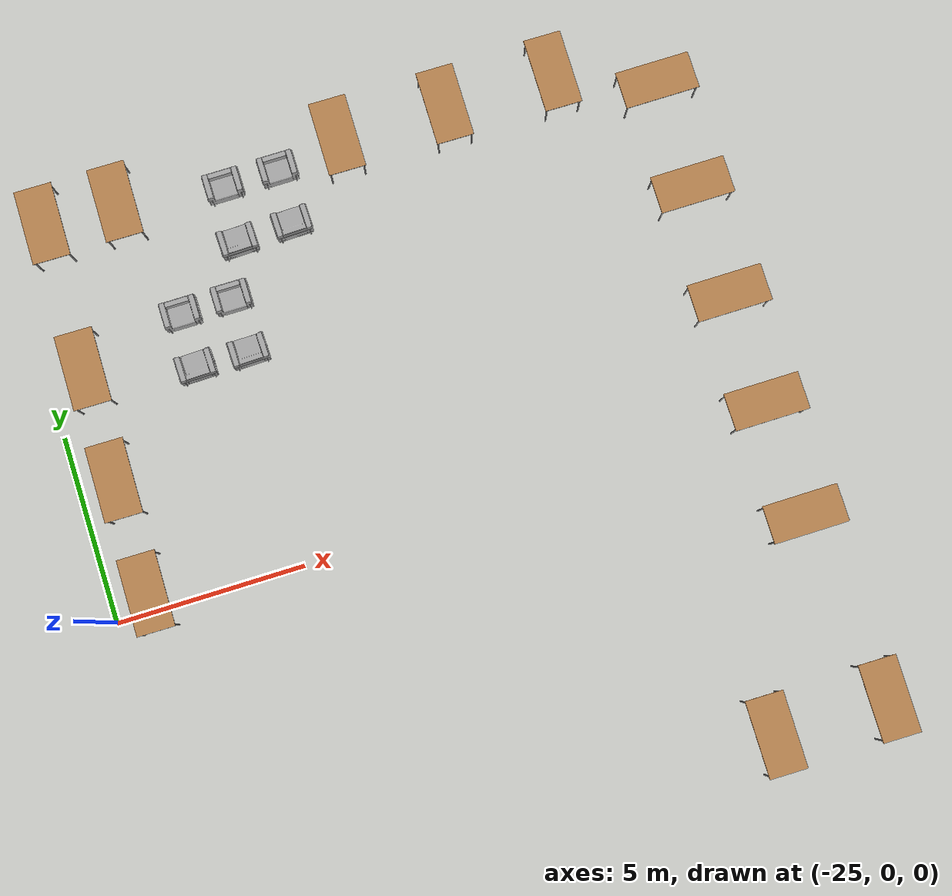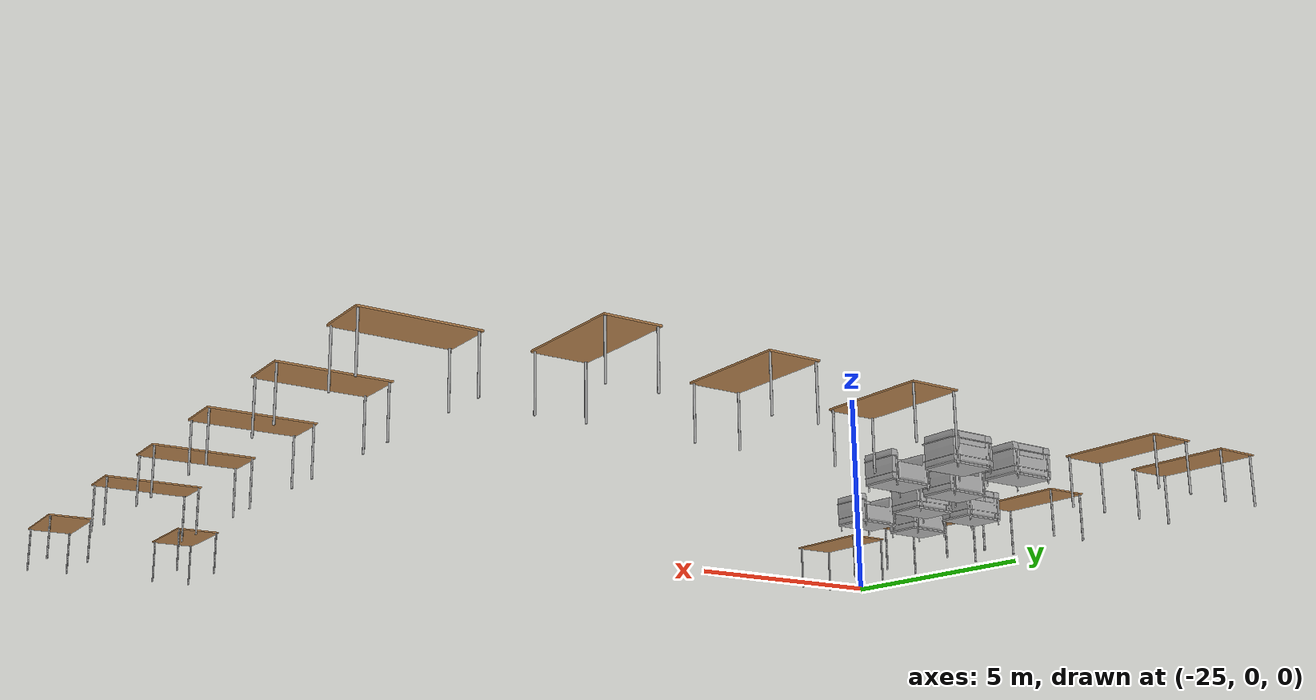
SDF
<?xml version='1.0'?>
<sdf version='1.6'>
  <model name='bibeg'>
    <link name='link_clone'>
      <self_collide>0</self_collide>
      <enable_wind>0</enable_wind>
      <kinematic>0</kinematic>
      <pose frame=''>-7.44763 -2.59534 0 0 -0 0</pose>
      <gravity>1</gravity>
      <inertial>
        <mass>1</mass>
        <pose frame=''>0 0 0 0 -0 0</pose>
        <inertia>
          <ixx>1</ixx>
          <ixy>0</ixy>
          <ixz>0</ixz>
          <iyy>1</iyy>
          <iyz>0</iyz>
          <izz>1</izz>
        </inertia>
      </inertial>
      <visual name='front_right_leg'>
        <pose frame=''>0.95 -0.45 0.5 0 -0 0</pose>
        <geometry>
          <cylinder>
            <radius>0.02</radius>
            <length>1</length>
          </cylinder>
        </geometry>
        <material>
          <script>
            <uri>file://media/materials/scripts/gazebo.material</uri>
            <name>Gazebo/Grey</name>
          </script>
          <shader type='vertex'>
            <normal_map>__default__</normal_map>
          </shader>
          <ambient>0.3 0.3 0.3 1</ambient>
          <diffuse>0.7 0.7 0.7 1</diffuse>
          <specular>0.01 0.01 0.01 1</specular>
          <emissive>0 0 0 1</emissive>
        </material>
        <transparency>0</transparency>
        <cast_shadows>1</cast_shadows>
      </visual>
      <visual name='visual1'>
        <pose frame=''>0 0 1 0 -0 0</pose>
        <geometry>
          <box>
            <size>2 1 0.03</size>
          </box>
        </geometry>
        <material>
          <script>
            <uri>file://media/materials/scripts/gazebo.material</uri>
            <name>Gazebo/Wood</name>
          </script>
          <shader type='vertex'>
            <normal_map>__default__</normal_map>
          </shader>
          <ambient>1 1 1 1</ambient>
          <diffuse>1 1 1 1</diffuse>
          <specular>0.2 0.2 0.2 1</specular>
          <emissive>0 0 0 1</emissive>
        </material>
        <transparency>0</transparency>
        <cast_shadows>1</cast_shadows>
      </visual>
      <visual name='back_right_leg'>
        <pose frame=''>-0.95 -0.45 0.5 0 -0 0</pose>
        <geometry>
          <cylinder>
            <radius>0.02</radius>
            <length>1</length>
          </cylinder>
        </geometry>
        <material>
          <script>
            <uri>file://media/materials/scripts/gazebo.material</uri>
            <name>Gazebo/Grey</name>
          </script>
          <shader type='vertex'>
            <normal_map>__default__</normal_map>
          </shader>
          <ambient>0.3 0.3 0.3 1</ambient>
          <diffuse>0.7 0.7 0.7 1</diffuse>
          <specular>0.01 0.01 0.01 1</specular>
          <emissive>0 0 0 1</emissive>
        </material>
        <transparency>0</transparency>
        <cast_shadows>1</cast_shadows>
      </visual>
      <visual name='back_left_leg'>
        <pose frame=''>-0.95 0.45 0.5 0 -0 0</pose>
        <geometry>
          <cylinder>
            <radius>0.02</radius>
            <length>1</length>
          </cylinder>
        </geometry>
        <material>
          <script>
            <uri>file://media/materials/scripts/gazebo.material</uri>
            <name>Gazebo/Grey</name>
          </script>
          <shader type='vertex'>
            <normal_map>__default__</normal_map>
          </shader>
          <ambient>0.3 0.3 0.3 1</ambient>
          <diffuse>0.7 0.7 0.7 1</diffuse>
          <specular>0.01 0.01 0.01 1</specular>
          <emissive>0 0 0 1</emissive>
        </material>
        <transparency>0</transparency>
        <cast_shadows>1</cast_shadows>
      </visual>
      <visual name='front_left_leg'>
        <pose frame=''>0.95 0.45 0.5 0 -0 0</pose>
        <geometry>
          <cylinder>
            <radius>0.02</radius>
            <length>1</length>
          </cylinder>
        </geometry>
        <material>
          <script>
            <uri>file://media/materials/scripts/gazebo.material</uri>
            <name>Gazebo/Grey</name>
          </script>
          <shader type='vertex'>
            <normal_map>__default__</normal_map>
          </shader>
          <ambient>0.3 0.3 0.3 1</ambient>
          <diffuse>0.7 0.7 0.7 1</diffuse>
          <specular>0.01 0.01 0.01 1</specular>
          <emissive>0 0 0 1</emissive>
        </material>
        <transparency>0</transparency>
        <cast_shadows>1</cast_shadows>
      </visual>
      <collision name='front_right_leg_0'>
        <laser_retro>0</laser_retro>
        <max_contacts>10</max_contacts>
        <pose frame=''>0.95 -0.45 0.5 0 -0 0</pose>
        <geometry>
          <cylinder>
            <radius>0.02</radius>
            <length>1</length>
          </cylinder>
        </geometry>
        <surface>
          <friction>
            <ode>
              <mu>1</mu>
              <mu2>1</mu2>
              <fdir1>0 0 0</fdir1>
              <slip1>0</slip1>
              <slip2>0</slip2>
            </ode>
            <torsional>
              <coefficient>1</coefficient>
              <patch_radius>0</patch_radius>
              <surface_radius>0</surface_radius>
              <use_patch_radius>1</use_patch_radius>
              <ode>
                <slip>0</slip>
              </ode>
            </torsional>
          </friction>
          <bounce>
            <restitution_coefficient>0</restitution_coefficient>
            <threshold>1e+06</threshold>
          </bounce>
          <contact>
            <collide_without_contact>0</collide_without_contact>
            <collide_without_contact_bitmask>1</collide_without_contact_bitmask>
            <collide_bitmask>1</collide_bitmask>
            <ode>
              <soft_cfm>0</soft_cfm>
              <soft_erp>0.2</soft_erp>
              <kp>1e+13</kp>
              <kd>1</kd>
              <max_vel>0.01</max_vel>
              <min_depth>0</min_depth>
            </ode>
            <bullet>
              <split_impulse>1</split_impulse>
              <split_impulse_penetration_threshold>-0.01</split_impulse_penetration_threshold>
              <soft_cfm>0</soft_cfm>
              <soft_erp>0.2</soft_erp>
              <kp>1e+13</kp>
              <kd>1</kd>
            </bullet>
          </contact>
        </surface>
      </collision>
      <collision name='back_left_leg_0'>
        <laser_retro>0</laser_retro>
        <max_contacts>10</max_contacts>
        <pose frame=''>-0.68 0.38 0.5 0 -0 0</pose>
        <geometry>
          <cylinder>
            <radius>0.02</radius>
            <length>1</length>
          </cylinder>
        </geometry>
        <surface>
          <friction>
            <ode>
              <mu>1</mu>
              <mu2>1</mu2>
              <fdir1>0 0 0</fdir1>
              <slip1>0</slip1>
              <slip2>0</slip2>
            </ode>
            <torsional>
              <coefficient>1</coefficient>
              <patch_radius>0</patch_radius>
              <surface_radius>0</surface_radius>
              <use_patch_radius>1</use_patch_radius>
              <ode>
                <slip>0</slip>
              </ode>
            </torsional>
          </friction>
          <bounce>
            <restitution_coefficient>0</restitution_coefficient>
            <threshold>1e+06</threshold>
          </bounce>
          <contact>
            <collide_without_contact>0</collide_without_contact>
            <collide_without_contact_bitmask>1</collide_without_contact_bitmask>
            <collide_bitmask>1</collide_bitmask>
            <ode>
              <soft_cfm>0</soft_cfm>
              <soft_erp>0.2</soft_erp>
              <kp>1e+13</kp>
              <kd>1</kd>
              <max_vel>0.01</max_vel>
              <min_depth>0</min_depth>
            </ode>
            <bullet>
              <split_impulse>1</split_impulse>
              <split_impulse_penetration_threshold>-0.01</split_impulse_penetration_threshold>
              <soft_cfm>0</soft_cfm>
              <soft_erp>0.2</soft_erp>
              <kp>1e+13</kp>
              <kd>1</kd>
            </bullet>
          </contact>
        </surface>
      </collision>
      <collision name='surface'>
        <laser_retro>0</laser_retro>
        <max_contacts>10</max_contacts>
        <pose frame=''>0 0 1 0 -0 0</pose>
        <geometry>
          <box>
            <size>2 1 0.03</size>
          </box>
        </geometry>
        <surface>
          <friction>
            <ode>
              <mu>1</mu>
              <mu2>1</mu2>
              <fdir1>0 0 0</fdir1>
              <slip1>0</slip1>
              <slip2>0</slip2>
            </ode>
            <torsional>
              <coefficient>1</coefficient>
              <patch_radius>0</patch_radius>
              <surface_radius>0</surface_radius>
              <use_patch_radius>1</use_patch_radius>
              <ode>
                <slip>0</slip>
              </ode>
            </torsional>
          </friction>
          <bounce>
            <restitution_coefficient>0</restitution_coefficient>
            <threshold>1e+06</threshold>
          </bounce>
          <contact>
            <collide_without_contact>0</collide_without_contact>
            <collide_without_contact_bitmask>1</collide_without_contact_bitmask>
            <collide_bitmask>1</collide_bitmask>
            <ode>
              <soft_cfm>0</soft_cfm>
              <soft_erp>0.2</soft_erp>
              <kp>1e+13</kp>
              <kd>1</kd>
              <max_vel>0.01</max_vel>
              <min_depth>0</min_depth>
            </ode>
            <bullet>
              <split_impulse>1</split_impulse>
              <split_impulse_penetration_threshold>-0.01</split_impulse_penetration_threshold>
              <soft_cfm>0</soft_cfm>
              <soft_erp>0.2</soft_erp>
              <kp>1e+13</kp>
              <kd>1</kd>
            </bullet>
          </contact>
        </surface>
      </collision>
      <collision name='front_left_leg_0'>
        <laser_retro>0</laser_retro>
        <max_contacts>10</max_contacts>
        <pose frame=''>0.95 0.45 0.5 0 -0 0</pose>
        <geometry>
          <cylinder>
            <radius>0.02</radius>
            <length>1</length>
          </cylinder>
        </geometry>
        <surface>
          <friction>
            <ode>
              <mu>1</mu>
              <mu2>1</mu2>
              <fdir1>0 0 0</fdir1>
              <slip1>0</slip1>
              <slip2>0</slip2>
            </ode>
            <torsional>
              <coefficient>1</coefficient>
              <patch_radius>0</patch_radius>
              <surface_radius>0</surface_radius>
              <use_patch_radius>1</use_patch_radius>
              <ode>
                <slip>0</slip>
              </ode>
            </torsional>
          </friction>
          <bounce>
            <restitution_coefficient>0</restitution_coefficient>
            <threshold>1e+06</threshold>
          </bounce>
          <contact>
            <collide_without_contact>0</collide_without_contact>
            <collide_without_contact_bitmask>1</collide_without_contact_bitmask>
            <collide_bitmask>1</collide_bitmask>
            <ode>
              <soft_cfm>0</soft_cfm>
              <soft_erp>0.2</soft_erp>
              <kp>1e+13</kp>
              <kd>1</kd>
              <max_vel>0.01</max_vel>
              <min_depth>0</min_depth>
            </ode>
            <bullet>
              <split_impulse>1</split_impulse>
              <split_impulse_penetration_threshold>-0.01</split_impulse_penetration_threshold>
              <soft_cfm>0</soft_cfm>
              <soft_erp>0.2</soft_erp>
              <kp>1e+13</kp>
              <kd>1</kd>
            </bullet>
          </contact>
        </surface>
      </collision>
      <collision name='back_right_leg_0'>
        <laser_retro>0</laser_retro>
        <max_contacts>10</max_contacts>
        <pose frame=''>-0.95 -0.45 0.5 0 -0 0</pose>
        <geometry>
          <cylinder>
            <radius>0.02</radius>
            <length>1</length>
          </cylinder>
        </geometry>
        <surface>
          <friction>
            <ode>
              <mu>1</mu>
              <mu2>1</mu2>
              <fdir1>0 0 0</fdir1>
              <slip1>0</slip1>
              <slip2>0</slip2>
            </ode>
            <torsional>
              <coefficient>1</coefficient>
              <patch_radius>0</patch_radius>
              <surface_radius>0</surface_radius>
              <use_patch_radius>1</use_patch_radius>
              <ode>
                <slip>0</slip>
              </ode>
            </torsional>
          </friction>
          <bounce>
            <restitution_coefficient>0</restitution_coefficient>
            <threshold>1e+06</threshold>
          </bounce>
          <contact>
            <collide_without_contact>0</collide_without_contact>
            <collide_without_contact_bitmask>1</collide_without_contact_bitmask>
            <collide_bitmask>1</collide_bitmask>
            <ode>
              <soft_cfm>0</soft_cfm>
              <soft_erp>0.2</soft_erp>
              <kp>1e+13</kp>
              <kd>1</kd>
              <max_vel>0.01</max_vel>
              <min_depth>0</min_depth>
            </ode>
            <bullet>
              <split_impulse>1</split_impulse>
              <split_impulse_penetration_threshold>-0.01</split_impulse_penetration_threshold>
              <soft_cfm>0</soft_cfm>
              <soft_erp>0.2</soft_erp>
              <kp>1e+13</kp>
              <kd>1</kd>
            </bullet>
          </contact>
        </surface>
      </collision>
    </link>
    <link name='link_clone_0'>
      <self_collide>0</self_collide>
      <enable_wind>0</enable_wind>
      <kinematic>0</kinematic>
      <pose frame=''>-7.46291 0.419791 0 0 -0 0</pose>
      <gravity>1</gravity>
      <inertial>
        <mass>1</mass>
        <pose frame=''>0 0 0 0 -0 0</pose>
        <inertia>
          <ixx>1</ixx>
          <ixy>0</ixy>
          <ixz>0</ixz>
          <iyy>1</iyy>
          <iyz>0</iyz>
          <izz>1</izz>
        </inertia>
      </inertial>
      <visual name='visual1'>
        <pose frame=''>0 0 1 0 -0 0</pose>
        <geometry>
          <box>
            <size>2 1 0.03</size>
          </box>
        </geometry>
        <material>
          <script>
            <uri>file://media/materials/scripts/gazebo.material</uri>
            <name>Gazebo/Wood</name>
          </script>
          <shader type='vertex'>
            <normal_map>__default__</normal_map>
          </shader>
          <ambient>1 1 1 1</ambient>
          <diffuse>1 1 1 1</diffuse>
          <specular>0.2 0.2 0.2 1</specular>
          <emissive>0 0 0 1</emissive>
        </material>
        <transparency>0</transparency>
        <cast_shadows>1</cast_shadows>
      </visual>
      <visual name='front_left_leg'>
        <pose frame=''>0.95 0.45 0.5 0 -0 0</pose>
        <geometry>
          <cylinder>
            <radius>0.02</radius>
            <length>1</length>
          </cylinder>
        </geometry>
        <material>
          <script>
            <uri>file://media/materials/scripts/gazebo.material</uri>
            <name>Gazebo/Grey</name>
          </script>
          <shader type='vertex'>
            <normal_map>__default__</normal_map>
          </shader>
          <ambient>0.3 0.3 0.3 1</ambient>
          <diffuse>0.7 0.7 0.7 1</diffuse>
          <specular>0.01 0.01 0.01 1</specular>
          <emissive>0 0 0 1</emissive>
        </material>
        <transparency>0</transparency>
        <cast_shadows>1</cast_shadows>
      </visual>
      <visual name='front_right_leg'>
        <pose frame=''>0.95 -0.45 0.5 0 -0 0</pose>
        <geometry>
          <cylinder>
            <radius>0.02</radius>
            <length>1</length>
          </cylinder>
        </geometry>
        <material>
          <script>
            <uri>file://media/materials/scripts/gazebo.material</uri>
            <name>Gazebo/Grey</name>
          </script>
          <shader type='vertex'>
            <normal_map>__default__</normal_map>
          </shader>
          <ambient>0.3 0.3 0.3 1</ambient>
          <diffuse>0.7 0.7 0.7 1</diffuse>
          <specular>0.01 0.01 0.01 1</specular>
          <emissive>0 0 0 1</emissive>
        </material>
        <transparency>0</transparency>
        <cast_shadows>1</cast_shadows>
      </visual>
      <visual name='back_right_leg'>
        <pose frame=''>-0.95 -0.45 0.5 0 -0 0</pose>
        <geometry>
          <cylinder>
            <radius>0.02</radius>
            <length>1</length>
          </cylinder>
        </geometry>
        <material>
          <script>
            <uri>file://media/materials/scripts/gazebo.material</uri>
            <name>Gazebo/Grey</name>
          </script>
          <shader type='vertex'>
            <normal_map>__default__</normal_map>
          </shader>
          <ambient>0.3 0.3 0.3 1</ambient>
          <diffuse>0.7 0.7 0.7 1</diffuse>
          <specular>0.01 0.01 0.01 1</specular>
          <emissive>0 0 0 1</emissive>
        </material>
        <transparency>0</transparency>
        <cast_shadows>1</cast_shadows>
      </visual>
      <visual name='back_left_leg'>
        <pose frame=''>-0.95 0.45 0.5 0 -0 0</pose>
        <geometry>
          <cylinder>
            <radius>0.02</radius>
            <length>1</length>
          </cylinder>
        </geometry>
        <material>
          <script>
            <uri>file://media/materials/scripts/gazebo.material</uri>
            <name>Gazebo/Grey</name>
          </script>
          <shader type='vertex'>
            <normal_map>__default__</normal_map>
          </shader>
          <ambient>0.3 0.3 0.3 1</ambient>
          <diffuse>0.7 0.7 0.7 1</diffuse>
          <specular>0.01 0.01 0.01 1</specular>
          <emissive>0 0 0 1</emissive>
        </material>
        <transparency>0</transparency>
        <cast_shadows>1</cast_shadows>
      </visual>
      <collision name='surface'>
        <laser_retro>0</laser_retro>
        <max_contacts>10</max_contacts>
        <pose frame=''>0 0 1 0 -0 0</pose>
        <geometry>
          <box>
            <size>2 1 0.03</size>
          </box>
        </geometry>
        <surface>
          <friction>
            <ode>
              <mu>1</mu>
              <mu2>1</mu2>
              <fdir1>0 0 0</fdir1>
              <slip1>0</slip1>
              <slip2>0</slip2>
            </ode>
            <torsional>
              <coefficient>1</coefficient>
              <patch_radius>0</patch_radius>
              <surface_radius>0</surface_radius>
              <use_patch_radius>1</use_patch_radius>
              <ode>
                <slip>0</slip>
              </ode>
            </torsional>
          </friction>
          <bounce>
            <restitution_coefficient>0</restitution_coefficient>
            <threshold>1e+06</threshold>
          </bounce>
          <contact>
            <collide_without_contact>0</collide_without_contact>
            <collide_without_contact_bitmask>1</collide_without_contact_bitmask>
            <collide_bitmask>1</collide_bitmask>
            <ode>
              <soft_cfm>0</soft_cfm>
              <soft_erp>0.2</soft_erp>
              <kp>1e+13</kp>
              <kd>1</kd>
              <max_vel>0.01</max_vel>
              <min_depth>0</min_depth>
            </ode>
            <bullet>
              <split_impulse>1</split_impulse>
              <split_impulse_penetration_threshold>-0.01</split_impulse_penetration_threshold>
              <soft_cfm>0</soft_cfm>
              <soft_erp>0.2</soft_erp>
              <kp>1e+13</kp>
              <kd>1</kd>
            </bullet>
          </contact>
        </surface>
      </collision>
      <collision name='front_left_leg_0'>
        <laser_retro>0</laser_retro>
        <max_contacts>10</max_contacts>
        <pose frame=''>0.95 0.45 0.5 0 -0 0</pose>
        <geometry>
          <cylinder>
            <radius>0.02</radius>
            <length>1</length>
          </cylinder>
        </geometry>
        <surface>
          <friction>
            <ode>
              <mu>1</mu>
              <mu2>1</mu2>
              <fdir1>0 0 0</fdir1>
              <slip1>0</slip1>
              <slip2>0</slip2>
            </ode>
            <torsional>
              <coefficient>1</coefficient>
              <patch_radius>0</patch_radius>
              <surface_radius>0</surface_radius>
              <use_patch_radius>1</use_patch_radius>
              <ode>
                <slip>0</slip>
              </ode>
            </torsional>
          </friction>
          <bounce>
            <restitution_coefficient>0</restitution_coefficient>
            <threshold>1e+06</threshold>
          </bounce>
          <contact>
            <collide_without_contact>0</collide_without_contact>
            <collide_without_contact_bitmask>1</collide_without_contact_bitmask>
            <collide_bitmask>1</collide_bitmask>
            <ode>
              <soft_cfm>0</soft_cfm>
              <soft_erp>0.2</soft_erp>
              <kp>1e+13</kp>
              <kd>1</kd>
              <max_vel>0.01</max_vel>
              <min_depth>0</min_depth>
            </ode>
            <bullet>
              <split_impulse>1</split_impulse>
              <split_impulse_penetration_threshold>-0.01</split_impulse_penetration_threshold>
              <soft_cfm>0</soft_cfm>
              <soft_erp>0.2</soft_erp>
              <kp>1e+13</kp>
              <kd>1</kd>
            </bullet>
          </contact>
        </surface>
      </collision>
      <collision name='front_right_leg_0'>
        <laser_retro>0</laser_retro>
        <max_contacts>10</max_contacts>
        <pose frame=''>0.95 -0.45 0.5 0 -0 0</pose>
        <geometry>
          <cylinder>
            <radius>0.02</radius>
            <length>1</length>
          </cylinder>
        </geometry>
        <surface>
          <friction>
            <ode>
              <mu>1</mu>
              <mu2>1</mu2>
              <fdir1>0 0 0</fdir1>
              <slip1>0</slip1>
              <slip2>0</slip2>
            </ode>
            <torsional>
              <coefficient>1</coefficient>
              <patch_radius>0</patch_radius>
              <surface_radius>0</surface_radius>
              <use_patch_radius>1</use_patch_radius>
              <ode>
                <slip>0</slip>
              </ode>
            </torsional>
          </friction>
          <bounce>
            <restitution_coefficient>0</restitution_coefficient>
            <threshold>1e+06</threshold>
          </bounce>
          <contact>
            <collide_without_contact>0</collide_without_contact>
            <collide_without_contact_bitmask>1</collide_without_contact_bitmask>
            <collide_bitmask>1</collide_bitmask>
            <ode>
              <soft_cfm>0</soft_cfm>
              <soft_erp>0.2</soft_erp>
              <kp>1e+13</kp>
              <kd>1</kd>
              <max_vel>0.01</max_vel>
              <min_depth>0</min_depth>
            </ode>
            <bullet>
              <split_impulse>1</split_impulse>
              <split_impulse_penetration_threshold>-0.01</split_impulse_penetration_threshold>
              <soft_cfm>0</soft_cfm>
              <soft_erp>0.2</soft_erp>
              <kp>1e+13</kp>
              <kd>1</kd>
            </bullet>
          </contact>
        </surface>
      </collision>
      <collision name='back_right_leg_0'>
        <laser_retro>0</laser_retro>
        <max_contacts>10</max_contacts>
        <pose frame=''>-0.95 -0.45 0.5 0 -0 0</pose>
        <geometry>
          <cylinder>
            <radius>0.02</radius>
            <length>1</length>
          </cylinder>
        </geometry>
        <surface>
          <friction>
            <ode>
              <mu>1</mu>
              <mu2>1</mu2>
              <fdir1>0 0 0</fdir1>
              <slip1>0</slip1>
              <slip2>0</slip2>
            </ode>
            <torsional>
              <coefficient>1</coefficient>
              <patch_radius>0</patch_radius>
              <surface_radius>0</surface_radius>
              <use_patch_radius>1</use_patch_radius>
              <ode>
                <slip>0</slip>
              </ode>
            </torsional>
          </friction>
          <bounce>
            <restitution_coefficient>0</restitution_coefficient>
            <threshold>1e+06</threshold>
          </bounce>
          <contact>
            <collide_without_contact>0</collide_without_contact>
            <collide_without_contact_bitmask>1</collide_without_contact_bitmask>
            <collide_bitmask>1</collide_bitmask>
            <ode>
              <soft_cfm>0</soft_cfm>
              <soft_erp>0.2</soft_erp>
              <kp>1e+13</kp>
              <kd>1</kd>
              <max_vel>0.01</max_vel>
              <min_depth>0</min_depth>
            </ode>
            <bullet>
              <split_impulse>1</split_impulse>
              <split_impulse_penetration_threshold>-0.01</split_impulse_penetration_threshold>
              <soft_cfm>0</soft_cfm>
              <soft_erp>0.2</soft_erp>
              <kp>1e+13</kp>
              <kd>1</kd>
            </bullet>
          </contact>
        </surface>
      </collision>
      <collision name='back_left_leg_0'>
        <laser_retro>0</laser_retro>
        <max_contacts>10</max_contacts>
        <pose frame=''>-0.68 0.38 0.5 0 -0 0</pose>
        <geometry>
          <cylinder>
            <radius>0.02</radius>
            <length>1</length>
          </cylinder>
        </geometry>
        <surface>
          <friction>
            <ode>
              <mu>1</mu>
              <mu2>1</mu2>
              <fdir1>0 0 0</fdir1>
              <slip1>0</slip1>
              <slip2>0</slip2>
            </ode>
            <torsional>
              <coefficient>1</coefficient>
              <patch_radius>0</patch_radius>
              <surface_radius>0</surface_radius>
              <use_patch_radius>1</use_patch_radius>
              <ode>
                <slip>0</slip>
              </ode>
            </torsional>
          </friction>
          <bounce>
            <restitution_coefficient>0</restitution_coefficient>
            <threshold>1e+06</threshold>
          </bounce>
          <contact>
            <collide_without_contact>0</collide_without_contact>
            <collide_without_contact_bitmask>1</collide_without_contact_bitmask>
            <collide_bitmask>1</collide_bitmask>
            <ode>
              <soft_cfm>0</soft_cfm>
              <soft_erp>0.2</soft_erp>
              <kp>1e+13</kp>
              <kd>1</kd>
              <max_vel>0.01</max_vel>
              <min_depth>0</min_depth>
            </ode>
            <bullet>
              <split_impulse>1</split_impulse>
              <split_impulse_penetration_threshold>-0.01</split_impulse_penetration_threshold>
              <soft_cfm>0</soft_cfm>
              <soft_erp>0.2</soft_erp>
              <kp>1e+13</kp>
              <kd>1</kd>
            </bullet>
          </contact>
        </surface>
      </collision>
    </link>
    <link name='link_clone_1'>
      <self_collide>0</self_collide>
      <enable_wind>0</enable_wind>
      <kinematic>0</kinematic>
      <pose frame=''>-7.46615 3.3827 0 0 -0 0</pose>
      <gravity>1</gravity>
      <inertial>
        <mass>1</mass>
        <pose frame=''>0 0 0 0 -0 0</pose>
        <inertia>
          <ixx>1</ixx>
          <ixy>0</ixy>
          <ixz>0</ixz>
          <iyy>1</iyy>
          <iyz>0</iyz>
          <izz>1</izz>
        </inertia>
      </inertial>
      <visual name='visual1'>
        <pose frame=''>0 0 1 0 -0 0</pose>
        <geometry>
          <box>
            <size>2 1 0.03</size>
          </box>
        </geometry>
        <material>
          <script>
            <uri>file://media/materials/scripts/gazebo.material</uri>
            <name>Gazebo/Wood</name>
          </script>
          <shader type='vertex'>
            <normal_map>__default__</normal_map>
          </shader>
          <ambient>1 1 1 1</ambient>
          <diffuse>1 1 1 1</diffuse>
          <specular>0.2 0.2 0.2 1</specular>
          <emissive>0 0 0 1</emissive>
        </material>
        <transparency>0</transparency>
        <cast_shadows>1</cast_shadows>
      </visual>
      <visual name='front_left_leg'>
        <pose frame=''>0.95 0.45 0.5 0 -0 0</pose>
        <geometry>
          <cylinder>
            <radius>0.02</radius>
            <length>1</length>
          </cylinder>
        </geometry>
        <material>
          <script>
            <uri>file://media/materials/scripts/gazebo.material</uri>
            <name>Gazebo/Grey</name>
          </script>
          <shader type='vertex'>
            <normal_map>__default__</normal_map>
          </shader>
          <ambient>0.3 0.3 0.3 1</ambient>
          <diffuse>0.7 0.7 0.7 1</diffuse>
          <specular>0.01 0.01 0.01 1</specular>
          <emissive>0 0 0 1</emissive>
        </material>
        <transparency>0</transparency>
        <cast_shadows>1</cast_shadows>
      </visual>
      <visual name='front_right_leg'>
        <pose frame=''>0.95 -0.45 0.5 0 -0 0</pose>
        <geometry>
          <cylinder>
            <radius>0.02</radius>
            <length>1</length>
          </cylinder>
        </geometry>
        <material>
          <script>
            <uri>file://media/materials/scripts/gazebo.material</uri>
            <name>Gazebo/Grey</name>
          </script>
          <shader type='vertex'>
            <normal_map>__default__</normal_map>
          </shader>
          <ambient>0.3 0.3 0.3 1</ambient>
          <diffuse>0.7 0.7 0.7 1</diffuse>
          <specular>0.01 0.01 0.01 1</specular>
          <emissive>0 0 0 1</emissive>
        </material>
        <transparency>0</transparency>
        <cast_shadows>1</cast_shadows>
      </visual>
      <visual name='back_right_leg'>
        <pose frame=''>-0.95 -0.45 0.5 0 -0 0</pose>
        <geometry>
          <cylinder>
            <radius>0.02</radius>
            <length>1</length>
          </cylinder>
        </geometry>
        <material>
          <script>
            <uri>file://media/materials/scripts/gazebo.material</uri>
            <name>Gazebo/Grey</name>
          </script>
          <shader type='vertex'>
            <normal_map>__default__</normal_map>
          </shader>
          <ambient>0.3 0.3 0.3 1</ambient>
          <diffuse>0.7 0.7 0.7 1</diffuse>
          <specular>0.01 0.01 0.01 1</specular>
          <emissive>0 0 0 1</emissive>
        </material>
        <transparency>0</transparency>
        <cast_shadows>1</cast_shadows>
      </visual>
      <visual name='back_left_leg'>
        <pose frame=''>-0.95 0.45 0.5 0 -0 0</pose>
        <geometry>
          <cylinder>
            <radius>0.02</radius>
            <length>1</length>
          </cylinder>
        </geometry>
        <material>
          <script>
            <uri>file://media/materials/scripts/gazebo.material</uri>
            <name>Gazebo/Grey</name>
          </script>
          <shader type='vertex'>
            <normal_map>__default__</normal_map>
          </shader>
          <ambient>0.3 0.3 0.3 1</ambient>
          <diffuse>0.7 0.7 0.7 1</diffuse>
          <specular>0.01 0.01 0.01 1</specular>
          <emissive>0 0 0 1</emissive>
        </material>
        <transparency>0</transparency>
        <cast_shadows>1</cast_shadows>
      </visual>
      <collision name='surface'>
        <laser_retro>0</laser_retro>
        <max_contacts>10</max_contacts>
        <pose frame=''>0 0 1 0 -0 0</pose>
        <geometry>
          <box>
            <size>2 1 0.03</size>
          </box>
        </geometry>
        <surface>
          <friction>
            <ode>
              <mu>1</mu>
              <mu2>1</mu2>
              <fdir1>0 0 0</fdir1>
              <slip1>0</slip1>
              <slip2>0</slip2>
            </ode>
            <torsional>
              <coefficient>1</coefficient>
              <patch_radius>0</patch_radius>
              <surface_radius>0</surface_radius>
              <use_patch_radius>1</use_patch_radius>
              <ode>
                <slip>0</slip>
              </ode>
            </torsional>
          </friction>
          <bounce>
            <restitution_coefficient>0</restitution_coefficient>
            <threshold>1e+06</threshold>
          </bounce>
          <contact>
            <collide_without_contact>0</collide_without_contact>
            <collide_without_contact_bitmask>1</collide_without_contact_bitmask>
            <collide_bitmask>1</collide_bitmask>
            <ode>
              <soft_cfm>0</soft_cfm>
              <soft_erp>0.2</soft_erp>
              <kp>1e+13</kp>
              <kd>1</kd>
              <max_vel>0.01</max_vel>
              <min_depth>0</min_depth>
            </ode>
            <bullet>
              <split_impulse>1</split_impulse>
              <split_impulse_penetration_threshold>-0.01</split_impulse_penetration_threshold>
              <soft_cfm>0</soft_cfm>
              <soft_erp>0.2</soft_erp>
              <kp>1e+13</kp>
              <kd>1</kd>
            </bullet>
          </contact>
        </surface>
      </collision>
      <collision name='front_left_leg_0'>
        <laser_retro>0</laser_retro>
        <max_contacts>10</max_contacts>
        <pose frame=''>0.95 0.45 0.5 0 -0 0</pose>
        <geometry>
          <cylinder>
            <radius>0.02</radius>
            <length>1</length>
          </cylinder>
        </geometry>
        <surface>
          <friction>
            <ode>
              <mu>1</mu>
              <mu2>1</mu2>
              <fdir1>0 0 0</fdir1>
              <slip1>0</slip1>
              <slip2>0</slip2>
            </ode>
            <torsional>
              <coefficient>1</coefficient>
              <patch_radius>0</patch_radius>
              <surface_radius>0</surface_radius>
              <use_patch_radius>1</use_patch_radius>
              <ode>
                <slip>0</slip>
              </ode>
            </torsional>
          </friction>
          <bounce>
            <restitution_coefficient>0</restitution_coefficient>
            <threshold>1e+06</threshold>
          </bounce>
          <contact>
            <collide_without_contact>0</collide_without_contact>
            <collide_without_contact_bitmask>1</collide_without_contact_bitmask>
            <collide_bitmask>1</collide_bitmask>
            <ode>
              <soft_cfm>0</soft_cfm>
              <soft_erp>0.2</soft_erp>
              <kp>1e+13</kp>
              <kd>1</kd>
              <max_vel>0.01</max_vel>
              <min_depth>0</min_depth>
            </ode>
            <bullet>
              <split_impulse>1</split_impulse>
              <split_impulse_penetration_threshold>-0.01</split_impulse_penetration_threshold>
              <soft_cfm>0</soft_cfm>
              <soft_erp>0.2</soft_erp>
              <kp>1e+13</kp>
              <kd>1</kd>
            </bullet>
          </contact>
        </surface>
      </collision>
      <collision name='front_right_leg_0'>
        <laser_retro>0</laser_retro>
        <max_contacts>10</max_contacts>
        <pose frame=''>0.95 -0.45 0.5 0 -0 0</pose>
        <geometry>
          <cylinder>
            <radius>0.02</radius>
            <length>1</length>
          </cylinder>
        </geometry>
        <surface>
          <friction>
            <ode>
              <mu>1</mu>
              <mu2>1</mu2>
              <fdir1>0 0 0</fdir1>
              <slip1>0</slip1>
              <slip2>0</slip2>
            </ode>
            <torsional>
              <coefficient>1</coefficient>
              <patch_radius>0</patch_radius>
              <surface_radius>0</surface_radius>
              <use_patch_radius>1</use_patch_radius>
              <ode>
                <slip>0</slip>
              </ode>
            </torsional>
          </friction>
          <bounce>
            <restitution_coefficient>0</restitution_coefficient>
            <threshold>1e+06</threshold>
          </bounce>
          <contact>
            <collide_without_contact>0</collide_without_contact>
            <collide_without_contact_bitmask>1</collide_without_contact_bitmask>
            <collide_bitmask>1</collide_bitmask>
            <ode>
              <soft_cfm>0</soft_cfm>
              <soft_erp>0.2</soft_erp>
              <kp>1e+13</kp>
              <kd>1</kd>
              <max_vel>0.01</max_vel>
              <min_depth>0</min_depth>
            </ode>
            <bullet>
              <split_impulse>1</split_impulse>
              <split_impulse_penetration_threshold>-0.01</split_impulse_penetration_threshold>
              <soft_cfm>0</soft_cfm>
              <soft_erp>0.2</soft_erp>
              <kp>1e+13</kp>
              <kd>1</kd>
            </bullet>
          </contact>
        </surface>
      </collision>
      <collision name='back_right_leg_0'>
        <laser_retro>0</laser_retro>
        <max_contacts>10</max_contacts>
        <pose frame=''>-0.95 -0.45 0.5 0 -0 0</pose>
        <geometry>
          <cylinder>
            <radius>0.02</radius>
            <length>1</length>
          </cylinder>
        </geometry>
        <surface>
          <friction>
            <ode>
              <mu>1</mu>
              <mu2>1</mu2>
              <fdir1>0 0 0</fdir1>
              <slip1>0</slip1>
              <slip2>0</slip2>
            </ode>
            <torsional>
              <coefficient>1</coefficient>
              <patch_radius>0</patch_radius>
              <surface_radius>0</surface_radius>
              <use_patch_radius>1</use_patch_radius>
              <ode>
                <slip>0</slip>
              </ode>
            </torsional>
          </friction>
          <bounce>
            <restitution_coefficient>0</restitution_coefficient>
            <threshold>1e+06</threshold>
          </bounce>
          <contact>
            <collide_without_contact>0</collide_without_contact>
            <collide_without_contact_bitmask>1</collide_without_contact_bitmask>
            <collide_bitmask>1</collide_bitmask>
            <ode>
              <soft_cfm>0</soft_cfm>
              <soft_erp>0.2</soft_erp>
              <kp>1e+13</kp>
              <kd>1</kd>
              <max_vel>0.01</max_vel>
              <min_depth>0</min_depth>
            </ode>
            <bullet>
              <split_impulse>1</split_impulse>
              <split_impulse_penetration_threshold>-0.01</split_impulse_penetration_threshold>
              <soft_cfm>0</soft_cfm>
              <soft_erp>0.2</soft_erp>
              <kp>1e+13</kp>
              <kd>1</kd>
            </bullet>
          </contact>
        </surface>
      </collision>
      <collision name='back_left_leg_0'>
        <laser_retro>0</laser_retro>
        <max_contacts>10</max_contacts>
        <pose frame=''>-0.68 0.38 0.5 0 -0 0</pose>
        <geometry>
          <cylinder>
            <radius>0.02</radius>
            <length>1</length>
          </cylinder>
        </geometry>
        <surface>
          <friction>
            <ode>
              <mu>1</mu>
              <mu2>1</mu2>
              <fdir1>0 0 0</fdir1>
              <slip1>0</slip1>
              <slip2>0</slip2>
            </ode>
            <torsional>
              <coefficient>1</coefficient>
              <patch_radius>0</patch_radius>
              <surface_radius>0</surface_radius>
              <use_patch_radius>1</use_patch_radius>
              <ode>
                <slip>0</slip>
              </ode>
            </torsional>
          </friction>
          <bounce>
            <restitution_coefficient>0</restitution_coefficient>
            <threshold>1e+06</threshold>
          </bounce>
          <contact>
            <collide_without_contact>0</collide_without_contact>
            <collide_without_contact_bitmask>1</collide_without_contact_bitmask>
            <collide_bitmask>1</collide_bitmask>
            <ode>
              <soft_cfm>0</soft_cfm>
              <soft_erp>0.2</soft_erp>
              <kp>1e+13</kp>
              <kd>1</kd>
              <max_vel>0.01</max_vel>
              <min_depth>0</min_depth>
            </ode>
            <bullet>
              <split_impulse>1</split_impulse>
              <split_impulse_penetration_threshold>-0.01</split_impulse_penetration_threshold>
              <soft_cfm>0</soft_cfm>
              <soft_erp>0.2</soft_erp>
              <kp>1e+13</kp>
              <kd>1</kd>
            </bullet>
          </contact>
        </surface>
      </collision>
    </link>
    <link name='link_clone_10'>
      <self_collide>0</self_collide>
      <enable_wind>0</enable_wind>
      <kinematic>0</kinematic>
      <pose frame=''>-23.931 3.4401 0 0 -0 1.56126</pose>
      <gravity>1</gravity>
      <inertial>
        <mass>1</mass>
        <pose frame=''>0 0 0 0 -0 0</pose>
        <inertia>
          <ixx>1</ixx>
          <ixy>0</ixy>
          <ixz>0</ixz>
          <iyy>1</iyy>
          <iyz>0</iyz>
          <izz>1</izz>
        </inertia>
      </inertial>
      <visual name='visual1'>
        <pose frame=''>0 0 1 0 -0 0</pose>
        <geometry>
          <box>
            <size>2 1 0.03</size>
          </box>
        </geometry>
        <material>
          <script>
            <uri>file://media/materials/scripts/gazebo.material</uri>
            <name>Gazebo/Wood</name>
          </script>
          <shader type='vertex'>
            <normal_map>__default__</normal_map>
          </shader>
          <ambient>1 1 1 1</ambient>
          <diffuse>1 1 1 1</diffuse>
          <specular>0.2 0.2 0.2 1</specular>
          <emissive>0 0 0 1</emissive>
        </material>
        <transparency>0</transparency>
        <cast_shadows>1</cast_shadows>
      </visual>
      <visual name='front_left_leg'>
        <pose frame=''>0.95 0.45 0.5 0 -0 0</pose>
        <geometry>
          <cylinder>
            <radius>0.02</radius>
            <length>1</length>
          </cylinder>
        </geometry>
        <material>
          <script>
            <uri>file://media/materials/scripts/gazebo.material</uri>
            <name>Gazebo/Grey</name>
          </script>
          <shader type='vertex'>
            <normal_map>__default__</normal_map>
          </shader>
          <ambient>0.3 0.3 0.3 1</ambient>
          <diffuse>0.7 0.7 0.7 1</diffuse>
          <specular>0.01 0.01 0.01 1</specular>
          <emissive>0 0 0 1</emissive>
        </material>
        <transparency>0</transparency>
        <cast_shadows>1</cast_shadows>
      </visual>
      <visual name='front_right_leg'>
        <pose frame=''>0.95 -0.45 0.5 0 -0 0</pose>
        <geometry>
          <cylinder>
            <radius>0.02</radius>
            <length>1</length>
          </cylinder>
        </geometry>
        <material>
          <script>
            <uri>file://media/materials/scripts/gazebo.material</uri>
            <name>Gazebo/Grey</name>
          </script>
          <shader type='vertex'>
            <normal_map>__default__</normal_map>
          </shader>
          <ambient>0.3 0.3 0.3 1</ambient>
          <diffuse>0.7 0.7 0.7 1</diffuse>
          <specular>0.01 0.01 0.01 1</specular>
          <emissive>0 0 0 1</emissive>
        </material>
        <transparency>0</transparency>
        <cast_shadows>1</cast_shadows>
      </visual>
      <visual name='back_right_leg'>
        <pose frame=''>-0.95 -0.45 0.5 0 -0 0</pose>
        <geometry>
          <cylinder>
            <radius>0.02</radius>
            <length>1</length>
          </cylinder>
        </geometry>
        <material>
          <script>
            <uri>file://media/materials/scripts/gazebo.material</uri>
            <name>Gazebo/Grey</name>
          </script>
          <shader type='vertex'>
            <normal_map>__default__</normal_map>
          </shader>
          <ambient>0.3 0.3 0.3 1</ambient>
          <diffuse>0.7 0.7 0.7 1</diffuse>
          <specular>0.01 0.01 0.01 1</specular>
          <emissive>0 0 0 1</emissive>
        </material>
        <transparency>0</transparency>
        <cast_shadows>1</cast_shadows>
      </visual>
      <visual name='back_left_leg'>
        <pose frame=''>-0.95 0.45 0.5 0 -0 0</pose>
        <geometry>
          <cylinder>
            <radius>0.02</radius>
            <length>1</length>
          </cylinder>
        </geometry>
        <material>
          <script>
            <uri>file://media/materials/scripts/gazebo.material</uri>
            <name>Gazebo/Grey</name>
          </script>
          <shader type='vertex'>
            <normal_map>__default__</normal_map>
          </shader>
          <ambient>0.3 0.3 0.3 1</ambient>
          <diffuse>0.7 0.7 0.7 1</diffuse>
          <specular>0.01 0.01 0.01 1</specular>
          <emissive>0 0 0 1</emissive>
        </material>
        <transparency>0</transparency>
        <cast_shadows>1</cast_shadows>
      </visual>
      <collision name='surface'>
        <laser_retro>0</laser_retro>
        <max_contacts>10</max_contacts>
        <pose frame=''>0 0 1 0 -0 0</pose>
        <geometry>
          <box>
            <size>2 1 0.03</size>
          </box>
        </geometry>
        <surface>
          <friction>
            <ode>
              <mu>1</mu>
              <mu2>1</mu2>
              <fdir1>0 0 0</fdir1>
              <slip1>0</slip1>
              <slip2>0</slip2>
            </ode>
            <torsional>
              <coefficient>1</coefficient>
              <patch_radius>0</patch_radius>
              <surface_radius>0</surface_radius>
              <use_patch_radius>1</use_patch_radius>
              <ode>
                <slip>0</slip>
              </ode>
            </torsional>
          </friction>
          <bounce>
            <restitution_coefficient>0</restitution_coefficient>
            <threshold>1e+06</threshold>
          </bounce>
          <contact>
            <collide_without_contact>0</collide_without_contact>
            <collide_without_contact_bitmask>1</collide_without_contact_bitmask>
            <collide_bitmask>1</collide_bitmask>
            <ode>
              <soft_cfm>0</soft_cfm>
              <soft_erp>0.2</soft_erp>
              <kp>1e+13</kp>
              <kd>1</kd>
              <max_vel>0.01</max_vel>
              <min_depth>0</min_depth>
            </ode>
            <bullet>
              <split_impulse>1</split_impulse>
              <split_impulse_penetration_threshold>-0.01</split_impulse_penetration_threshold>
              <soft_cfm>0</soft_cfm>
              <soft_erp>0.2</soft_erp>
              <kp>1e+13</kp>
              <kd>1</kd>
            </bullet>
          </contact>
        </surface>
      </collision>
      <collision name='front_left_leg_0'>
        <laser_retro>0</laser_retro>
        <max_contacts>10</max_contacts>
        <pose frame=''>0.95 0.45 0.5 0 -0 0</pose>
        <geometry>
          <cylinder>
            <radius>0.02</radius>
            <length>1</length>
          </cylinder>
        </geometry>
        <surface>
          <friction>
            <ode>
              <mu>1</mu>
              <mu2>1</mu2>
              <fdir1>0 0 0</fdir1>
              <slip1>0</slip1>
              <slip2>0</slip2>
            </ode>
            <torsional>
              <coefficient>1</coefficient>
              <patch_radius>0</patch_radius>
              <surface_radius>0</surface_radius>
              <use_patch_radius>1</use_patch_radius>
              <ode>
                <slip>0</slip>
              </ode>
            </torsional>
          </friction>
          <bounce>
            <restitution_coefficient>0</restitution_coefficient>
            <threshold>1e+06</threshold>
          </bounce>
          <contact>
            <collide_without_contact>0</collide_without_contact>
            <collide_without_contact_bitmask>1</collide_without_contact_bitmask>
            <collide_bitmask>1</collide_bitmask>
            <ode>
              <soft_cfm>0</soft_cfm>
              <soft_erp>0.2</soft_erp>
              <kp>1e+13</kp>
              <kd>1</kd>
              <max_vel>0.01</max_vel>
              <min_depth>0</min_depth>
            </ode>
            <bullet>
              <split_impulse>1</split_impulse>
              <split_impulse_penetration_threshold>-0.01</split_impulse_penetration_threshold>
              <soft_cfm>0</soft_cfm>
              <soft_erp>0.2</soft_erp>
              <kp>1e+13</kp>
              <kd>1</kd>
            </bullet>
          </contact>
        </surface>
      </collision>
      <collision name='front_right_leg_0'>
        <laser_retro>0</laser_retro>
        <max_contacts>10</max_contacts>
        <pose frame=''>0.95 -0.45 0.5 0 -0 0</pose>
        <geometry>
          <cylinder>
            <radius>0.02</radius>
            <length>1</length>
          </cylinder>
        </geometry>
        <surface>
          <friction>
            <ode>
              <mu>1</mu>
              <mu2>1</mu2>
              <fdir1>0 0 0</fdir1>
              <slip1>0</slip1>
              <slip2>0</slip2>
            </ode>
            <torsional>
              <coefficient>1</coefficient>
              <patch_radius>0</patch_radius>
              <surface_radius>0</surface_radius>
              <use_patch_radius>1</use_patch_radius>
              <ode>
                <slip>0</slip>
              </ode>
            </torsional>
          </friction>
          <bounce>
            <restitution_coefficient>0</restitution_coefficient>
            <threshold>1e+06</threshold>
          </bounce>
          <contact>
            <collide_without_contact>0</collide_without_contact>
            <collide_without_contact_bitmask>1</collide_without_contact_bitmask>
            <collide_bitmask>1</collide_bitmask>
            <ode>
              <soft_cfm>0</soft_cfm>
              <soft_erp>0.2</soft_erp>
              <kp>1e+13</kp>
              <kd>1</kd>
              <max_vel>0.01</max_vel>
              <min_depth>0</min_depth>
            </ode>
            <bullet>
              <split_impulse>1</split_impulse>
              <split_impulse_penetration_threshold>-0.01</split_impulse_penetration_threshold>
              <soft_cfm>0</soft_cfm>
              <soft_erp>0.2</soft_erp>
              <kp>1e+13</kp>
              <kd>1</kd>
            </bullet>
          </contact>
        </surface>
      </collision>
      <collision name='back_right_leg_0'>
        <laser_retro>0</laser_retro>
        <max_contacts>10</max_contacts>
        <pose frame=''>-0.95 -0.45 0.5 0 -0 0</pose>
        <geometry>
          <cylinder>
            <radius>0.02</radius>
            <length>1</length>
          </cylinder>
        </geometry>
        <surface>
          <friction>
            <ode>
              <mu>1</mu>
              <mu2>1</mu2>
              <fdir1>0 0 0</fdir1>
              <slip1>0</slip1>
              <slip2>0</slip2>
            </ode>
            <torsional>
              <coefficient>1</coefficient>
              <patch_radius>0</patch_radius>
              <surface_radius>0</surface_radius>
              <use_patch_radius>1</use_patch_radius>
              <ode>
                <slip>0</slip>
              </ode>
            </torsional>
          </friction>
          <bounce>
            <restitution_coefficient>0</restitution_coefficient>
            <threshold>1e+06</threshold>
          </bounce>
          <contact>
            <collide_without_contact>0</collide_without_contact>
            <collide_without_contact_bitmask>1</collide_without_contact_bitmask>
            <collide_bitmask>1</collide_bitmask>
            <ode>
              <soft_cfm>0</soft_cfm>
              <soft_erp>0.2</soft_erp>
              <kp>1e+13</kp>
              <kd>1</kd>
              <max_vel>0.01</max_vel>
              <min_depth>0</min_depth>
            </ode>
            <bullet>
              <split_impulse>1</split_impulse>
              <split_impulse_penetration_threshold>-0.01</split_impulse_penetration_threshold>
              <soft_cfm>0</soft_cfm>
              <soft_erp>0.2</soft_erp>
              <kp>1e+13</kp>
              <kd>1</kd>
            </bullet>
          </contact>
        </surface>
      </collision>
      <collision name='back_left_leg_0'>
        <laser_retro>0</laser_retro>
        <max_contacts>10</max_contacts>
        <pose frame=''>-0.68 0.38 0.5 0 -0 0</pose>
        <geometry>
          <cylinder>
            <radius>0.02</radius>
            <length>1</length>
          </cylinder>
        </geometry>
        <surface>
          <friction>
            <ode>
              <mu>1</mu>
              <mu2>1</mu2>
              <fdir1>0 0 0</fdir1>
              <slip1>0</slip1>
              <slip2>0</slip2>
            </ode>
            <torsional>
              <coefficient>1</coefficient>
              <patch_radius>0</patch_radius>
              <surface_radius>0</surface_radius>
              <use_patch_radius>1</use_patch_radius>
              <ode>
                <slip>0</slip>
              </ode>
            </torsional>
          </friction>
          <bounce>
            <restitution_coefficient>0</restitution_coefficient>
            <threshold>1e+06</threshold>
          </bounce>
          <contact>
            <collide_without_contact>0</collide_without_contact>
            <collide_without_contact_bitmask>1</collide_without_contact_bitmask>
            <collide_bitmask>1</collide_bitmask>
            <ode>
              <soft_cfm>0</soft_cfm>
              <soft_erp>0.2</soft_erp>
              <kp>1e+13</kp>
              <kd>1</kd>
              <max_vel>0.01</max_vel>
              <min_depth>0</min_depth>
            </ode>
            <bullet>
              <split_impulse>1</split_impulse>
              <split_impulse_penetration_threshold>-0.01</split_impulse_penetration_threshold>
              <soft_cfm>0</soft_cfm>
              <soft_erp>0.2</soft_erp>
              <kp>1e+13</kp>
              <kd>1</kd>
            </bullet>
          </contact>
        </surface>
      </collision>
    </link>
    <link name='link_clone_11'>
      <self_collide>0</self_collide>
      <enable_wind>0</enable_wind>
      <kinematic>0</kinematic>
      <pose frame=''>-23.9353 0.453583 0 0 -0 1.56126</pose>
      <gravity>1</gravity>
      <inertial>
        <mass>1</mass>
        <pose frame=''>0 0 0 0 -0 0</pose>
        <inertia>
          <ixx>1</ixx>
          <ixy>0</ixy>
          <ixz>0</ixz>
          <iyy>1</iyy>
          <iyz>0</iyz>
          <izz>1</izz>
        </inertia>
      </inertial>
      <visual name='visual1'>
        <pose frame=''>0 0 1 0 -0 0</pose>
        <geometry>
          <box>
            <size>2 1 0.03</size>
          </box>
        </geometry>
        <material>
          <script>
            <uri>file://media/materials/scripts/gazebo.material</uri>
            <name>Gazebo/Wood</name>
          </script>
          <shader type='vertex'>
            <normal_map>__default__</normal_map>
          </shader>
          <ambient>1 1 1 1</ambient>
          <diffuse>1 1 1 1</diffuse>
          <specular>0.2 0.2 0.2 1</specular>
          <emissive>0 0 0 1</emissive>
        </material>
        <transparency>0</transparency>
        <cast_shadows>1</cast_shadows>
      </visual>
      <visual name='front_left_leg'>
        <pose frame=''>0.95 0.45 0.5 0 -0 0</pose>
        <geometry>
          <cylinder>
            <radius>0.02</radius>
            <length>1</length>
          </cylinder>
        </geometry>
        <material>
          <script>
            <uri>file://media/materials/scripts/gazebo.material</uri>
            <name>Gazebo/Grey</name>
          </script>
          <shader type='vertex'>
            <normal_map>__default__</normal_map>
          </shader>
          <ambient>0.3 0.3 0.3 1</ambient>
          <diffuse>0.7 0.7 0.7 1</diffuse>
          <specular>0.01 0.01 0.01 1</specular>
          <emissive>0 0 0 1</emissive>
        </material>
        <transparency>0</transparency>
        <cast_shadows>1</cast_shadows>
      </visual>
      <visual name='front_right_leg'>
        <pose frame=''>0.95 -0.45 0.5 0 -0 0</pose>
        <geometry>
          <cylinder>
            <radius>0.02</radius>
            <length>1</length>
          </cylinder>
        </geometry>
        <material>
          <script>
            <uri>file://media/materials/scripts/gazebo.material</uri>
            <name>Gazebo/Grey</name>
          </script>
          <shader type='vertex'>
            <normal_map>__default__</normal_map>
          </shader>
          <ambient>0.3 0.3 0.3 1</ambient>
          <diffuse>0.7 0.7 0.7 1</diffuse>
          <specular>0.01 0.01 0.01 1</specular>
          <emissive>0 0 0 1</emissive>
        </material>
        <transparency>0</transparency>
        <cast_shadows>1</cast_shadows>
      </visual>
      <visual name='back_right_leg'>
        <pose frame=''>-0.95 -0.45 0.5 0 -0 0</pose>
        <geometry>
          <cylinder>
            <radius>0.02</radius>
            <length>1</length>
          </cylinder>
        </geometry>
        <material>
          <script>
            <uri>file://media/materials/scripts/gazebo.material</uri>
            <name>Gazebo/Grey</name>
          </script>
          <shader type='vertex'>
            <normal_map>__default__</normal_map>
          </shader>
          <ambient>0.3 0.3 0.3 1</ambient>
          <diffuse>0.7 0.7 0.7 1</diffuse>
          <specular>0.01 0.01 0.01 1</specular>
          <emissive>0 0 0 1</emissive>
        </material>
        <transparency>0</transparency>
        <cast_shadows>1</cast_shadows>
      </visual>
      <visual name='back_left_leg'>
        <pose frame=''>-0.95 0.45 0.5 0 -0 0</pose>
        <geometry>
          <cylinder>
            <radius>0.02</radius>
            <length>1</length>
          </cylinder>
        </geometry>
        <material>
          <script>
            <uri>file://media/materials/scripts/gazebo.material</uri>
            <name>Gazebo/Grey</name>
          </script>
          <shader type='vertex'>
            <normal_map>__default__</normal_map>
          </shader>
          <ambient>0.3 0.3 0.3 1</ambient>
          <diffuse>0.7 0.7 0.7 1</diffuse>
          <specular>0.01 0.01 0.01 1</specular>
          <emissive>0 0 0 1</emissive>
        </material>
        <transparency>0</transparency>
        <cast_shadows>1</cast_shadows>
      </visual>
      <collision name='surface'>
        <laser_retro>0</laser_retro>
        <max_contacts>10</max_contacts>
        <pose frame=''>0 0 1 0 -0 0</pose>
        <geometry>
          <box>
            <size>2 1 0.03</size>
          </box>
        </geometry>
        <surface>
          <friction>
            <ode>
              <mu>1</mu>
              <mu2>1</mu2>
              <fdir1>0 0 0</fdir1>
              <slip1>0</slip1>
              <slip2>0</slip2>
            </ode>
            <torsional>
              <coefficient>1</coefficient>
              <patch_radius>0</patch_radius>
              <surface_radius>0</surface_radius>
              <use_patch_radius>1</use_patch_radius>
              <ode>
                <slip>0</slip>
              </ode>
            </torsional>
          </friction>
          <bounce>
            <restitution_coefficient>0</restitution_coefficient>
            <threshold>1e+06</threshold>
          </bounce>
          <contact>
            <collide_without_contact>0</collide_without_contact>
            <collide_without_contact_bitmask>1</collide_without_contact_bitmask>
            <collide_bitmask>1</collide_bitmask>
            <ode>
              <soft_cfm>0</soft_cfm>
              <soft_erp>0.2</soft_erp>
              <kp>1e+13</kp>
              <kd>1</kd>
              <max_vel>0.01</max_vel>
              <min_depth>0</min_depth>
            </ode>
            <bullet>
              <split_impulse>1</split_impulse>
              <split_impulse_penetration_threshold>-0.01</split_impulse_penetration_threshold>
              <soft_cfm>0</soft_cfm>
              <soft_erp>0.2</soft_erp>
              <kp>1e+13</kp>
              <kd>1</kd>
            </bullet>
          </contact>
        </surface>
      </collision>
      <collision name='front_left_leg_0'>
        <laser_retro>0</laser_retro>
        <max_contacts>10</max_contacts>
        <pose frame=''>0.95 0.45 0.5 0 -0 0</pose>
        <geometry>
          <cylinder>
            <radius>0.02</radius>
            <length>1</length>
          </cylinder>
        </geometry>
        <surface>
          <friction>
            <ode>
              <mu>1</mu>
              <mu2>1</mu2>
              <fdir1>0 0 0</fdir1>
              <slip1>0</slip1>
              <slip2>0</slip2>
            </ode>
            <torsional>
              <coefficient>1</coefficient>
              <patch_radius>0</patch_radius>
              <surface_radius>0</surface_radius>
              <use_patch_radius>1</use_patch_radius>
              <ode>
                <slip>0</slip>
              </ode>
            </torsional>
          </friction>
          <bounce>
            <restitution_coefficient>0</restitution_coefficient>
            <threshold>1e+06</threshold>
          </bounce>
          <contact>
            <collide_without_contact>0</collide_without_contact>
            <collide_without_contact_bitmask>1</collide_without_contact_bitmask>
            <collide_bitmask>1</collide_bitmask>
            <ode>
              <soft_cfm>0</soft_cfm>
              <soft_erp>0.2</soft_erp>
              <kp>1e+13</kp>
              <kd>1</kd>
              <max_vel>0.01</max_vel>
              <min_depth>0</min_depth>
            </ode>
            <bullet>
              <split_impulse>1</split_impulse>
              <split_impulse_penetration_threshold>-0.01</split_impulse_penetration_threshold>
              <soft_cfm>0</soft_cfm>
              <soft_erp>0.2</soft_erp>
              <kp>1e+13</kp>
              <kd>1</kd>
            </bullet>
          </contact>
        </surface>
      </collision>
      <collision name='front_right_leg_0'>
        <laser_retro>0</laser_retro>
        <max_contacts>10</max_contacts>
        <pose frame=''>0.95 -0.45 0.5 0 -0 0</pose>
        <geometry>
          <cylinder>
            <radius>0.02</radius>
            <length>1</length>
          </cylinder>
        </geometry>
        <surface>
          <friction>
            <ode>
              <mu>1</mu>
              <mu2>1</mu2>
              <fdir1>0 0 0</fdir1>
              <slip1>0</slip1>
              <slip2>0</slip2>
            </ode>
            <torsional>
              <coefficient>1</coefficient>
              <patch_radius>0</patch_radius>
              <surface_radius>0</surface_radius>
              <use_patch_radius>1</use_patch_radius>
              <ode>
                <slip>0</slip>
              </ode>
            </torsional>
          </friction>
          <bounce>
            <restitution_coefficient>0</restitution_coefficient>
            <threshold>1e+06</threshold>
          </bounce>
          <contact>
            <collide_without_contact>0</collide_without_contact>
            <collide_without_contact_bitmask>1</collide_without_contact_bitmask>
            <collide_bitmask>1</collide_bitmask>
            <ode>
              <soft_cfm>0</soft_cfm>
              <soft_erp>0.2</soft_erp>
              <kp>1e+13</kp>
              <kd>1</kd>
              <max_vel>0.01</max_vel>
              <min_depth>0</min_depth>
            </ode>
            <bullet>
              <split_impulse>1</split_impulse>
              <split_impulse_penetration_threshold>-0.01</split_impulse_penetration_threshold>
              <soft_cfm>0</soft_cfm>
              <soft_erp>0.2</soft_erp>
              <kp>1e+13</kp>
              <kd>1</kd>
            </bullet>
          </contact>
        </surface>
      </collision>
      <collision name='back_right_leg_0'>
        <laser_retro>0</laser_retro>
        <max_contacts>10</max_contacts>
        <pose frame=''>-0.95 -0.45 0.5 0 -0 0</pose>
        <geometry>
          <cylinder>
            <radius>0.02</radius>
            <length>1</length>
          </cylinder>
        </geometry>
        <surface>
          <friction>
            <ode>
              <mu>1</mu>
              <mu2>1</mu2>
              <fdir1>0 0 0</fdir1>
              <slip1>0</slip1>
              <slip2>0</slip2>
            </ode>
            <torsional>
              <coefficient>1</coefficient>
              <patch_radius>0</patch_radius>
              <surface_radius>0</surface_radius>
              <use_patch_radius>1</use_patch_radius>
              <ode>
                <slip>0</slip>
              </ode>
            </torsional>
          </friction>
          <bounce>
            <restitution_coefficient>0</restitution_coefficient>
            <threshold>1e+06</threshold>
          </bounce>
          <contact>
            <collide_without_contact>0</collide_without_contact>
            <collide_without_contact_bitmask>1</collide_without_contact_bitmask>
            <collide_bitmask>1</collide_bitmask>
            <ode>
              <soft_cfm>0</soft_cfm>
              <soft_erp>0.2</soft_erp>
              <kp>1e+13</kp>
              <kd>1</kd>
              <max_vel>0.01</max_vel>
              <min_depth>0</min_depth>
            </ode>
            <bullet>
              <split_impulse>1</split_impulse>
              <split_impulse_penetration_threshold>-0.01</split_impulse_penetration_threshold>
              <soft_cfm>0</soft_cfm>
              <soft_erp>0.2</soft_erp>
              <kp>1e+13</kp>
              <kd>1</kd>
            </bullet>
          </contact>
        </surface>
      </collision>
      <collision name='back_left_leg_0'>
        <laser_retro>0</laser_retro>
        <max_contacts>10</max_contacts>
        <pose frame=''>-0.68 0.38 0.5 0 -0 0</pose>
        <geometry>
          <cylinder>
            <radius>0.02</radius>
            <length>1</length>
          </cylinder>
        </geometry>
        <surface>
          <friction>
            <ode>
              <mu>1</mu>
              <mu2>1</mu2>
              <fdir1>0 0 0</fdir1>
              <slip1>0</slip1>
              <slip2>0</slip2>
            </ode>
            <torsional>
              <coefficient>1</coefficient>
              <patch_radius>0</patch_radius>
              <surface_radius>0</surface_radius>
              <use_patch_radius>1</use_patch_radius>
              <ode>
                <slip>0</slip>
              </ode>
            </torsional>
          </friction>
          <bounce>
            <restitution_coefficient>0</restitution_coefficient>
            <threshold>1e+06</threshold>
          </bounce>
          <contact>
            <collide_without_contact>0</collide_without_contact>
            <collide_without_contact_bitmask>1</collide_without_contact_bitmask>
            <collide_bitmask>1</collide_bitmask>
            <ode>
              <soft_cfm>0</soft_cfm>
              <soft_erp>0.2</soft_erp>
              <kp>1e+13</kp>
              <kd>1</kd>
              <max_vel>0.01</max_vel>
              <min_depth>0</min_depth>
            </ode>
            <bullet>
              <split_impulse>1</split_impulse>
              <split_impulse_penetration_threshold>-0.01</split_impulse_penetration_threshold>
              <soft_cfm>0</soft_cfm>
              <soft_erp>0.2</soft_erp>
              <kp>1e+13</kp>
              <kd>1</kd>
            </bullet>
          </contact>
        </surface>
      </collision>
    </link>
    <link name='link_clone_13'>
      <self_collide>0</self_collide>
      <enable_wind>0</enable_wind>
      <kinematic>0</kinematic>
      <pose frame=''>-9.93248 -7.57458 0 0 -0 1.56126</pose>
      <gravity>1</gravity>
      <inertial>
        <mass>1</mass>
        <pose frame=''>0 0 0 0 -0 0</pose>
        <inertia>
          <ixx>1</ixx>
          <ixy>0</ixy>
          <ixz>0</ixz>
          <iyy>1</iyy>
          <iyz>0</iyz>
          <izz>1</izz>
        </inertia>
      </inertial>
      <visual name='visual1'>
        <pose frame=''>0 0 1 0 -0 0</pose>
        <geometry>
          <box>
            <size>2 1 0.03</size>
          </box>
        </geometry>
        <material>
          <script>
            <uri>file://media/materials/scripts/gazebo.material</uri>
            <name>Gazebo/Wood</name>
          </script>
          <shader type='vertex'>
            <normal_map>__default__</normal_map>
          </shader>
          <ambient>1 1 1 1</ambient>
          <diffuse>1 1 1 1</diffuse>
          <specular>0.2 0.2 0.2 1</specular>
          <emissive>0 0 0 1</emissive>
        </material>
        <transparency>0</transparency>
        <cast_shadows>1</cast_shadows>
      </visual>
      <visual name='front_left_leg'>
        <pose frame=''>0.95 0.45 0.5 0 -0 0</pose>
        <geometry>
          <cylinder>
            <radius>0.02</radius>
            <length>1</length>
          </cylinder>
        </geometry>
        <material>
          <script>
            <uri>file://media/materials/scripts/gazebo.material</uri>
            <name>Gazebo/Grey</name>
          </script>
          <shader type='vertex'>
            <normal_map>__default__</normal_map>
          </shader>
          <ambient>0.3 0.3 0.3 1</ambient>
          <diffuse>0.7 0.7 0.7 1</diffuse>
          <specular>0.01 0.01 0.01 1</specular>
          <emissive>0 0 0 1</emissive>
        </material>
        <transparency>0</transparency>
        <cast_shadows>1</cast_shadows>
      </visual>
      <visual name='front_right_leg'>
        <pose frame=''>0.95 -0.45 0.5 0 -0 0</pose>
        <geometry>
          <cylinder>
            <radius>0.02</radius>
            <length>1</length>
          </cylinder>
        </geometry>
        <material>
          <script>
            <uri>file://media/materials/scripts/gazebo.material</uri>
            <name>Gazebo/Grey</name>
          </script>
          <shader type='vertex'>
            <normal_map>__default__</normal_map>
          </shader>
          <ambient>0.3 0.3 0.3 1</ambient>
          <diffuse>0.7 0.7 0.7 1</diffuse>
          <specular>0.01 0.01 0.01 1</specular>
          <emissive>0 0 0 1</emissive>
        </material>
        <transparency>0</transparency>
        <cast_shadows>1</cast_shadows>
      </visual>
      <visual name='back_right_leg'>
        <pose frame=''>-0.95 -0.45 0.5 0 -0 0</pose>
        <geometry>
          <cylinder>
            <radius>0.02</radius>
            <length>1</length>
          </cylinder>
        </geometry>
        <material>
          <script>
            <uri>file://media/materials/scripts/gazebo.material</uri>
            <name>Gazebo/Grey</name>
          </script>
          <shader type='vertex'>
            <normal_map>__default__</normal_map>
          </shader>
          <ambient>0.3 0.3 0.3 1</ambient>
          <diffuse>0.7 0.7 0.7 1</diffuse>
          <specular>0.01 0.01 0.01 1</specular>
          <emissive>0 0 0 1</emissive>
        </material>
        <transparency>0</transparency>
        <cast_shadows>1</cast_shadows>
      </visual>
      <visual name='back_left_leg'>
        <pose frame=''>-0.95 0.45 0.5 0 -0 0</pose>
        <geometry>
          <cylinder>
            <radius>0.02</radius>
            <length>1</length>
          </cylinder>
        </geometry>
        <material>
          <script>
            <uri>file://media/materials/scripts/gazebo.material</uri>
            <name>Gazebo/Grey</name>
          </script>
          <shader type='vertex'>
            <normal_map>__default__</normal_map>
          </shader>
          <ambient>0.3 0.3 0.3 1</ambient>
          <diffuse>0.7 0.7 0.7 1</diffuse>
          <specular>0.01 0.01 0.01 1</specular>
          <emissive>0 0 0 1</emissive>
        </material>
        <transparency>0</transparency>
        <cast_shadows>1</cast_shadows>
      </visual>
      <collision name='surface'>
        <laser_retro>0</laser_retro>
        <max_contacts>10</max_contacts>
        <pose frame=''>0 0 1 0 -0 0</pose>
        <geometry>
          <box>
            <size>2 1 0.03</size>
          </box>
        </geometry>
        <surface>
          <friction>
            <ode>
              <mu>1</mu>
              <mu2>1</mu2>
              <fdir1>0 0 0</fdir1>
              <slip1>0</slip1>
              <slip2>0</slip2>
            </ode>
            <torsional>
              <coefficient>1</coefficient>
              <patch_radius>0</patch_radius>
              <surface_radius>0</surface_radius>
              <use_patch_radius>1</use_patch_radius>
              <ode>
                <slip>0</slip>
              </ode>
            </torsional>
          </friction>
          <bounce>
            <restitution_coefficient>0</restitution_coefficient>
            <threshold>1e+06</threshold>
          </bounce>
          <contact>
            <collide_without_contact>0</collide_without_contact>
            <collide_without_contact_bitmask>1</collide_without_contact_bitmask>
            <collide_bitmask>1</collide_bitmask>
            <ode>
              <soft_cfm>0</soft_cfm>
              <soft_erp>0.2</soft_erp>
              <kp>1e+13</kp>
              <kd>1</kd>
              <max_vel>0.01</max_vel>
              <min_depth>0</min_depth>
            </ode>
            <bullet>
              <split_impulse>1</split_impulse>
              <split_impulse_penetration_threshold>-0.01</split_impulse_penetration_threshold>
              <soft_cfm>0</soft_cfm>
              <soft_erp>0.2</soft_erp>
              <kp>1e+13</kp>
              <kd>1</kd>
            </bullet>
          </contact>
        </surface>
      </collision>
      <collision name='front_left_leg_0'>
        <laser_retro>0</laser_retro>
        <max_contacts>10</max_contacts>
        <pose frame=''>0.95 0.45 0.5 0 -0 0</pose>
        <geometry>
          <cylinder>
            <radius>0.02</radius>
            <length>1</length>
          </cylinder>
        </geometry>
        <surface>
          <friction>
            <ode>
              <mu>1</mu>
              <mu2>1</mu2>
              <fdir1>0 0 0</fdir1>
              <slip1>0</slip1>
              <slip2>0</slip2>
            </ode>
            <torsional>
              <coefficient>1</coefficient>
              <patch_radius>0</patch_radius>
              <surface_radius>0</surface_radius>
              <use_patch_radius>1</use_patch_radius>
              <ode>
                <slip>0</slip>
              </ode>
            </torsional>
          </friction>
          <bounce>
            <restitution_coefficient>0</restitution_coefficient>
            <threshold>1e+06</threshold>
          </bounce>
          <contact>
            <collide_without_contact>0</collide_without_contact>
            <collide_without_contact_bitmask>1</collide_without_contact_bitmask>
            <collide_bitmask>1</collide_bitmask>
            <ode>
              <soft_cfm>0</soft_cfm>
              <soft_erp>0.2</soft_erp>
              <kp>1e+13</kp>
              <kd>1</kd>
              <max_vel>0.01</max_vel>
              <min_depth>0</min_depth>
            </ode>
            <bullet>
              <split_impulse>1</split_impulse>
              <split_impulse_penetration_threshold>-0.01</split_impulse_penetration_threshold>
              <soft_cfm>0</soft_cfm>
              <soft_erp>0.2</soft_erp>
              <kp>1e+13</kp>
              <kd>1</kd>
            </bullet>
          </contact>
        </surface>
      </collision>
      <collision name='front_right_leg_0'>
        <laser_retro>0</laser_retro>
        <max_contacts>10</max_contacts>
        <pose frame=''>0.95 -0.45 0.5 0 -0 0</pose>
        <geometry>
          <cylinder>
            <radius>0.02</radius>
            <length>1</length>
          </cylinder>
        </geometry>
        <surface>
          <friction>
            <ode>
              <mu>1</mu>
              <mu2>1</mu2>
              <fdir1>0 0 0</fdir1>
              <slip1>0</slip1>
              <slip2>0</slip2>
            </ode>
            <torsional>
              <coefficient>1</coefficient>
              <patch_radius>0</patch_radius>
              <surface_radius>0</surface_radius>
              <use_patch_radius>1</use_patch_radius>
              <ode>
                <slip>0</slip>
              </ode>
            </torsional>
          </friction>
          <bounce>
            <restitution_coefficient>0</restitution_coefficient>
            <threshold>1e+06</threshold>
          </bounce>
          <contact>
            <collide_without_contact>0</collide_without_contact>
            <collide_without_contact_bitmask>1</collide_without_contact_bitmask>
            <collide_bitmask>1</collide_bitmask>
            <ode>
              <soft_cfm>0</soft_cfm>
              <soft_erp>0.2</soft_erp>
              <kp>1e+13</kp>
              <kd>1</kd>
              <max_vel>0.01</max_vel>
              <min_depth>0</min_depth>
            </ode>
            <bullet>
              <split_impulse>1</split_impulse>
              <split_impulse_penetration_threshold>-0.01</split_impulse_penetration_threshold>
              <soft_cfm>0</soft_cfm>
              <soft_erp>0.2</soft_erp>
              <kp>1e+13</kp>
              <kd>1</kd>
            </bullet>
          </contact>
        </surface>
      </collision>
      <collision name='back_right_leg_0'>
        <laser_retro>0</laser_retro>
        <max_contacts>10</max_contacts>
        <pose frame=''>-0.95 -0.45 0.5 0 -0 0</pose>
        <geometry>
          <cylinder>
            <radius>0.02</radius>
            <length>1</length>
          </cylinder>
        </geometry>
        <surface>
          <friction>
            <ode>
              <mu>1</mu>
              <mu2>1</mu2>
              <fdir1>0 0 0</fdir1>
              <slip1>0</slip1>
              <slip2>0</slip2>
            </ode>
            <torsional>
              <coefficient>1</coefficient>
              <patch_radius>0</patch_radius>
              <surface_radius>0</surface_radius>
              <use_patch_radius>1</use_patch_radius>
              <ode>
                <slip>0</slip>
              </ode>
            </torsional>
          </friction>
          <bounce>
            <restitution_coefficient>0</restitution_coefficient>
            <threshold>1e+06</threshold>
          </bounce>
          <contact>
            <collide_without_contact>0</collide_without_contact>
            <collide_without_contact_bitmask>1</collide_without_contact_bitmask>
            <collide_bitmask>1</collide_bitmask>
            <ode>
              <soft_cfm>0</soft_cfm>
              <soft_erp>0.2</soft_erp>
              <kp>1e+13</kp>
              <kd>1</kd>
              <max_vel>0.01</max_vel>
              <min_depth>0</min_depth>
            </ode>
            <bullet>
              <split_impulse>1</split_impulse>
              <split_impulse_penetration_threshold>-0.01</split_impulse_penetration_threshold>
              <soft_cfm>0</soft_cfm>
              <soft_erp>0.2</soft_erp>
              <kp>1e+13</kp>
              <kd>1</kd>
            </bullet>
          </contact>
        </surface>
      </collision>
      <collision name='back_left_leg_0'>
        <laser_retro>0</laser_retro>
        <max_contacts>10</max_contacts>
        <pose frame=''>-0.68 0.38 0.5 0 -0 0</pose>
        <geometry>
          <cylinder>
            <radius>0.02</radius>
            <length>1</length>
          </cylinder>
        </geometry>
        <surface>
          <friction>
            <ode>
              <mu>1</mu>
              <mu2>1</mu2>
              <fdir1>0 0 0</fdir1>
              <slip1>0</slip1>
              <slip2>0</slip2>
            </ode>
            <torsional>
              <coefficient>1</coefficient>
              <patch_radius>0</patch_radius>
              <surface_radius>0</surface_radius>
              <use_patch_radius>1</use_patch_radius>
              <ode>
                <slip>0</slip>
              </ode>
            </torsional>
          </friction>
          <bounce>
            <restitution_coefficient>0</restitution_coefficient>
            <threshold>1e+06</threshold>
          </bounce>
          <contact>
            <collide_without_contact>0</collide_without_contact>
            <collide_without_contact_bitmask>1</collide_without_contact_bitmask>
            <collide_bitmask>1</collide_bitmask>
            <ode>
              <soft_cfm>0</soft_cfm>
              <soft_erp>0.2</soft_erp>
              <kp>1e+13</kp>
              <kd>1</kd>
              <max_vel>0.01</max_vel>
              <min_depth>0</min_depth>
            </ode>
            <bullet>
              <split_impulse>1</split_impulse>
              <split_impulse_penetration_threshold>-0.01</split_impulse_penetration_threshold>
              <soft_cfm>0</soft_cfm>
              <soft_erp>0.2</soft_erp>
              <kp>1e+13</kp>
              <kd>1</kd>
            </bullet>
          </contact>
        </surface>
      </collision>
    </link>
    <link name='link_clone_14'>
      <self_collide>0</self_collide>
      <enable_wind>0</enable_wind>
      <kinematic>0</kinematic>
      <pose frame=''>-6.95575 -7.57792 0 0 -0 1.56126</pose>
      <gravity>1</gravity>
      <inertial>
        <mass>1</mass>
        <pose frame=''>0 0 0 0 -0 0</pose>
        <inertia>
          <ixx>1</ixx>
          <ixy>0</ixy>
          <ixz>0</ixz>
          <iyy>1</iyy>
          <iyz>0</iyz>
          <izz>1</izz>
        </inertia>
      </inertial>
      <visual name='visual1'>
        <pose frame=''>0 0 1 0 -0 0</pose>
        <geometry>
          <box>
            <size>2 1 0.03</size>
          </box>
        </geometry>
        <material>
          <script>
            <uri>file://media/materials/scripts/gazebo.material</uri>
            <name>Gazebo/Wood</name>
          </script>
          <shader type='vertex'>
            <normal_map>__default__</normal_map>
          </shader>
          <ambient>1 1 1 1</ambient>
          <diffuse>1 1 1 1</diffuse>
          <specular>0.2 0.2 0.2 1</specular>
          <emissive>0 0 0 1</emissive>
        </material>
        <transparency>0</transparency>
        <cast_shadows>1</cast_shadows>
      </visual>
      <visual name='front_left_leg'>
        <pose frame=''>0.95 0.45 0.5 0 -0 0</pose>
        <geometry>
          <cylinder>
            <radius>0.02</radius>
            <length>1</length>
          </cylinder>
        </geometry>
        <material>
          <script>
            <uri>file://media/materials/scripts/gazebo.material</uri>
            <name>Gazebo/Grey</name>
          </script>
          <shader type='vertex'>
            <normal_map>__default__</normal_map>
          </shader>
          <ambient>0.3 0.3 0.3 1</ambient>
          <diffuse>0.7 0.7 0.7 1</diffuse>
          <specular>0.01 0.01 0.01 1</specular>
          <emissive>0 0 0 1</emissive>
        </material>
        <transparency>0</transparency>
        <cast_shadows>1</cast_shadows>
      </visual>
      <visual name='front_right_leg'>
        <pose frame=''>0.95 -0.45 0.5 0 -0 0</pose>
        <geometry>
          <cylinder>
            <radius>0.02</radius>
            <length>1</length>
          </cylinder>
        </geometry>
        <material>
          <script>
            <uri>file://media/materials/scripts/gazebo.material</uri>
            <name>Gazebo/Grey</name>
          </script>
          <shader type='vertex'>
            <normal_map>__default__</normal_map>
          </shader>
          <ambient>0.3 0.3 0.3 1</ambient>
          <diffuse>0.7 0.7 0.7 1</diffuse>
          <specular>0.01 0.01 0.01 1</specular>
          <emissive>0 0 0 1</emissive>
        </material>
        <transparency>0</transparency>
        <cast_shadows>1</cast_shadows>
      </visual>
      <visual name='back_right_leg'>
        <pose frame=''>-0.95 -0.45 0.5 0 -0 0</pose>
        <geometry>
          <cylinder>
            <radius>0.02</radius>
            <length>1</length>
          </cylinder>
        </geometry>
        <material>
          <script>
            <uri>file://media/materials/scripts/gazebo.material</uri>
            <name>Gazebo/Grey</name>
          </script>
          <shader type='vertex'>
            <normal_map>__default__</normal_map>
          </shader>
          <ambient>0.3 0.3 0.3 1</ambient>
          <diffuse>0.7 0.7 0.7 1</diffuse>
          <specular>0.01 0.01 0.01 1</specular>
          <emissive>0 0 0 1</emissive>
        </material>
        <transparency>0</transparency>
        <cast_shadows>1</cast_shadows>
      </visual>
      <visual name='back_left_leg'>
        <pose frame=''>-0.95 0.45 0.5 0 -0 0</pose>
        <geometry>
          <cylinder>
            <radius>0.02</radius>
            <length>1</length>
          </cylinder>
        </geometry>
        <material>
          <script>
            <uri>file://media/materials/scripts/gazebo.material</uri>
            <name>Gazebo/Grey</name>
          </script>
          <shader type='vertex'>
            <normal_map>__default__</normal_map>
          </shader>
          <ambient>0.3 0.3 0.3 1</ambient>
          <diffuse>0.7 0.7 0.7 1</diffuse>
          <specular>0.01 0.01 0.01 1</specular>
          <emissive>0 0 0 1</emissive>
        </material>
        <transparency>0</transparency>
        <cast_shadows>1</cast_shadows>
      </visual>
      <collision name='surface'>
        <laser_retro>0</laser_retro>
        <max_contacts>10</max_contacts>
        <pose frame=''>0 0 1 0 -0 0</pose>
        <geometry>
          <box>
            <size>2 1 0.03</size>
          </box>
        </geometry>
        <surface>
          <friction>
            <ode>
              <mu>1</mu>
              <mu2>1</mu2>
              <fdir1>0 0 0</fdir1>
              <slip1>0</slip1>
              <slip2>0</slip2>
            </ode>
            <torsional>
              <coefficient>1</coefficient>
              <patch_radius>0</patch_radius>
              <surface_radius>0</surface_radius>
              <use_patch_radius>1</use_patch_radius>
              <ode>
                <slip>0</slip>
              </ode>
            </torsional>
          </friction>
          <bounce>
            <restitution_coefficient>0</restitution_coefficient>
            <threshold>1e+06</threshold>
          </bounce>
          <contact>
            <collide_without_contact>0</collide_without_contact>
            <collide_without_contact_bitmask>1</collide_without_contact_bitmask>
            <collide_bitmask>1</collide_bitmask>
            <ode>
              <soft_cfm>0</soft_cfm>
              <soft_erp>0.2</soft_erp>
              <kp>1e+13</kp>
              <kd>1</kd>
              <max_vel>0.01</max_vel>
              <min_depth>0</min_depth>
            </ode>
            <bullet>
              <split_impulse>1</split_impulse>
              <split_impulse_penetration_threshold>-0.01</split_impulse_penetration_threshold>
              <soft_cfm>0</soft_cfm>
              <soft_erp>0.2</soft_erp>
              <kp>1e+13</kp>
              <kd>1</kd>
            </bullet>
          </contact>
        </surface>
      </collision>
      <collision name='front_left_leg_0'>
        <laser_retro>0</laser_retro>
        <max_contacts>10</max_contacts>
        <pose frame=''>0.95 0.45 0.5 0 -0 0</pose>
        <geometry>
          <cylinder>
            <radius>0.02</radius>
            <length>1</length>
          </cylinder>
        </geometry>
        <surface>
          <friction>
            <ode>
              <mu>1</mu>
              <mu2>1</mu2>
              <fdir1>0 0 0</fdir1>
              <slip1>0</slip1>
              <slip2>0</slip2>
            </ode>
            <torsional>
              <coefficient>1</coefficient>
              <patch_radius>0</patch_radius>
              <surface_radius>0</surface_radius>
              <use_patch_radius>1</use_patch_radius>
              <ode>
                <slip>0</slip>
              </ode>
            </torsional>
          </friction>
          <bounce>
            <restitution_coefficient>0</restitution_coefficient>
            <threshold>1e+06</threshold>
          </bounce>
          <contact>
            <collide_without_contact>0</collide_without_contact>
            <collide_without_contact_bitmask>1</collide_without_contact_bitmask>
            <collide_bitmask>1</collide_bitmask>
            <ode>
              <soft_cfm>0</soft_cfm>
              <soft_erp>0.2</soft_erp>
              <kp>1e+13</kp>
              <kd>1</kd>
              <max_vel>0.01</max_vel>
              <min_depth>0</min_depth>
            </ode>
            <bullet>
              <split_impulse>1</split_impulse>
              <split_impulse_penetration_threshold>-0.01</split_impulse_penetration_threshold>
              <soft_cfm>0</soft_cfm>
              <soft_erp>0.2</soft_erp>
              <kp>1e+13</kp>
              <kd>1</kd>
            </bullet>
          </contact>
        </surface>
      </collision>
      <collision name='front_right_leg_0'>
        <laser_retro>0</laser_retro>
        <max_contacts>10</max_contacts>
        <pose frame=''>0.95 -0.45 0.5 0 -0 0</pose>
        <geometry>
          <cylinder>
            <radius>0.02</radius>
            <length>1</length>
          </cylinder>
        </geometry>
        <surface>
          <friction>
            <ode>
              <mu>1</mu>
              <mu2>1</mu2>
              <fdir1>0 0 0</fdir1>
              <slip1>0</slip1>
              <slip2>0</slip2>
            </ode>
            <torsional>
              <coefficient>1</coefficient>
              <patch_radius>0</patch_radius>
              <surface_radius>0</surface_radius>
              <use_patch_radius>1</use_patch_radius>
              <ode>
                <slip>0</slip>
              </ode>
            </torsional>
          </friction>
          <bounce>
            <restitution_coefficient>0</restitution_coefficient>
            <threshold>1e+06</threshold>
          </bounce>
          <contact>
            <collide_without_contact>0</collide_without_contact>
            <collide_without_contact_bitmask>1</collide_without_contact_bitmask>
            <collide_bitmask>1</collide_bitmask>
            <ode>
              <soft_cfm>0</soft_cfm>
              <soft_erp>0.2</soft_erp>
              <kp>1e+13</kp>
              <kd>1</kd>
              <max_vel>0.01</max_vel>
              <min_depth>0</min_depth>
            </ode>
            <bullet>
              <split_impulse>1</split_impulse>
              <split_impulse_penetration_threshold>-0.01</split_impulse_penetration_threshold>
              <soft_cfm>0</soft_cfm>
              <soft_erp>0.2</soft_erp>
              <kp>1e+13</kp>
              <kd>1</kd>
            </bullet>
          </contact>
        </surface>
      </collision>
      <collision name='back_left_leg_0'>
        <laser_retro>0</laser_retro>
        <max_contacts>10</max_contacts>
        <pose frame=''>-0.68 0.38 0.5 0 -0 0</pose>
        <geometry>
          <cylinder>
            <radius>0.02</radius>
            <length>1</length>
          </cylinder>
        </geometry>
        <surface>
          <friction>
            <ode>
              <mu>1</mu>
              <mu2>1</mu2>
              <fdir1>0 0 0</fdir1>
              <slip1>0</slip1>
              <slip2>0</slip2>
            </ode>
            <torsional>
              <coefficient>1</coefficient>
              <patch_radius>0</patch_radius>
              <surface_radius>0</surface_radius>
              <use_patch_radius>1</use_patch_radius>
              <ode>
                <slip>0</slip>
              </ode>
            </torsional>
          </friction>
          <bounce>
            <restitution_coefficient>0</restitution_coefficient>
            <threshold>1e+06</threshold>
          </bounce>
          <contact>
            <collide_without_contact>0</collide_without_contact>
            <collide_without_contact_bitmask>1</collide_without_contact_bitmask>
            <collide_bitmask>1</collide_bitmask>
            <ode>
              <soft_cfm>0</soft_cfm>
              <soft_erp>0.2</soft_erp>
              <kp>1e+13</kp>
              <kd>1</kd>
              <max_vel>0.01</max_vel>
              <min_depth>0</min_depth>
            </ode>
            <bullet>
              <split_impulse>1</split_impulse>
              <split_impulse_penetration_threshold>-0.01</split_impulse_penetration_threshold>
              <soft_cfm>0</soft_cfm>
              <soft_erp>0.2</soft_erp>
              <kp>1e+13</kp>
              <kd>1</kd>
            </bullet>
          </contact>
        </surface>
      </collision>
      <collision name='back_right_leg_0'>
        <laser_retro>0</laser_retro>
        <max_contacts>10</max_contacts>
        <pose frame=''>-0.95 -0.45 0.5 0 -0 0</pose>
        <geometry>
          <cylinder>
            <radius>0.02</radius>
            <length>1</length>
          </cylinder>
        </geometry>
        <surface>
          <friction>
            <ode>
              <mu>1</mu>
              <mu2>1</mu2>
              <fdir1>0 0 0</fdir1>
              <slip1>0</slip1>
              <slip2>0</slip2>
            </ode>
            <torsional>
              <coefficient>1</coefficient>
              <patch_radius>0</patch_radius>
              <surface_radius>0</surface_radius>
              <use_patch_radius>1</use_patch_radius>
              <ode>
                <slip>0</slip>
              </ode>
            </torsional>
          </friction>
          <bounce>
            <restitution_coefficient>0</restitution_coefficient>
            <threshold>1e+06</threshold>
          </bounce>
          <contact>
            <collide_without_contact>0</collide_without_contact>
            <collide_without_contact_bitmask>1</collide_without_contact_bitmask>
            <collide_bitmask>1</collide_bitmask>
            <ode>
              <soft_cfm>0</soft_cfm>
              <soft_erp>0.2</soft_erp>
              <kp>1e+13</kp>
              <kd>1</kd>
              <max_vel>0.01</max_vel>
              <min_depth>0</min_depth>
            </ode>
            <bullet>
              <split_impulse>1</split_impulse>
              <split_impulse_penetration_threshold>-0.01</split_impulse_penetration_threshold>
              <soft_cfm>0</soft_cfm>
              <soft_erp>0.2</soft_erp>
              <kp>1e+13</kp>
              <kd>1</kd>
            </bullet>
          </contact>
        </surface>
      </collision>
    </link>
    <link name='link_clone_2'>
      <self_collide>0</self_collide>
      <enable_wind>0</enable_wind>
      <kinematic>0</kinematic>
      <pose frame=''>-7.46995 6.3907 0 0 -0 0</pose>
      <gravity>1</gravity>
      <inertial>
        <mass>1</mass>
        <pose frame=''>0 0 0 0 -0 0</pose>
        <inertia>
          <ixx>1</ixx>
          <ixy>0</ixy>
          <ixz>0</ixz>
          <iyy>1</iyy>
          <iyz>0</iyz>
          <izz>1</izz>
        </inertia>
      </inertial>
      <visual name='visual1'>
        <pose frame=''>0 0 1 0 -0 0</pose>
        <geometry>
          <box>
            <size>2 1 0.03</size>
          </box>
        </geometry>
        <material>
          <script>
            <uri>file://media/materials/scripts/gazebo.material</uri>
            <name>Gazebo/Wood</name>
          </script>
          <shader type='vertex'>
            <normal_map>__default__</normal_map>
          </shader>
          <ambient>1 1 1 1</ambient>
          <diffuse>1 1 1 1</diffuse>
          <specular>0.2 0.2 0.2 1</specular>
          <emissive>0 0 0 1</emissive>
        </material>
        <transparency>0</transparency>
        <cast_shadows>1</cast_shadows>
      </visual>
      <visual name='front_left_leg'>
        <pose frame=''>0.95 0.45 0.5 0 -0 0</pose>
        <geometry>
          <cylinder>
            <radius>0.02</radius>
            <length>1</length>
          </cylinder>
        </geometry>
        <material>
          <script>
            <uri>file://media/materials/scripts/gazebo.material</uri>
            <name>Gazebo/Grey</name>
          </script>
          <shader type='vertex'>
            <normal_map>__default__</normal_map>
          </shader>
          <ambient>0.3 0.3 0.3 1</ambient>
          <diffuse>0.7 0.7 0.7 1</diffuse>
          <specular>0.01 0.01 0.01 1</specular>
          <emissive>0 0 0 1</emissive>
        </material>
        <transparency>0</transparency>
        <cast_shadows>1</cast_shadows>
      </visual>
      <visual name='front_right_leg'>
        <pose frame=''>0.95 -0.45 0.5 0 -0 0</pose>
        <geometry>
          <cylinder>
            <radius>0.02</radius>
            <length>1</length>
          </cylinder>
        </geometry>
        <material>
          <script>
            <uri>file://media/materials/scripts/gazebo.material</uri>
            <name>Gazebo/Grey</name>
          </script>
          <shader type='vertex'>
            <normal_map>__default__</normal_map>
          </shader>
          <ambient>0.3 0.3 0.3 1</ambient>
          <diffuse>0.7 0.7 0.7 1</diffuse>
          <specular>0.01 0.01 0.01 1</specular>
          <emissive>0 0 0 1</emissive>
        </material>
        <transparency>0</transparency>
        <cast_shadows>1</cast_shadows>
      </visual>
      <visual name='back_right_leg'>
        <pose frame=''>-0.95 -0.45 0.5 0 -0 0</pose>
        <geometry>
          <cylinder>
            <radius>0.02</radius>
            <length>1</length>
          </cylinder>
        </geometry>
        <material>
          <script>
            <uri>file://media/materials/scripts/gazebo.material</uri>
            <name>Gazebo/Grey</name>
          </script>
          <shader type='vertex'>
            <normal_map>__default__</normal_map>
          </shader>
          <ambient>0.3 0.3 0.3 1</ambient>
          <diffuse>0.7 0.7 0.7 1</diffuse>
          <specular>0.01 0.01 0.01 1</specular>
          <emissive>0 0 0 1</emissive>
        </material>
        <transparency>0</transparency>
        <cast_shadows>1</cast_shadows>
      </visual>
      <visual name='back_left_leg'>
        <pose frame=''>-0.95 0.45 0.5 0 -0 0</pose>
        <geometry>
          <cylinder>
            <radius>0.02</radius>
            <length>1</length>
          </cylinder>
        </geometry>
        <material>
          <script>
            <uri>file://media/materials/scripts/gazebo.material</uri>
            <name>Gazebo/Grey</name>
          </script>
          <shader type='vertex'>
            <normal_map>__default__</normal_map>
          </shader>
          <ambient>0.3 0.3 0.3 1</ambient>
          <diffuse>0.7 0.7 0.7 1</diffuse>
          <specular>0.01 0.01 0.01 1</specular>
          <emissive>0 0 0 1</emissive>
        </material>
        <transparency>0</transparency>
        <cast_shadows>1</cast_shadows>
      </visual>
      <collision name='surface'>
        <laser_retro>0</laser_retro>
        <max_contacts>10</max_contacts>
        <pose frame=''>0 0 1 0 -0 0</pose>
        <geometry>
          <box>
            <size>2 1 0.03</size>
          </box>
        </geometry>
        <surface>
          <friction>
            <ode>
              <mu>1</mu>
              <mu2>1</mu2>
              <fdir1>0 0 0</fdir1>
              <slip1>0</slip1>
              <slip2>0</slip2>
            </ode>
            <torsional>
              <coefficient>1</coefficient>
              <patch_radius>0</patch_radius>
              <surface_radius>0</surface_radius>
              <use_patch_radius>1</use_patch_radius>
              <ode>
                <slip>0</slip>
              </ode>
            </torsional>
          </friction>
          <bounce>
            <restitution_coefficient>0</restitution_coefficient>
            <threshold>1e+06</threshold>
          </bounce>
          <contact>
            <collide_without_contact>0</collide_without_contact>
            <collide_without_contact_bitmask>1</collide_without_contact_bitmask>
            <collide_bitmask>1</collide_bitmask>
            <ode>
              <soft_cfm>0</soft_cfm>
              <soft_erp>0.2</soft_erp>
              <kp>1e+13</kp>
              <kd>1</kd>
              <max_vel>0.01</max_vel>
              <min_depth>0</min_depth>
            </ode>
            <bullet>
              <split_impulse>1</split_impulse>
              <split_impulse_penetration_threshold>-0.01</split_impulse_penetration_threshold>
              <soft_cfm>0</soft_cfm>
              <soft_erp>0.2</soft_erp>
              <kp>1e+13</kp>
              <kd>1</kd>
            </bullet>
          </contact>
        </surface>
      </collision>
      <collision name='front_left_leg_0'>
        <laser_retro>0</laser_retro>
        <max_contacts>10</max_contacts>
        <pose frame=''>0.95 0.45 0.5 0 -0 0</pose>
        <geometry>
          <cylinder>
            <radius>0.02</radius>
            <length>1</length>
          </cylinder>
        </geometry>
        <surface>
          <friction>
            <ode>
              <mu>1</mu>
              <mu2>1</mu2>
              <fdir1>0 0 0</fdir1>
              <slip1>0</slip1>
              <slip2>0</slip2>
            </ode>
            <torsional>
              <coefficient>1</coefficient>
              <patch_radius>0</patch_radius>
              <surface_radius>0</surface_radius>
              <use_patch_radius>1</use_patch_radius>
              <ode>
                <slip>0</slip>
              </ode>
            </torsional>
          </friction>
          <bounce>
            <restitution_coefficient>0</restitution_coefficient>
            <threshold>1e+06</threshold>
          </bounce>
          <contact>
            <collide_without_contact>0</collide_without_contact>
            <collide_without_contact_bitmask>1</collide_without_contact_bitmask>
            <collide_bitmask>1</collide_bitmask>
            <ode>
              <soft_cfm>0</soft_cfm>
              <soft_erp>0.2</soft_erp>
              <kp>1e+13</kp>
              <kd>1</kd>
              <max_vel>0.01</max_vel>
              <min_depth>0</min_depth>
            </ode>
            <bullet>
              <split_impulse>1</split_impulse>
              <split_impulse_penetration_threshold>-0.01</split_impulse_penetration_threshold>
              <soft_cfm>0</soft_cfm>
              <soft_erp>0.2</soft_erp>
              <kp>1e+13</kp>
              <kd>1</kd>
            </bullet>
          </contact>
        </surface>
      </collision>
      <collision name='front_right_leg_0'>
        <laser_retro>0</laser_retro>
        <max_contacts>10</max_contacts>
        <pose frame=''>0.95 -0.45 0.5 0 -0 0</pose>
        <geometry>
          <cylinder>
            <radius>0.02</radius>
            <length>1</length>
          </cylinder>
        </geometry>
        <surface>
          <friction>
            <ode>
              <mu>1</mu>
              <mu2>1</mu2>
              <fdir1>0 0 0</fdir1>
              <slip1>0</slip1>
              <slip2>0</slip2>
            </ode>
            <torsional>
              <coefficient>1</coefficient>
              <patch_radius>0</patch_radius>
              <surface_radius>0</surface_radius>
              <use_patch_radius>1</use_patch_radius>
              <ode>
                <slip>0</slip>
              </ode>
            </torsional>
          </friction>
          <bounce>
            <restitution_coefficient>0</restitution_coefficient>
            <threshold>1e+06</threshold>
          </bounce>
          <contact>
            <collide_without_contact>0</collide_without_contact>
            <collide_without_contact_bitmask>1</collide_without_contact_bitmask>
            <collide_bitmask>1</collide_bitmask>
            <ode>
              <soft_cfm>0</soft_cfm>
              <soft_erp>0.2</soft_erp>
              <kp>1e+13</kp>
              <kd>1</kd>
              <max_vel>0.01</max_vel>
              <min_depth>0</min_depth>
            </ode>
            <bullet>
              <split_impulse>1</split_impulse>
              <split_impulse_penetration_threshold>-0.01</split_impulse_penetration_threshold>
              <soft_cfm>0</soft_cfm>
              <soft_erp>0.2</soft_erp>
              <kp>1e+13</kp>
              <kd>1</kd>
            </bullet>
          </contact>
        </surface>
      </collision>
      <collision name='back_right_leg_0'>
        <laser_retro>0</laser_retro>
        <max_contacts>10</max_contacts>
        <pose frame=''>-0.95 -0.45 0.5 0 -0 0</pose>
        <geometry>
          <cylinder>
            <radius>0.02</radius>
            <length>1</length>
          </cylinder>
        </geometry>
        <surface>
          <friction>
            <ode>
              <mu>1</mu>
              <mu2>1</mu2>
              <fdir1>0 0 0</fdir1>
              <slip1>0</slip1>
              <slip2>0</slip2>
            </ode>
            <torsional>
              <coefficient>1</coefficient>
              <patch_radius>0</patch_radius>
              <surface_radius>0</surface_radius>
              <use_patch_radius>1</use_patch_radius>
              <ode>
                <slip>0</slip>
              </ode>
            </torsional>
          </friction>
          <bounce>
            <restitution_coefficient>0</restitution_coefficient>
            <threshold>1e+06</threshold>
          </bounce>
          <contact>
            <collide_without_contact>0</collide_without_contact>
            <collide_without_contact_bitmask>1</collide_without_contact_bitmask>
            <collide_bitmask>1</collide_bitmask>
            <ode>
              <soft_cfm>0</soft_cfm>
              <soft_erp>0.2</soft_erp>
              <kp>1e+13</kp>
              <kd>1</kd>
              <max_vel>0.01</max_vel>
              <min_depth>0</min_depth>
            </ode>
            <bullet>
              <split_impulse>1</split_impulse>
              <split_impulse_penetration_threshold>-0.01</split_impulse_penetration_threshold>
              <soft_cfm>0</soft_cfm>
              <soft_erp>0.2</soft_erp>
              <kp>1e+13</kp>
              <kd>1</kd>
            </bullet>
          </contact>
        </surface>
      </collision>
      <collision name='back_left_leg_0'>
        <laser_retro>0</laser_retro>
        <max_contacts>10</max_contacts>
        <pose frame=''>-0.68 0.38 0.5 0 -0 0</pose>
        <geometry>
          <cylinder>
            <radius>0.02</radius>
            <length>1</length>
          </cylinder>
        </geometry>
        <surface>
          <friction>
            <ode>
              <mu>1</mu>
              <mu2>1</mu2>
              <fdir1>0 0 0</fdir1>
              <slip1>0</slip1>
              <slip2>0</slip2>
            </ode>
            <torsional>
              <coefficient>1</coefficient>
              <patch_radius>0</patch_radius>
              <surface_radius>0</surface_radius>
              <use_patch_radius>1</use_patch_radius>
              <ode>
                <slip>0</slip>
              </ode>
            </torsional>
          </friction>
          <bounce>
            <restitution_coefficient>0</restitution_coefficient>
            <threshold>1e+06</threshold>
          </bounce>
          <contact>
            <collide_without_contact>0</collide_without_contact>
            <collide_without_contact_bitmask>1</collide_without_contact_bitmask>
            <collide_bitmask>1</collide_bitmask>
            <ode>
              <soft_cfm>0</soft_cfm>
              <soft_erp>0.2</soft_erp>
              <kp>1e+13</kp>
              <kd>1</kd>
              <max_vel>0.01</max_vel>
              <min_depth>0</min_depth>
            </ode>
            <bullet>
              <split_impulse>1</split_impulse>
              <split_impulse_penetration_threshold>-0.01</split_impulse_penetration_threshold>
              <soft_cfm>0</soft_cfm>
              <soft_erp>0.2</soft_erp>
              <kp>1e+13</kp>
              <kd>1</kd>
            </bullet>
          </contact>
        </surface>
      </collision>
    </link>
    <link name='link_clone_3'>
      <self_collide>0</self_collide>
      <enable_wind>0</enable_wind>
      <kinematic>0</kinematic>
      <pose frame=''>-7.46554 9.34004 0 0 -0 0</pose>
      <gravity>1</gravity>
      <inertial>
        <mass>1</mass>
        <pose frame=''>0 0 0 0 -0 0</pose>
        <inertia>
          <ixx>1</ixx>
          <ixy>0</ixy>
          <ixz>0</ixz>
          <iyy>1</iyy>
          <iyz>0</iyz>
          <izz>1</izz>
        </inertia>
      </inertial>
      <visual name='visual1'>
        <pose frame=''>0 0 1 0 -0 0</pose>
        <geometry>
          <box>
            <size>2 1 0.03</size>
          </box>
        </geometry>
        <material>
          <script>
            <uri>file://media/materials/scripts/gazebo.material</uri>
            <name>Gazebo/Wood</name>
          </script>
          <shader type='vertex'>
            <normal_map>__default__</normal_map>
          </shader>
          <ambient>1 1 1 1</ambient>
          <diffuse>1 1 1 1</diffuse>
          <specular>0.2 0.2 0.2 1</specular>
          <emissive>0 0 0 1</emissive>
        </material>
        <transparency>0</transparency>
        <cast_shadows>1</cast_shadows>
      </visual>
      <visual name='front_left_leg'>
        <pose frame=''>0.95 0.45 0.5 0 -0 0</pose>
        <geometry>
          <cylinder>
            <radius>0.02</radius>
            <length>1</length>
          </cylinder>
        </geometry>
        <material>
          <script>
            <uri>file://media/materials/scripts/gazebo.material</uri>
            <name>Gazebo/Grey</name>
          </script>
          <shader type='vertex'>
            <normal_map>__default__</normal_map>
          </shader>
          <ambient>0.3 0.3 0.3 1</ambient>
          <diffuse>0.7 0.7 0.7 1</diffuse>
          <specular>0.01 0.01 0.01 1</specular>
          <emissive>0 0 0 1</emissive>
        </material>
        <transparency>0</transparency>
        <cast_shadows>1</cast_shadows>
      </visual>
      <visual name='front_right_leg'>
        <pose frame=''>0.95 -0.45 0.5 0 -0 0</pose>
        <geometry>
          <cylinder>
            <radius>0.02</radius>
            <length>1</length>
          </cylinder>
        </geometry>
        <material>
          <script>
            <uri>file://media/materials/scripts/gazebo.material</uri>
            <name>Gazebo/Grey</name>
          </script>
          <shader type='vertex'>
            <normal_map>__default__</normal_map>
          </shader>
          <ambient>0.3 0.3 0.3 1</ambient>
          <diffuse>0.7 0.7 0.7 1</diffuse>
          <specular>0.01 0.01 0.01 1</specular>
          <emissive>0 0 0 1</emissive>
        </material>
        <transparency>0</transparency>
        <cast_shadows>1</cast_shadows>
      </visual>
      <visual name='back_right_leg'>
        <pose frame=''>-0.95 -0.45 0.5 0 -0 0</pose>
        <geometry>
          <cylinder>
            <radius>0.02</radius>
            <length>1</length>
          </cylinder>
        </geometry>
        <material>
          <script>
            <uri>file://media/materials/scripts/gazebo.material</uri>
            <name>Gazebo/Grey</name>
          </script>
          <shader type='vertex'>
            <normal_map>__default__</normal_map>
          </shader>
          <ambient>0.3 0.3 0.3 1</ambient>
          <diffuse>0.7 0.7 0.7 1</diffuse>
          <specular>0.01 0.01 0.01 1</specular>
          <emissive>0 0 0 1</emissive>
        </material>
        <transparency>0</transparency>
        <cast_shadows>1</cast_shadows>
      </visual>
      <visual name='back_left_leg'>
        <pose frame=''>-0.95 0.45 0.5 0 -0 0</pose>
        <geometry>
          <cylinder>
            <radius>0.02</radius>
            <length>1</length>
          </cylinder>
        </geometry>
        <material>
          <script>
            <uri>file://media/materials/scripts/gazebo.material</uri>
            <name>Gazebo/Grey</name>
          </script>
          <shader type='vertex'>
            <normal_map>__default__</normal_map>
          </shader>
          <ambient>0.3 0.3 0.3 1</ambient>
          <diffuse>0.7 0.7 0.7 1</diffuse>
          <specular>0.01 0.01 0.01 1</specular>
          <emissive>0 0 0 1</emissive>
        </material>
        <transparency>0</transparency>
        <cast_shadows>1</cast_shadows>
      </visual>
      <collision name='surface'>
        <laser_retro>0</laser_retro>
        <max_contacts>10</max_contacts>
        <pose frame=''>0 0 1 0 -0 0</pose>
        <geometry>
          <box>
            <size>2 1 0.03</size>
          </box>
        </geometry>
        <surface>
          <friction>
            <ode>
              <mu>1</mu>
              <mu2>1</mu2>
              <fdir1>0 0 0</fdir1>
              <slip1>0</slip1>
              <slip2>0</slip2>
            </ode>
            <torsional>
              <coefficient>1</coefficient>
              <patch_radius>0</patch_radius>
              <surface_radius>0</surface_radius>
              <use_patch_radius>1</use_patch_radius>
              <ode>
                <slip>0</slip>
              </ode>
            </torsional>
          </friction>
          <bounce>
            <restitution_coefficient>0</restitution_coefficient>
            <threshold>1e+06</threshold>
          </bounce>
          <contact>
            <collide_without_contact>0</collide_without_contact>
            <collide_without_contact_bitmask>1</collide_without_contact_bitmask>
            <collide_bitmask>1</collide_bitmask>
            <ode>
              <soft_cfm>0</soft_cfm>
              <soft_erp>0.2</soft_erp>
              <kp>1e+13</kp>
              <kd>1</kd>
              <max_vel>0.01</max_vel>
              <min_depth>0</min_depth>
            </ode>
            <bullet>
              <split_impulse>1</split_impulse>
              <split_impulse_penetration_threshold>-0.01</split_impulse_penetration_threshold>
              <soft_cfm>0</soft_cfm>
              <soft_erp>0.2</soft_erp>
              <kp>1e+13</kp>
              <kd>1</kd>
            </bullet>
          </contact>
        </surface>
      </collision>
      <collision name='front_left_leg_0'>
        <laser_retro>0</laser_retro>
        <max_contacts>10</max_contacts>
        <pose frame=''>0.95 0.45 0.5 0 -0 0</pose>
        <geometry>
          <cylinder>
            <radius>0.02</radius>
            <length>1</length>
          </cylinder>
        </geometry>
        <surface>
          <friction>
            <ode>
              <mu>1</mu>
              <mu2>1</mu2>
              <fdir1>0 0 0</fdir1>
              <slip1>0</slip1>
              <slip2>0</slip2>
            </ode>
            <torsional>
              <coefficient>1</coefficient>
              <patch_radius>0</patch_radius>
              <surface_radius>0</surface_radius>
              <use_patch_radius>1</use_patch_radius>
              <ode>
                <slip>0</slip>
              </ode>
            </torsional>
          </friction>
          <bounce>
            <restitution_coefficient>0</restitution_coefficient>
            <threshold>1e+06</threshold>
          </bounce>
          <contact>
            <collide_without_contact>0</collide_without_contact>
            <collide_without_contact_bitmask>1</collide_without_contact_bitmask>
            <collide_bitmask>1</collide_bitmask>
            <ode>
              <soft_cfm>0</soft_cfm>
              <soft_erp>0.2</soft_erp>
              <kp>1e+13</kp>
              <kd>1</kd>
              <max_vel>0.01</max_vel>
              <min_depth>0</min_depth>
            </ode>
            <bullet>
              <split_impulse>1</split_impulse>
              <split_impulse_penetration_threshold>-0.01</split_impulse_penetration_threshold>
              <soft_cfm>0</soft_cfm>
              <soft_erp>0.2</soft_erp>
              <kp>1e+13</kp>
              <kd>1</kd>
            </bullet>
          </contact>
        </surface>
      </collision>
      <collision name='front_right_leg_0'>
        <laser_retro>0</laser_retro>
        <max_contacts>10</max_contacts>
        <pose frame=''>0.95 -0.45 0.5 0 -0 0</pose>
        <geometry>
          <cylinder>
            <radius>0.02</radius>
            <length>1</length>
          </cylinder>
        </geometry>
        <surface>
          <friction>
            <ode>
              <mu>1</mu>
              <mu2>1</mu2>
              <fdir1>0 0 0</fdir1>
              <slip1>0</slip1>
              <slip2>0</slip2>
            </ode>
            <torsional>
              <coefficient>1</coefficient>
              <patch_radius>0</patch_radius>
              <surface_radius>0</surface_radius>
              <use_patch_radius>1</use_patch_radius>
              <ode>
                <slip>0</slip>
              </ode>
            </torsional>
          </friction>
          <bounce>
            <restitution_coefficient>0</restitution_coefficient>
            <threshold>1e+06</threshold>
          </bounce>
          <contact>
            <collide_without_contact>0</collide_without_contact>
            <collide_without_contact_bitmask>1</collide_without_contact_bitmask>
            <collide_bitmask>1</collide_bitmask>
            <ode>
              <soft_cfm>0</soft_cfm>
              <soft_erp>0.2</soft_erp>
              <kp>1e+13</kp>
              <kd>1</kd>
              <max_vel>0.01</max_vel>
              <min_depth>0</min_depth>
            </ode>
            <bullet>
              <split_impulse>1</split_impulse>
              <split_impulse_penetration_threshold>-0.01</split_impulse_penetration_threshold>
              <soft_cfm>0</soft_cfm>
              <soft_erp>0.2</soft_erp>
              <kp>1e+13</kp>
              <kd>1</kd>
            </bullet>
          </contact>
        </surface>
      </collision>
      <collision name='back_right_leg_0'>
        <laser_retro>0</laser_retro>
        <max_contacts>10</max_contacts>
        <pose frame=''>-0.95 -0.45 0.5 0 -0 0</pose>
        <geometry>
          <cylinder>
            <radius>0.02</radius>
            <length>1</length>
          </cylinder>
        </geometry>
        <surface>
          <friction>
            <ode>
              <mu>1</mu>
              <mu2>1</mu2>
              <fdir1>0 0 0</fdir1>
              <slip1>0</slip1>
              <slip2>0</slip2>
            </ode>
            <torsional>
              <coefficient>1</coefficient>
              <patch_radius>0</patch_radius>
              <surface_radius>0</surface_radius>
              <use_patch_radius>1</use_patch_radius>
              <ode>
                <slip>0</slip>
              </ode>
            </torsional>
          </friction>
          <bounce>
            <restitution_coefficient>0</restitution_coefficient>
            <threshold>1e+06</threshold>
          </bounce>
          <contact>
            <collide_without_contact>0</collide_without_contact>
            <collide_without_contact_bitmask>1</collide_without_contact_bitmask>
            <collide_bitmask>1</collide_bitmask>
            <ode>
              <soft_cfm>0</soft_cfm>
              <soft_erp>0.2</soft_erp>
              <kp>1e+13</kp>
              <kd>1</kd>
              <max_vel>0.01</max_vel>
              <min_depth>0</min_depth>
            </ode>
            <bullet>
              <split_impulse>1</split_impulse>
              <split_impulse_penetration_threshold>-0.01</split_impulse_penetration_threshold>
              <soft_cfm>0</soft_cfm>
              <soft_erp>0.2</soft_erp>
              <kp>1e+13</kp>
              <kd>1</kd>
            </bullet>
          </contact>
        </surface>
      </collision>
      <collision name='back_left_leg_0'>
        <laser_retro>0</laser_retro>
        <max_contacts>10</max_contacts>
        <pose frame=''>-0.68 0.38 0.5 0 -0 0</pose>
        <geometry>
          <cylinder>
            <radius>0.02</radius>
            <length>1</length>
          </cylinder>
        </geometry>
        <surface>
          <friction>
            <ode>
              <mu>1</mu>
              <mu2>1</mu2>
              <fdir1>0 0 0</fdir1>
              <slip1>0</slip1>
              <slip2>0</slip2>
            </ode>
            <torsional>
              <coefficient>1</coefficient>
              <patch_radius>0</patch_radius>
              <surface_radius>0</surface_radius>
              <use_patch_radius>1</use_patch_radius>
              <ode>
                <slip>0</slip>
              </ode>
            </torsional>
          </friction>
          <bounce>
            <restitution_coefficient>0</restitution_coefficient>
            <threshold>1e+06</threshold>
          </bounce>
          <contact>
            <collide_without_contact>0</collide_without_contact>
            <collide_without_contact_bitmask>1</collide_without_contact_bitmask>
            <collide_bitmask>1</collide_bitmask>
            <ode>
              <soft_cfm>0</soft_cfm>
              <soft_erp>0.2</soft_erp>
              <kp>1e+13</kp>
              <kd>1</kd>
              <max_vel>0.01</max_vel>
              <min_depth>0</min_depth>
            </ode>
            <bullet>
              <split_impulse>1</split_impulse>
              <split_impulse_penetration_threshold>-0.01</split_impulse_penetration_threshold>
              <soft_cfm>0</soft_cfm>
              <soft_erp>0.2</soft_erp>
              <kp>1e+13</kp>
              <kd>1</kd>
            </bullet>
          </contact>
        </surface>
      </collision>
    </link>
    <link name='link_clone_4'>
      <self_collide>0</self_collide>
      <enable_wind>0</enable_wind>
      <kinematic>0</kinematic>
      <pose frame=''>-10.0063 10.3918 0 0 -0 1.56126</pose>
      <gravity>1</gravity>
      <inertial>
        <mass>1</mass>
        <pose frame=''>0 0 0 0 -0 0</pose>
        <inertia>
          <ixx>1</ixx>
          <ixy>0</ixy>
          <ixz>0</ixz>
          <iyy>1</iyy>
          <iyz>0</iyz>
          <izz>1</izz>
        </inertia>
      </inertial>
      <visual name='visual1'>
        <pose frame=''>0 0 1 0 -0 0</pose>
        <geometry>
          <box>
            <size>2 1 0.03</size>
          </box>
        </geometry>
        <material>
          <script>
            <uri>file://media/materials/scripts/gazebo.material</uri>
            <name>Gazebo/Wood</name>
          </script>
          <shader type='vertex'>
            <normal_map>__default__</normal_map>
          </shader>
          <ambient>1 1 1 1</ambient>
          <diffuse>1 1 1 1</diffuse>
          <specular>0.2 0.2 0.2 1</specular>
          <emissive>0 0 0 1</emissive>
        </material>
        <transparency>0</transparency>
        <cast_shadows>1</cast_shadows>
      </visual>
      <visual name='front_left_leg'>
        <pose frame=''>0.95 0.45 0.5 0 -0 0</pose>
        <geometry>
          <cylinder>
            <radius>0.02</radius>
            <length>1</length>
          </cylinder>
        </geometry>
        <material>
          <script>
            <uri>file://media/materials/scripts/gazebo.material</uri>
            <name>Gazebo/Grey</name>
          </script>
          <shader type='vertex'>
            <normal_map>__default__</normal_map>
          </shader>
          <ambient>0.3 0.3 0.3 1</ambient>
          <diffuse>0.7 0.7 0.7 1</diffuse>
          <specular>0.01 0.01 0.01 1</specular>
          <emissive>0 0 0 1</emissive>
        </material>
        <transparency>0</transparency>
        <cast_shadows>1</cast_shadows>
      </visual>
      <visual name='front_right_leg'>
        <pose frame=''>0.95 -0.45 0.5 0 -0 0</pose>
        <geometry>
          <cylinder>
            <radius>0.02</radius>
            <length>1</length>
          </cylinder>
        </geometry>
        <material>
          <script>
            <uri>file://media/materials/scripts/gazebo.material</uri>
            <name>Gazebo/Grey</name>
          </script>
          <shader type='vertex'>
            <normal_map>__default__</normal_map>
          </shader>
          <ambient>0.3 0.3 0.3 1</ambient>
          <diffuse>0.7 0.7 0.7 1</diffuse>
          <specular>0.01 0.01 0.01 1</specular>
          <emissive>0 0 0 1</emissive>
        </material>
        <transparency>0</transparency>
        <cast_shadows>1</cast_shadows>
      </visual>
      <visual name='back_right_leg'>
        <pose frame=''>-0.95 -0.45 0.5 0 -0 0</pose>
        <geometry>
          <cylinder>
            <radius>0.02</radius>
            <length>1</length>
          </cylinder>
        </geometry>
        <material>
          <script>
            <uri>file://media/materials/scripts/gazebo.material</uri>
            <name>Gazebo/Grey</name>
          </script>
          <shader type='vertex'>
            <normal_map>__default__</normal_map>
          </shader>
          <ambient>0.3 0.3 0.3 1</ambient>
          <diffuse>0.7 0.7 0.7 1</diffuse>
          <specular>0.01 0.01 0.01 1</specular>
          <emissive>0 0 0 1</emissive>
        </material>
        <transparency>0</transparency>
        <cast_shadows>1</cast_shadows>
      </visual>
      <visual name='back_left_leg'>
        <pose frame=''>-0.95 0.45 0.5 0 -0 0</pose>
        <geometry>
          <cylinder>
            <radius>0.02</radius>
            <length>1</length>
          </cylinder>
        </geometry>
        <material>
          <script>
            <uri>file://media/materials/scripts/gazebo.material</uri>
            <name>Gazebo/Grey</name>
          </script>
          <shader type='vertex'>
            <normal_map>__default__</normal_map>
          </shader>
          <ambient>0.3 0.3 0.3 1</ambient>
          <diffuse>0.7 0.7 0.7 1</diffuse>
          <specular>0.01 0.01 0.01 1</specular>
          <emissive>0 0 0 1</emissive>
        </material>
        <transparency>0</transparency>
        <cast_shadows>1</cast_shadows>
      </visual>
      <collision name='surface'>
        <laser_retro>0</laser_retro>
        <max_contacts>10</max_contacts>
        <pose frame=''>0 0 1 0 -0 0</pose>
        <geometry>
          <box>
            <size>2 1 0.03</size>
          </box>
        </geometry>
        <surface>
          <friction>
            <ode>
              <mu>1</mu>
              <mu2>1</mu2>
              <fdir1>0 0 0</fdir1>
              <slip1>0</slip1>
              <slip2>0</slip2>
            </ode>
            <torsional>
              <coefficient>1</coefficient>
              <patch_radius>0</patch_radius>
              <surface_radius>0</surface_radius>
              <use_patch_radius>1</use_patch_radius>
              <ode>
                <slip>0</slip>
              </ode>
            </torsional>
          </friction>
          <bounce>
            <restitution_coefficient>0</restitution_coefficient>
            <threshold>1e+06</threshold>
          </bounce>
          <contact>
            <collide_without_contact>0</collide_without_contact>
            <collide_without_contact_bitmask>1</collide_without_contact_bitmask>
            <collide_bitmask>1</collide_bitmask>
            <ode>
              <soft_cfm>0</soft_cfm>
              <soft_erp>0.2</soft_erp>
              <kp>1e+13</kp>
              <kd>1</kd>
              <max_vel>0.01</max_vel>
              <min_depth>0</min_depth>
            </ode>
            <bullet>
              <split_impulse>1</split_impulse>
              <split_impulse_penetration_threshold>-0.01</split_impulse_penetration_threshold>
              <soft_cfm>0</soft_cfm>
              <soft_erp>0.2</soft_erp>
              <kp>1e+13</kp>
              <kd>1</kd>
            </bullet>
          </contact>
        </surface>
      </collision>
      <collision name='front_left_leg_0'>
        <laser_retro>0</laser_retro>
        <max_contacts>10</max_contacts>
        <pose frame=''>0.95 0.45 0.5 0 -0 0</pose>
        <geometry>
          <cylinder>
            <radius>0.02</radius>
            <length>1</length>
          </cylinder>
        </geometry>
        <surface>
          <friction>
            <ode>
              <mu>1</mu>
              <mu2>1</mu2>
              <fdir1>0 0 0</fdir1>
              <slip1>0</slip1>
              <slip2>0</slip2>
            </ode>
            <torsional>
              <coefficient>1</coefficient>
              <patch_radius>0</patch_radius>
              <surface_radius>0</surface_radius>
              <use_patch_radius>1</use_patch_radius>
              <ode>
                <slip>0</slip>
              </ode>
            </torsional>
          </friction>
          <bounce>
            <restitution_coefficient>0</restitution_coefficient>
            <threshold>1e+06</threshold>
          </bounce>
          <contact>
            <collide_without_contact>0</collide_without_contact>
            <collide_without_contact_bitmask>1</collide_without_contact_bitmask>
            <collide_bitmask>1</collide_bitmask>
            <ode>
              <soft_cfm>0</soft_cfm>
              <soft_erp>0.2</soft_erp>
              <kp>1e+13</kp>
              <kd>1</kd>
              <max_vel>0.01</max_vel>
              <min_depth>0</min_depth>
            </ode>
            <bullet>
              <split_impulse>1</split_impulse>
              <split_impulse_penetration_threshold>-0.01</split_impulse_penetration_threshold>
              <soft_cfm>0</soft_cfm>
              <soft_erp>0.2</soft_erp>
              <kp>1e+13</kp>
              <kd>1</kd>
            </bullet>
          </contact>
        </surface>
      </collision>
      <collision name='front_right_leg_0'>
        <laser_retro>0</laser_retro>
        <max_contacts>10</max_contacts>
        <pose frame=''>0.95 -0.45 0.5 0 -0 0</pose>
        <geometry>
          <cylinder>
            <radius>0.02</radius>
            <length>1</length>
          </cylinder>
        </geometry>
        <surface>
          <friction>
            <ode>
              <mu>1</mu>
              <mu2>1</mu2>
              <fdir1>0 0 0</fdir1>
              <slip1>0</slip1>
              <slip2>0</slip2>
            </ode>
            <torsional>
              <coefficient>1</coefficient>
              <patch_radius>0</patch_radius>
              <surface_radius>0</surface_radius>
              <use_patch_radius>1</use_patch_radius>
              <ode>
                <slip>0</slip>
              </ode>
            </torsional>
          </friction>
          <bounce>
            <restitution_coefficient>0</restitution_coefficient>
            <threshold>1e+06</threshold>
          </bounce>
          <contact>
            <collide_without_contact>0</collide_without_contact>
            <collide_without_contact_bitmask>1</collide_without_contact_bitmask>
            <collide_bitmask>1</collide_bitmask>
            <ode>
              <soft_cfm>0</soft_cfm>
              <soft_erp>0.2</soft_erp>
              <kp>1e+13</kp>
              <kd>1</kd>
              <max_vel>0.01</max_vel>
              <min_depth>0</min_depth>
            </ode>
            <bullet>
              <split_impulse>1</split_impulse>
              <split_impulse_penetration_threshold>-0.01</split_impulse_penetration_threshold>
              <soft_cfm>0</soft_cfm>
              <soft_erp>0.2</soft_erp>
              <kp>1e+13</kp>
              <kd>1</kd>
            </bullet>
          </contact>
        </surface>
      </collision>
      <collision name='back_right_leg_0'>
        <laser_retro>0</laser_retro>
        <max_contacts>10</max_contacts>
        <pose frame=''>-0.95 -0.45 0.5 0 -0 0</pose>
        <geometry>
          <cylinder>
            <radius>0.02</radius>
            <length>1</length>
          </cylinder>
        </geometry>
        <surface>
          <friction>
            <ode>
              <mu>1</mu>
              <mu2>1</mu2>
              <fdir1>0 0 0</fdir1>
              <slip1>0</slip1>
              <slip2>0</slip2>
            </ode>
            <torsional>
              <coefficient>1</coefficient>
              <patch_radius>0</patch_radius>
              <surface_radius>0</surface_radius>
              <use_patch_radius>1</use_patch_radius>
              <ode>
                <slip>0</slip>
              </ode>
            </torsional>
          </friction>
          <bounce>
            <restitution_coefficient>0</restitution_coefficient>
            <threshold>1e+06</threshold>
          </bounce>
          <contact>
            <collide_without_contact>0</collide_without_contact>
            <collide_without_contact_bitmask>1</collide_without_contact_bitmask>
            <collide_bitmask>1</collide_bitmask>
            <ode>
              <soft_cfm>0</soft_cfm>
              <soft_erp>0.2</soft_erp>
              <kp>1e+13</kp>
              <kd>1</kd>
              <max_vel>0.01</max_vel>
              <min_depth>0</min_depth>
            </ode>
            <bullet>
              <split_impulse>1</split_impulse>
              <split_impulse_penetration_threshold>-0.01</split_impulse_penetration_threshold>
              <soft_cfm>0</soft_cfm>
              <soft_erp>0.2</soft_erp>
              <kp>1e+13</kp>
              <kd>1</kd>
            </bullet>
          </contact>
        </surface>
      </collision>
      <collision name='back_left_leg_0'>
        <laser_retro>0</laser_retro>
        <max_contacts>10</max_contacts>
        <pose frame=''>-0.68 0.38 0.5 0 -0 0</pose>
        <geometry>
          <cylinder>
            <radius>0.02</radius>
            <length>1</length>
          </cylinder>
        </geometry>
        <surface>
          <friction>
            <ode>
              <mu>1</mu>
              <mu2>1</mu2>
              <fdir1>0 0 0</fdir1>
              <slip1>0</slip1>
              <slip2>0</slip2>
            </ode>
            <torsional>
              <coefficient>1</coefficient>
              <patch_radius>0</patch_radius>
              <surface_radius>0</surface_radius>
              <use_patch_radius>1</use_patch_radius>
              <ode>
                <slip>0</slip>
              </ode>
            </torsional>
          </friction>
          <bounce>
            <restitution_coefficient>0</restitution_coefficient>
            <threshold>1e+06</threshold>
          </bounce>
          <contact>
            <collide_without_contact>0</collide_without_contact>
            <collide_without_contact_bitmask>1</collide_without_contact_bitmask>
            <collide_bitmask>1</collide_bitmask>
            <ode>
              <soft_cfm>0</soft_cfm>
              <soft_erp>0.2</soft_erp>
              <kp>1e+13</kp>
              <kd>1</kd>
              <max_vel>0.01</max_vel>
              <min_depth>0</min_depth>
            </ode>
            <bullet>
              <split_impulse>1</split_impulse>
              <split_impulse_penetration_threshold>-0.01</split_impulse_penetration_threshold>
              <soft_cfm>0</soft_cfm>
              <soft_erp>0.2</soft_erp>
              <kp>1e+13</kp>
              <kd>1</kd>
            </bullet>
          </contact>
        </surface>
      </collision>
    </link>
    <link name='link_clone_5'>
      <self_collide>0</self_collide>
      <enable_wind>0</enable_wind>
      <kinematic>0</kinematic>
      <pose frame=''>-12.9824 10.3871 0 0 -0 1.56126</pose>
      <gravity>1</gravity>
      <inertial>
        <mass>1</mass>
        <pose frame=''>0 0 0 0 -0 0</pose>
        <inertia>
          <ixx>1</ixx>
          <ixy>0</ixy>
          <ixz>0</ixz>
          <iyy>1</iyy>
          <iyz>0</iyz>
          <izz>1</izz>
        </inertia>
      </inertial>
      <visual name='visual1'>
        <pose frame=''>0 0 1 0 -0 0</pose>
        <geometry>
          <box>
            <size>2 1 0.03</size>
          </box>
        </geometry>
        <material>
          <script>
            <uri>file://media/materials/scripts/gazebo.material</uri>
            <name>Gazebo/Wood</name>
          </script>
          <shader type='vertex'>
            <normal_map>__default__</normal_map>
          </shader>
          <ambient>1 1 1 1</ambient>
          <diffuse>1 1 1 1</diffuse>
          <specular>0.2 0.2 0.2 1</specular>
          <emissive>0 0 0 1</emissive>
        </material>
        <transparency>0</transparency>
        <cast_shadows>1</cast_shadows>
      </visual>
      <visual name='front_left_leg'>
        <pose frame=''>0.95 0.45 0.5 0 -0 0</pose>
        <geometry>
          <cylinder>
            <radius>0.02</radius>
            <length>1</length>
          </cylinder>
        </geometry>
        <material>
          <script>
            <uri>file://media/materials/scripts/gazebo.material</uri>
            <name>Gazebo/Grey</name>
          </script>
          <shader type='vertex'>
            <normal_map>__default__</normal_map>
          </shader>
          <ambient>0.3 0.3 0.3 1</ambient>
          <diffuse>0.7 0.7 0.7 1</diffuse>
          <specular>0.01 0.01 0.01 1</specular>
          <emissive>0 0 0 1</emissive>
        </material>
        <transparency>0</transparency>
        <cast_shadows>1</cast_shadows>
      </visual>
      <visual name='front_right_leg'>
        <pose frame=''>0.95 -0.45 0.5 0 -0 0</pose>
        <geometry>
          <cylinder>
            <radius>0.02</radius>
            <length>1</length>
          </cylinder>
        </geometry>
        <material>
          <script>
            <uri>file://media/materials/scripts/gazebo.material</uri>
            <name>Gazebo/Grey</name>
          </script>
          <shader type='vertex'>
            <normal_map>__default__</normal_map>
          </shader>
          <ambient>0.3 0.3 0.3 1</ambient>
          <diffuse>0.7 0.7 0.7 1</diffuse>
          <specular>0.01 0.01 0.01 1</specular>
          <emissive>0 0 0 1</emissive>
        </material>
        <transparency>0</transparency>
        <cast_shadows>1</cast_shadows>
      </visual>
      <visual name='back_right_leg'>
        <pose frame=''>-0.95 -0.45 0.5 0 -0 0</pose>
        <geometry>
          <cylinder>
            <radius>0.02</radius>
            <length>1</length>
          </cylinder>
        </geometry>
        <material>
          <script>
            <uri>file://media/materials/scripts/gazebo.material</uri>
            <name>Gazebo/Grey</name>
          </script>
          <shader type='vertex'>
            <normal_map>__default__</normal_map>
          </shader>
          <ambient>0.3 0.3 0.3 1</ambient>
          <diffuse>0.7 0.7 0.7 1</diffuse>
          <specular>0.01 0.01 0.01 1</specular>
          <emissive>0 0 0 1</emissive>
        </material>
        <transparency>0</transparency>
        <cast_shadows>1</cast_shadows>
      </visual>
      <visual name='back_left_leg'>
        <pose frame=''>-0.95 0.45 0.5 0 -0 0</pose>
        <geometry>
          <cylinder>
            <radius>0.02</radius>
            <length>1</length>
          </cylinder>
        </geometry>
        <material>
          <script>
            <uri>file://media/materials/scripts/gazebo.material</uri>
            <name>Gazebo/Grey</name>
          </script>
          <shader type='vertex'>
            <normal_map>__default__</normal_map>
          </shader>
          <ambient>0.3 0.3 0.3 1</ambient>
          <diffuse>0.7 0.7 0.7 1</diffuse>
          <specular>0.01 0.01 0.01 1</specular>
          <emissive>0 0 0 1</emissive>
        </material>
        <transparency>0</transparency>
        <cast_shadows>1</cast_shadows>
      </visual>
      <collision name='surface'>
        <laser_retro>0</laser_retro>
        <max_contacts>10</max_contacts>
        <pose frame=''>0 0 1 0 -0 0</pose>
        <geometry>
          <box>
            <size>2 1 0.03</size>
          </box>
        </geometry>
        <surface>
          <friction>
            <ode>
              <mu>1</mu>
              <mu2>1</mu2>
              <fdir1>0 0 0</fdir1>
              <slip1>0</slip1>
              <slip2>0</slip2>
            </ode>
            <torsional>
              <coefficient>1</coefficient>
              <patch_radius>0</patch_radius>
              <surface_radius>0</surface_radius>
              <use_patch_radius>1</use_patch_radius>
              <ode>
                <slip>0</slip>
              </ode>
            </torsional>
          </friction>
          <bounce>
            <restitution_coefficient>0</restitution_coefficient>
            <threshold>1e+06</threshold>
          </bounce>
          <contact>
            <collide_without_contact>0</collide_without_contact>
            <collide_without_contact_bitmask>1</collide_without_contact_bitmask>
            <collide_bitmask>1</collide_bitmask>
            <ode>
              <soft_cfm>0</soft_cfm>
              <soft_erp>0.2</soft_erp>
              <kp>1e+13</kp>
              <kd>1</kd>
              <max_vel>0.01</max_vel>
              <min_depth>0</min_depth>
            </ode>
            <bullet>
              <split_impulse>1</split_impulse>
              <split_impulse_penetration_threshold>-0.01</split_impulse_penetration_threshold>
              <soft_cfm>0</soft_cfm>
              <soft_erp>0.2</soft_erp>
              <kp>1e+13</kp>
              <kd>1</kd>
            </bullet>
          </contact>
        </surface>
      </collision>
      <collision name='front_left_leg_0'>
        <laser_retro>0</laser_retro>
        <max_contacts>10</max_contacts>
        <pose frame=''>0.95 0.45 0.5 0 -0 0</pose>
        <geometry>
          <cylinder>
            <radius>0.02</radius>
            <length>1</length>
          </cylinder>
        </geometry>
        <surface>
          <friction>
            <ode>
              <mu>1</mu>
              <mu2>1</mu2>
              <fdir1>0 0 0</fdir1>
              <slip1>0</slip1>
              <slip2>0</slip2>
            </ode>
            <torsional>
              <coefficient>1</coefficient>
              <patch_radius>0</patch_radius>
              <surface_radius>0</surface_radius>
              <use_patch_radius>1</use_patch_radius>
              <ode>
                <slip>0</slip>
              </ode>
            </torsional>
          </friction>
          <bounce>
            <restitution_coefficient>0</restitution_coefficient>
            <threshold>1e+06</threshold>
          </bounce>
          <contact>
            <collide_without_contact>0</collide_without_contact>
            <collide_without_contact_bitmask>1</collide_without_contact_bitmask>
            <collide_bitmask>1</collide_bitmask>
            <ode>
              <soft_cfm>0</soft_cfm>
              <soft_erp>0.2</soft_erp>
              <kp>1e+13</kp>
              <kd>1</kd>
              <max_vel>0.01</max_vel>
              <min_depth>0</min_depth>
            </ode>
            <bullet>
              <split_impulse>1</split_impulse>
              <split_impulse_penetration_threshold>-0.01</split_impulse_penetration_threshold>
              <soft_cfm>0</soft_cfm>
              <soft_erp>0.2</soft_erp>
              <kp>1e+13</kp>
              <kd>1</kd>
            </bullet>
          </contact>
        </surface>
      </collision>
      <collision name='front_right_leg_0'>
        <laser_retro>0</laser_retro>
        <max_contacts>10</max_contacts>
        <pose frame=''>0.95 -0.45 0.5 0 -0 0</pose>
        <geometry>
          <cylinder>
            <radius>0.02</radius>
            <length>1</length>
          </cylinder>
        </geometry>
        <surface>
          <friction>
            <ode>
              <mu>1</mu>
              <mu2>1</mu2>
              <fdir1>0 0 0</fdir1>
              <slip1>0</slip1>
              <slip2>0</slip2>
            </ode>
            <torsional>
              <coefficient>1</coefficient>
              <patch_radius>0</patch_radius>
              <surface_radius>0</surface_radius>
              <use_patch_radius>1</use_patch_radius>
              <ode>
                <slip>0</slip>
              </ode>
            </torsional>
          </friction>
          <bounce>
            <restitution_coefficient>0</restitution_coefficient>
            <threshold>1e+06</threshold>
          </bounce>
          <contact>
            <collide_without_contact>0</collide_without_contact>
            <collide_without_contact_bitmask>1</collide_without_contact_bitmask>
            <collide_bitmask>1</collide_bitmask>
            <ode>
              <soft_cfm>0</soft_cfm>
              <soft_erp>0.2</soft_erp>
              <kp>1e+13</kp>
              <kd>1</kd>
              <max_vel>0.01</max_vel>
              <min_depth>0</min_depth>
            </ode>
            <bullet>
              <split_impulse>1</split_impulse>
              <split_impulse_penetration_threshold>-0.01</split_impulse_penetration_threshold>
              <soft_cfm>0</soft_cfm>
              <soft_erp>0.2</soft_erp>
              <kp>1e+13</kp>
              <kd>1</kd>
            </bullet>
          </contact>
        </surface>
      </collision>
      <collision name='back_right_leg_0'>
        <laser_retro>0</laser_retro>
        <max_contacts>10</max_contacts>
        <pose frame=''>-0.95 -0.45 0.5 0 -0 0</pose>
        <geometry>
          <cylinder>
            <radius>0.02</radius>
            <length>1</length>
          </cylinder>
        </geometry>
        <surface>
          <friction>
            <ode>
              <mu>1</mu>
              <mu2>1</mu2>
              <fdir1>0 0 0</fdir1>
              <slip1>0</slip1>
              <slip2>0</slip2>
            </ode>
            <torsional>
              <coefficient>1</coefficient>
              <patch_radius>0</patch_radius>
              <surface_radius>0</surface_radius>
              <use_patch_radius>1</use_patch_radius>
              <ode>
                <slip>0</slip>
              </ode>
            </torsional>
          </friction>
          <bounce>
            <restitution_coefficient>0</restitution_coefficient>
            <threshold>1e+06</threshold>
          </bounce>
          <contact>
            <collide_without_contact>0</collide_without_contact>
            <collide_without_contact_bitmask>1</collide_without_contact_bitmask>
            <collide_bitmask>1</collide_bitmask>
            <ode>
              <soft_cfm>0</soft_cfm>
              <soft_erp>0.2</soft_erp>
              <kp>1e+13</kp>
              <kd>1</kd>
              <max_vel>0.01</max_vel>
              <min_depth>0</min_depth>
            </ode>
            <bullet>
              <split_impulse>1</split_impulse>
              <split_impulse_penetration_threshold>-0.01</split_impulse_penetration_threshold>
              <soft_cfm>0</soft_cfm>
              <soft_erp>0.2</soft_erp>
              <kp>1e+13</kp>
              <kd>1</kd>
            </bullet>
          </contact>
        </surface>
      </collision>
      <collision name='back_left_leg_0'>
        <laser_retro>0</laser_retro>
        <max_contacts>10</max_contacts>
        <pose frame=''>-0.68 0.38 0.5 0 -0 0</pose>
        <geometry>
          <cylinder>
            <radius>0.02</radius>
            <length>1</length>
          </cylinder>
        </geometry>
        <surface>
          <friction>
            <ode>
              <mu>1</mu>
              <mu2>1</mu2>
              <fdir1>0 0 0</fdir1>
              <slip1>0</slip1>
              <slip2>0</slip2>
            </ode>
            <torsional>
              <coefficient>1</coefficient>
              <patch_radius>0</patch_radius>
              <surface_radius>0</surface_radius>
              <use_patch_radius>1</use_patch_radius>
              <ode>
                <slip>0</slip>
              </ode>
            </torsional>
          </friction>
          <bounce>
            <restitution_coefficient>0</restitution_coefficient>
            <threshold>1e+06</threshold>
          </bounce>
          <contact>
            <collide_without_contact>0</collide_without_contact>
            <collide_without_contact_bitmask>1</collide_without_contact_bitmask>
            <collide_bitmask>1</collide_bitmask>
            <ode>
              <soft_cfm>0</soft_cfm>
              <soft_erp>0.2</soft_erp>
              <kp>1e+13</kp>
              <kd>1</kd>
              <max_vel>0.01</max_vel>
              <min_depth>0</min_depth>
            </ode>
            <bullet>
              <split_impulse>1</split_impulse>
              <split_impulse_penetration_threshold>-0.01</split_impulse_penetration_threshold>
              <soft_cfm>0</soft_cfm>
              <soft_erp>0.2</soft_erp>
              <kp>1e+13</kp>
              <kd>1</kd>
            </bullet>
          </contact>
        </surface>
      </collision>
    </link>
    <link name='link_clone_6'>
      <self_collide>0</self_collide>
      <enable_wind>0</enable_wind>
      <kinematic>0</kinematic>
      <pose frame=''>-15.9157 10.4208 0 0 -0 1.56126</pose>
      <gravity>1</gravity>
      <inertial>
        <mass>1</mass>
        <pose frame=''>0 0 0 0 -0 0</pose>
        <inertia>
          <ixx>1</ixx>
          <ixy>0</ixy>
          <ixz>0</ixz>
          <iyy>1</iyy>
          <iyz>0</iyz>
          <izz>1</izz>
        </inertia>
      </inertial>
      <visual name='visual1'>
        <pose frame=''>0 0 1 0 -0 0</pose>
        <geometry>
          <box>
            <size>2 1 0.03</size>
          </box>
        </geometry>
        <material>
          <script>
            <uri>file://media/materials/scripts/gazebo.material</uri>
            <name>Gazebo/Wood</name>
          </script>
          <shader type='vertex'>
            <normal_map>__default__</normal_map>
          </shader>
          <ambient>1 1 1 1</ambient>
          <diffuse>1 1 1 1</diffuse>
          <specular>0.2 0.2 0.2 1</specular>
          <emissive>0 0 0 1</emissive>
        </material>
        <transparency>0</transparency>
        <cast_shadows>1</cast_shadows>
      </visual>
      <visual name='front_left_leg'>
        <pose frame=''>0.95 0.45 0.5 0 -0 0</pose>
        <geometry>
          <cylinder>
            <radius>0.02</radius>
            <length>1</length>
          </cylinder>
        </geometry>
        <material>
          <script>
            <uri>file://media/materials/scripts/gazebo.material</uri>
            <name>Gazebo/Grey</name>
          </script>
          <shader type='vertex'>
            <normal_map>__default__</normal_map>
          </shader>
          <ambient>0.3 0.3 0.3 1</ambient>
          <diffuse>0.7 0.7 0.7 1</diffuse>
          <specular>0.01 0.01 0.01 1</specular>
          <emissive>0 0 0 1</emissive>
        </material>
        <transparency>0</transparency>
        <cast_shadows>1</cast_shadows>
      </visual>
      <visual name='front_right_leg'>
        <pose frame=''>0.95 -0.45 0.5 0 -0 0</pose>
        <geometry>
          <cylinder>
            <radius>0.02</radius>
            <length>1</length>
          </cylinder>
        </geometry>
        <material>
          <script>
            <uri>file://media/materials/scripts/gazebo.material</uri>
            <name>Gazebo/Grey</name>
          </script>
          <shader type='vertex'>
            <normal_map>__default__</normal_map>
          </shader>
          <ambient>0.3 0.3 0.3 1</ambient>
          <diffuse>0.7 0.7 0.7 1</diffuse>
          <specular>0.01 0.01 0.01 1</specular>
          <emissive>0 0 0 1</emissive>
        </material>
        <transparency>0</transparency>
        <cast_shadows>1</cast_shadows>
      </visual>
      <visual name='back_right_leg'>
        <pose frame=''>-0.95 -0.45 0.5 0 -0 0</pose>
        <geometry>
          <cylinder>
            <radius>0.02</radius>
            <length>1</length>
          </cylinder>
        </geometry>
        <material>
          <script>
            <uri>file://media/materials/scripts/gazebo.material</uri>
            <name>Gazebo/Grey</name>
          </script>
          <shader type='vertex'>
            <normal_map>__default__</normal_map>
          </shader>
          <ambient>0.3 0.3 0.3 1</ambient>
          <diffuse>0.7 0.7 0.7 1</diffuse>
          <specular>0.01 0.01 0.01 1</specular>
          <emissive>0 0 0 1</emissive>
        </material>
        <transparency>0</transparency>
        <cast_shadows>1</cast_shadows>
      </visual>
      <visual name='back_left_leg'>
        <pose frame=''>-0.95 0.45 0.5 0 -0 0</pose>
        <geometry>
          <cylinder>
            <radius>0.02</radius>
            <length>1</length>
          </cylinder>
        </geometry>
        <material>
          <script>
            <uri>file://media/materials/scripts/gazebo.material</uri>
            <name>Gazebo/Grey</name>
          </script>
          <shader type='vertex'>
            <normal_map>__default__</normal_map>
          </shader>
          <ambient>0.3 0.3 0.3 1</ambient>
          <diffuse>0.7 0.7 0.7 1</diffuse>
          <specular>0.01 0.01 0.01 1</specular>
          <emissive>0 0 0 1</emissive>
        </material>
        <transparency>0</transparency>
        <cast_shadows>1</cast_shadows>
      </visual>
      <collision name='surface'>
        <laser_retro>0</laser_retro>
        <max_contacts>10</max_contacts>
        <pose frame=''>0 0 1 0 -0 0</pose>
        <geometry>
          <box>
            <size>2 1 0.03</size>
          </box>
        </geometry>
        <surface>
          <friction>
            <ode>
              <mu>1</mu>
              <mu2>1</mu2>
              <fdir1>0 0 0</fdir1>
              <slip1>0</slip1>
              <slip2>0</slip2>
            </ode>
            <torsional>
              <coefficient>1</coefficient>
              <patch_radius>0</patch_radius>
              <surface_radius>0</surface_radius>
              <use_patch_radius>1</use_patch_radius>
              <ode>
                <slip>0</slip>
              </ode>
            </torsional>
          </friction>
          <bounce>
            <restitution_coefficient>0</restitution_coefficient>
            <threshold>1e+06</threshold>
          </bounce>
          <contact>
            <collide_without_contact>0</collide_without_contact>
            <collide_without_contact_bitmask>1</collide_without_contact_bitmask>
            <collide_bitmask>1</collide_bitmask>
            <ode>
              <soft_cfm>0</soft_cfm>
              <soft_erp>0.2</soft_erp>
              <kp>1e+13</kp>
              <kd>1</kd>
              <max_vel>0.01</max_vel>
              <min_depth>0</min_depth>
            </ode>
            <bullet>
              <split_impulse>1</split_impulse>
              <split_impulse_penetration_threshold>-0.01</split_impulse_penetration_threshold>
              <soft_cfm>0</soft_cfm>
              <soft_erp>0.2</soft_erp>
              <kp>1e+13</kp>
              <kd>1</kd>
            </bullet>
          </contact>
        </surface>
      </collision>
      <collision name='front_left_leg_0'>
        <laser_retro>0</laser_retro>
        <max_contacts>10</max_contacts>
        <pose frame=''>0.95 0.45 0.5 0 -0 0</pose>
        <geometry>
          <cylinder>
            <radius>0.02</radius>
            <length>1</length>
          </cylinder>
        </geometry>
        <surface>
          <friction>
            <ode>
              <mu>1</mu>
              <mu2>1</mu2>
              <fdir1>0 0 0</fdir1>
              <slip1>0</slip1>
              <slip2>0</slip2>
            </ode>
            <torsional>
              <coefficient>1</coefficient>
              <patch_radius>0</patch_radius>
              <surface_radius>0</surface_radius>
              <use_patch_radius>1</use_patch_radius>
              <ode>
                <slip>0</slip>
              </ode>
            </torsional>
          </friction>
          <bounce>
            <restitution_coefficient>0</restitution_coefficient>
            <threshold>1e+06</threshold>
          </bounce>
          <contact>
            <collide_without_contact>0</collide_without_contact>
            <collide_without_contact_bitmask>1</collide_without_contact_bitmask>
            <collide_bitmask>1</collide_bitmask>
            <ode>
              <soft_cfm>0</soft_cfm>
              <soft_erp>0.2</soft_erp>
              <kp>1e+13</kp>
              <kd>1</kd>
              <max_vel>0.01</max_vel>
              <min_depth>0</min_depth>
            </ode>
            <bullet>
              <split_impulse>1</split_impulse>
              <split_impulse_penetration_threshold>-0.01</split_impulse_penetration_threshold>
              <soft_cfm>0</soft_cfm>
              <soft_erp>0.2</soft_erp>
              <kp>1e+13</kp>
              <kd>1</kd>
            </bullet>
          </contact>
        </surface>
      </collision>
      <collision name='front_right_leg_0'>
        <laser_retro>0</laser_retro>
        <max_contacts>10</max_contacts>
        <pose frame=''>0.95 -0.45 0.5 0 -0 0</pose>
        <geometry>
          <cylinder>
            <radius>0.02</radius>
            <length>1</length>
          </cylinder>
        </geometry>
        <surface>
          <friction>
            <ode>
              <mu>1</mu>
              <mu2>1</mu2>
              <fdir1>0 0 0</fdir1>
              <slip1>0</slip1>
              <slip2>0</slip2>
            </ode>
            <torsional>
              <coefficient>1</coefficient>
              <patch_radius>0</patch_radius>
              <surface_radius>0</surface_radius>
              <use_patch_radius>1</use_patch_radius>
              <ode>
                <slip>0</slip>
              </ode>
            </torsional>
          </friction>
          <bounce>
            <restitution_coefficient>0</restitution_coefficient>
            <threshold>1e+06</threshold>
          </bounce>
          <contact>
            <collide_without_contact>0</collide_without_contact>
            <collide_without_contact_bitmask>1</collide_without_contact_bitmask>
            <collide_bitmask>1</collide_bitmask>
            <ode>
              <soft_cfm>0</soft_cfm>
              <soft_erp>0.2</soft_erp>
              <kp>1e+13</kp>
              <kd>1</kd>
              <max_vel>0.01</max_vel>
              <min_depth>0</min_depth>
            </ode>
            <bullet>
              <split_impulse>1</split_impulse>
              <split_impulse_penetration_threshold>-0.01</split_impulse_penetration_threshold>
              <soft_cfm>0</soft_cfm>
              <soft_erp>0.2</soft_erp>
              <kp>1e+13</kp>
              <kd>1</kd>
            </bullet>
          </contact>
        </surface>
      </collision>
      <collision name='back_right_leg_0'>
        <laser_retro>0</laser_retro>
        <max_contacts>10</max_contacts>
        <pose frame=''>-0.95 -0.45 0.5 0 -0 0</pose>
        <geometry>
          <cylinder>
            <radius>0.02</radius>
            <length>1</length>
          </cylinder>
        </geometry>
        <surface>
          <friction>
            <ode>
              <mu>1</mu>
              <mu2>1</mu2>
              <fdir1>0 0 0</fdir1>
              <slip1>0</slip1>
              <slip2>0</slip2>
            </ode>
            <torsional>
              <coefficient>1</coefficient>
              <patch_radius>0</patch_radius>
              <surface_radius>0</surface_radius>
              <use_patch_radius>1</use_patch_radius>
              <ode>
                <slip>0</slip>
              </ode>
            </torsional>
          </friction>
          <bounce>
            <restitution_coefficient>0</restitution_coefficient>
            <threshold>1e+06</threshold>
          </bounce>
          <contact>
            <collide_without_contact>0</collide_without_contact>
            <collide_without_contact_bitmask>1</collide_without_contact_bitmask>
            <collide_bitmask>1</collide_bitmask>
            <ode>
              <soft_cfm>0</soft_cfm>
              <soft_erp>0.2</soft_erp>
              <kp>1e+13</kp>
              <kd>1</kd>
              <max_vel>0.01</max_vel>
              <min_depth>0</min_depth>
            </ode>
            <bullet>
              <split_impulse>1</split_impulse>
              <split_impulse_penetration_threshold>-0.01</split_impulse_penetration_threshold>
              <soft_cfm>0</soft_cfm>
              <soft_erp>0.2</soft_erp>
              <kp>1e+13</kp>
              <kd>1</kd>
            </bullet>
          </contact>
        </surface>
      </collision>
      <collision name='back_left_leg_0'>
        <laser_retro>0</laser_retro>
        <max_contacts>10</max_contacts>
        <pose frame=''>-0.68 0.38 0.5 0 -0 0</pose>
        <geometry>
          <cylinder>
            <radius>0.02</radius>
            <length>1</length>
          </cylinder>
        </geometry>
        <surface>
          <friction>
            <ode>
              <mu>1</mu>
              <mu2>1</mu2>
              <fdir1>0 0 0</fdir1>
              <slip1>0</slip1>
              <slip2>0</slip2>
            </ode>
            <torsional>
              <coefficient>1</coefficient>
              <patch_radius>0</patch_radius>
              <surface_radius>0</surface_radius>
              <use_patch_radius>1</use_patch_radius>
              <ode>
                <slip>0</slip>
              </ode>
            </torsional>
          </friction>
          <bounce>
            <restitution_coefficient>0</restitution_coefficient>
            <threshold>1e+06</threshold>
          </bounce>
          <contact>
            <collide_without_contact>0</collide_without_contact>
            <collide_without_contact_bitmask>1</collide_without_contact_bitmask>
            <collide_bitmask>1</collide_bitmask>
            <ode>
              <soft_cfm>0</soft_cfm>
              <soft_erp>0.2</soft_erp>
              <kp>1e+13</kp>
              <kd>1</kd>
              <max_vel>0.01</max_vel>
              <min_depth>0</min_depth>
            </ode>
            <bullet>
              <split_impulse>1</split_impulse>
              <split_impulse_penetration_threshold>-0.01</split_impulse_penetration_threshold>
              <soft_cfm>0</soft_cfm>
              <soft_erp>0.2</soft_erp>
              <kp>1e+13</kp>
              <kd>1</kd>
            </bullet>
          </contact>
        </surface>
      </collision>
    </link>
    <link name='link_clone_7'>
      <self_collide>0</self_collide>
      <enable_wind>0</enable_wind>
      <kinematic>0</kinematic>
      <pose frame=''>-23.902 10.4231 0 0 -0 1.56126</pose>
      <gravity>1</gravity>
      <inertial>
        <mass>1</mass>
        <pose frame=''>0 0 0 0 -0 0</pose>
        <inertia>
          <ixx>1</ixx>
          <ixy>0</ixy>
          <ixz>0</ixz>
          <iyy>1</iyy>
          <iyz>0</iyz>
          <izz>1</izz>
        </inertia>
      </inertial>
      <visual name='front_left_leg'>
        <pose frame=''>0.95 0.45 0.5 0 -0 0</pose>
        <geometry>
          <cylinder>
            <radius>0.02</radius>
            <length>1</length>
          </cylinder>
        </geometry>
        <material>
          <script>
            <uri>file://media/materials/scripts/gazebo.material</uri>
            <name>Gazebo/Grey</name>
          </script>
          <shader type='vertex'>
            <normal_map>__default__</normal_map>
          </shader>
          <ambient>0.3 0.3 0.3 1</ambient>
          <diffuse>0.7 0.7 0.7 1</diffuse>
          <specular>0.01 0.01 0.01 1</specular>
          <emissive>0 0 0 1</emissive>
        </material>
        <transparency>0</transparency>
        <cast_shadows>1</cast_shadows>
      </visual>
      <visual name='visual1'>
        <pose frame=''>0 0 1 0 -0 0</pose>
        <geometry>
          <box>
            <size>2 1 0.03</size>
          </box>
        </geometry>
        <material>
          <script>
            <uri>file://media/materials/scripts/gazebo.material</uri>
            <name>Gazebo/Wood</name>
          </script>
          <shader type='vertex'>
            <normal_map>__default__</normal_map>
          </shader>
          <ambient>1 1 1 1</ambient>
          <diffuse>1 1 1 1</diffuse>
          <specular>0.2 0.2 0.2 1</specular>
          <emissive>0 0 0 1</emissive>
        </material>
        <transparency>0</transparency>
        <cast_shadows>1</cast_shadows>
      </visual>
      <visual name='front_right_leg'>
        <pose frame=''>0.95 -0.45 0.5 0 -0 0</pose>
        <geometry>
          <cylinder>
            <radius>0.02</radius>
            <length>1</length>
          </cylinder>
        </geometry>
        <material>
          <script>
            <uri>file://media/materials/scripts/gazebo.material</uri>
            <name>Gazebo/Grey</name>
          </script>
          <shader type='vertex'>
            <normal_map>__default__</normal_map>
          </shader>
          <ambient>0.3 0.3 0.3 1</ambient>
          <diffuse>0.7 0.7 0.7 1</diffuse>
          <specular>0.01 0.01 0.01 1</specular>
          <emissive>0 0 0 1</emissive>
        </material>
        <transparency>0</transparency>
        <cast_shadows>1</cast_shadows>
      </visual>
      <visual name='back_right_leg'>
        <pose frame=''>-0.95 -0.45 0.5 0 -0 0</pose>
        <geometry>
          <cylinder>
            <radius>0.02</radius>
            <length>1</length>
          </cylinder>
        </geometry>
        <material>
          <script>
            <uri>file://media/materials/scripts/gazebo.material</uri>
            <name>Gazebo/Grey</name>
          </script>
          <shader type='vertex'>
            <normal_map>__default__</normal_map>
          </shader>
          <ambient>0.3 0.3 0.3 1</ambient>
          <diffuse>0.7 0.7 0.7 1</diffuse>
          <specular>0.01 0.01 0.01 1</specular>
          <emissive>0 0 0 1</emissive>
        </material>
        <transparency>0</transparency>
        <cast_shadows>1</cast_shadows>
      </visual>
      <visual name='back_left_leg'>
        <pose frame=''>-0.95 0.45 0.5 0 -0 0</pose>
        <geometry>
          <cylinder>
            <radius>0.02</radius>
            <length>1</length>
          </cylinder>
        </geometry>
        <material>
          <script>
            <uri>file://media/materials/scripts/gazebo.material</uri>
            <name>Gazebo/Grey</name>
          </script>
          <shader type='vertex'>
            <normal_map>__default__</normal_map>
          </shader>
          <ambient>0.3 0.3 0.3 1</ambient>
          <diffuse>0.7 0.7 0.7 1</diffuse>
          <specular>0.01 0.01 0.01 1</specular>
          <emissive>0 0 0 1</emissive>
        </material>
        <transparency>0</transparency>
        <cast_shadows>1</cast_shadows>
      </visual>
      <collision name='surface'>
        <laser_retro>0</laser_retro>
        <max_contacts>10</max_contacts>
        <pose frame=''>0 0 1 0 -0 0</pose>
        <geometry>
          <box>
            <size>2 1 0.03</size>
          </box>
        </geometry>
        <surface>
          <friction>
            <ode>
              <mu>1</mu>
              <mu2>1</mu2>
              <fdir1>0 0 0</fdir1>
              <slip1>0</slip1>
              <slip2>0</slip2>
            </ode>
            <torsional>
              <coefficient>1</coefficient>
              <patch_radius>0</patch_radius>
              <surface_radius>0</surface_radius>
              <use_patch_radius>1</use_patch_radius>
              <ode>
                <slip>0</slip>
              </ode>
            </torsional>
          </friction>
          <bounce>
            <restitution_coefficient>0</restitution_coefficient>
            <threshold>1e+06</threshold>
          </bounce>
          <contact>
            <collide_without_contact>0</collide_without_contact>
            <collide_without_contact_bitmask>1</collide_without_contact_bitmask>
            <collide_bitmask>1</collide_bitmask>
            <ode>
              <soft_cfm>0</soft_cfm>
              <soft_erp>0.2</soft_erp>
              <kp>1e+13</kp>
              <kd>1</kd>
              <max_vel>0.01</max_vel>
              <min_depth>0</min_depth>
            </ode>
            <bullet>
              <split_impulse>1</split_impulse>
              <split_impulse_penetration_threshold>-0.01</split_impulse_penetration_threshold>
              <soft_cfm>0</soft_cfm>
              <soft_erp>0.2</soft_erp>
              <kp>1e+13</kp>
              <kd>1</kd>
            </bullet>
          </contact>
        </surface>
      </collision>
      <collision name='front_left_leg_0'>
        <laser_retro>0</laser_retro>
        <max_contacts>10</max_contacts>
        <pose frame=''>0.95 0.45 0.5 0 -0 0</pose>
        <geometry>
          <cylinder>
            <radius>0.02</radius>
            <length>1</length>
          </cylinder>
        </geometry>
        <surface>
          <friction>
            <ode>
              <mu>1</mu>
              <mu2>1</mu2>
              <fdir1>0 0 0</fdir1>
              <slip1>0</slip1>
              <slip2>0</slip2>
            </ode>
            <torsional>
              <coefficient>1</coefficient>
              <patch_radius>0</patch_radius>
              <surface_radius>0</surface_radius>
              <use_patch_radius>1</use_patch_radius>
              <ode>
                <slip>0</slip>
              </ode>
            </torsional>
          </friction>
          <bounce>
            <restitution_coefficient>0</restitution_coefficient>
            <threshold>1e+06</threshold>
          </bounce>
          <contact>
            <collide_without_contact>0</collide_without_contact>
            <collide_without_contact_bitmask>1</collide_without_contact_bitmask>
            <collide_bitmask>1</collide_bitmask>
            <ode>
              <soft_cfm>0</soft_cfm>
              <soft_erp>0.2</soft_erp>
              <kp>1e+13</kp>
              <kd>1</kd>
              <max_vel>0.01</max_vel>
              <min_depth>0</min_depth>
            </ode>
            <bullet>
              <split_impulse>1</split_impulse>
              <split_impulse_penetration_threshold>-0.01</split_impulse_penetration_threshold>
              <soft_cfm>0</soft_cfm>
              <soft_erp>0.2</soft_erp>
              <kp>1e+13</kp>
              <kd>1</kd>
            </bullet>
          </contact>
        </surface>
      </collision>
      <collision name='front_right_leg_0'>
        <laser_retro>0</laser_retro>
        <max_contacts>10</max_contacts>
        <pose frame=''>0.95 -0.45 0.5 0 -0 0</pose>
        <geometry>
          <cylinder>
            <radius>0.02</radius>
            <length>1</length>
          </cylinder>
        </geometry>
        <surface>
          <friction>
            <ode>
              <mu>1</mu>
              <mu2>1</mu2>
              <fdir1>0 0 0</fdir1>
              <slip1>0</slip1>
              <slip2>0</slip2>
            </ode>
            <torsional>
              <coefficient>1</coefficient>
              <patch_radius>0</patch_radius>
              <surface_radius>0</surface_radius>
              <use_patch_radius>1</use_patch_radius>
              <ode>
                <slip>0</slip>
              </ode>
            </torsional>
          </friction>
          <bounce>
            <restitution_coefficient>0</restitution_coefficient>
            <threshold>1e+06</threshold>
          </bounce>
          <contact>
            <collide_without_contact>0</collide_without_contact>
            <collide_without_contact_bitmask>1</collide_without_contact_bitmask>
            <collide_bitmask>1</collide_bitmask>
            <ode>
              <soft_cfm>0</soft_cfm>
              <soft_erp>0.2</soft_erp>
              <kp>1e+13</kp>
              <kd>1</kd>
              <max_vel>0.01</max_vel>
              <min_depth>0</min_depth>
            </ode>
            <bullet>
              <split_impulse>1</split_impulse>
              <split_impulse_penetration_threshold>-0.01</split_impulse_penetration_threshold>
              <soft_cfm>0</soft_cfm>
              <soft_erp>0.2</soft_erp>
              <kp>1e+13</kp>
              <kd>1</kd>
            </bullet>
          </contact>
        </surface>
      </collision>
      <collision name='back_right_leg_0'>
        <laser_retro>0</laser_retro>
        <max_contacts>10</max_contacts>
        <pose frame=''>-0.95 -0.45 0.5 0 -0 0</pose>
        <geometry>
          <cylinder>
            <radius>0.02</radius>
            <length>1</length>
          </cylinder>
        </geometry>
        <surface>
          <friction>
            <ode>
              <mu>1</mu>
              <mu2>1</mu2>
              <fdir1>0 0 0</fdir1>
              <slip1>0</slip1>
              <slip2>0</slip2>
            </ode>
            <torsional>
              <coefficient>1</coefficient>
              <patch_radius>0</patch_radius>
              <surface_radius>0</surface_radius>
              <use_patch_radius>1</use_patch_radius>
              <ode>
                <slip>0</slip>
              </ode>
            </torsional>
          </friction>
          <bounce>
            <restitution_coefficient>0</restitution_coefficient>
            <threshold>1e+06</threshold>
          </bounce>
          <contact>
            <collide_without_contact>0</collide_without_contact>
            <collide_without_contact_bitmask>1</collide_without_contact_bitmask>
            <collide_bitmask>1</collide_bitmask>
            <ode>
              <soft_cfm>0</soft_cfm>
              <soft_erp>0.2</soft_erp>
              <kp>1e+13</kp>
              <kd>1</kd>
              <max_vel>0.01</max_vel>
              <min_depth>0</min_depth>
            </ode>
            <bullet>
              <split_impulse>1</split_impulse>
              <split_impulse_penetration_threshold>-0.01</split_impulse_penetration_threshold>
              <soft_cfm>0</soft_cfm>
              <soft_erp>0.2</soft_erp>
              <kp>1e+13</kp>
              <kd>1</kd>
            </bullet>
          </contact>
        </surface>
      </collision>
      <collision name='back_left_leg_0'>
        <laser_retro>0</laser_retro>
        <max_contacts>10</max_contacts>
        <pose frame=''>-0.68 0.38 0.5 0 -0 0</pose>
        <geometry>
          <cylinder>
            <radius>0.02</radius>
            <length>1</length>
          </cylinder>
        </geometry>
        <surface>
          <friction>
            <ode>
              <mu>1</mu>
              <mu2>1</mu2>
              <fdir1>0 0 0</fdir1>
              <slip1>0</slip1>
              <slip2>0</slip2>
            </ode>
            <torsional>
              <coefficient>1</coefficient>
              <patch_radius>0</patch_radius>
              <surface_radius>0</surface_radius>
              <use_patch_radius>1</use_patch_radius>
              <ode>
                <slip>0</slip>
              </ode>
            </torsional>
          </friction>
          <bounce>
            <restitution_coefficient>0</restitution_coefficient>
            <threshold>1e+06</threshold>
          </bounce>
          <contact>
            <collide_without_contact>0</collide_without_contact>
            <collide_without_contact_bitmask>1</collide_without_contact_bitmask>
            <collide_bitmask>1</collide_bitmask>
            <ode>
              <soft_cfm>0</soft_cfm>
              <soft_erp>0.2</soft_erp>
              <kp>1e+13</kp>
              <kd>1</kd>
              <max_vel>0.01</max_vel>
              <min_depth>0</min_depth>
            </ode>
            <bullet>
              <split_impulse>1</split_impulse>
              <split_impulse_penetration_threshold>-0.01</split_impulse_penetration_threshold>
              <soft_cfm>0</soft_cfm>
              <soft_erp>0.2</soft_erp>
              <kp>1e+13</kp>
              <kd>1</kd>
            </bullet>
          </contact>
        </surface>
      </collision>
    </link>
    <link name='link_clone_8'>
      <self_collide>0</self_collide>
      <enable_wind>0</enable_wind>
      <kinematic>0</kinematic>
      <pose frame=''>-21.9367 10.4314 0 0 -0 1.56126</pose>
      <gravity>1</gravity>
      <inertial>
        <mass>1</mass>
        <pose frame=''>0 0 0 0 -0 0</pose>
        <inertia>
          <ixx>1</ixx>
          <ixy>0</ixy>
          <ixz>0</ixz>
          <iyy>1</iyy>
          <iyz>0</iyz>
          <izz>1</izz>
        </inertia>
      </inertial>
      <visual name='front_left_leg'>
        <pose frame=''>0.95 0.45 0.5 0 -0 0</pose>
        <geometry>
          <cylinder>
            <radius>0.02</radius>
            <length>1</length>
          </cylinder>
        </geometry>
        <material>
          <script>
            <uri>file://media/materials/scripts/gazebo.material</uri>
            <name>Gazebo/Grey</name>
          </script>
          <shader type='vertex'>
            <normal_map>__default__</normal_map>
          </shader>
          <ambient>0.3 0.3 0.3 1</ambient>
          <diffuse>0.7 0.7 0.7 1</diffuse>
          <specular>0.01 0.01 0.01 1</specular>
          <emissive>0 0 0 1</emissive>
        </material>
        <transparency>0</transparency>
        <cast_shadows>1</cast_shadows>
      </visual>
      <visual name='visual1'>
        <pose frame=''>0 0 1 0 -0 0</pose>
        <geometry>
          <box>
            <size>2 1 0.03</size>
          </box>
        </geometry>
        <material>
          <script>
            <uri>file://media/materials/scripts/gazebo.material</uri>
            <name>Gazebo/Wood</name>
          </script>
          <shader type='vertex'>
            <normal_map>__default__</normal_map>
          </shader>
          <ambient>1 1 1 1</ambient>
          <diffuse>1 1 1 1</diffuse>
          <specular>0.2 0.2 0.2 1</specular>
          <emissive>0 0 0 1</emissive>
        </material>
        <transparency>0</transparency>
        <cast_shadows>1</cast_shadows>
      </visual>
      <visual name='front_right_leg'>
        <pose frame=''>0.95 -0.45 0.5 0 -0 0</pose>
        <geometry>
          <cylinder>
            <radius>0.02</radius>
            <length>1</length>
          </cylinder>
        </geometry>
        <material>
          <script>
            <uri>file://media/materials/scripts/gazebo.material</uri>
            <name>Gazebo/Grey</name>
          </script>
          <shader type='vertex'>
            <normal_map>__default__</normal_map>
          </shader>
          <ambient>0.3 0.3 0.3 1</ambient>
          <diffuse>0.7 0.7 0.7 1</diffuse>
          <specular>0.01 0.01 0.01 1</specular>
          <emissive>0 0 0 1</emissive>
        </material>
        <transparency>0</transparency>
        <cast_shadows>1</cast_shadows>
      </visual>
      <visual name='back_right_leg'>
        <pose frame=''>-0.95 -0.45 0.5 0 -0 0</pose>
        <geometry>
          <cylinder>
            <radius>0.02</radius>
            <length>1</length>
          </cylinder>
        </geometry>
        <material>
          <script>
            <uri>file://media/materials/scripts/gazebo.material</uri>
            <name>Gazebo/Grey</name>
          </script>
          <shader type='vertex'>
            <normal_map>__default__</normal_map>
          </shader>
          <ambient>0.3 0.3 0.3 1</ambient>
          <diffuse>0.7 0.7 0.7 1</diffuse>
          <specular>0.01 0.01 0.01 1</specular>
          <emissive>0 0 0 1</emissive>
        </material>
        <transparency>0</transparency>
        <cast_shadows>1</cast_shadows>
      </visual>
      <visual name='back_left_leg'>
        <pose frame=''>-0.95 0.45 0.5 0 -0 0</pose>
        <geometry>
          <cylinder>
            <radius>0.02</radius>
            <length>1</length>
          </cylinder>
        </geometry>
        <material>
          <script>
            <uri>file://media/materials/scripts/gazebo.material</uri>
            <name>Gazebo/Grey</name>
          </script>
          <shader type='vertex'>
            <normal_map>__default__</normal_map>
          </shader>
          <ambient>0.3 0.3 0.3 1</ambient>
          <diffuse>0.7 0.7 0.7 1</diffuse>
          <specular>0.01 0.01 0.01 1</specular>
          <emissive>0 0 0 1</emissive>
        </material>
        <transparency>0</transparency>
        <cast_shadows>1</cast_shadows>
      </visual>
      <collision name='surface'>
        <laser_retro>0</laser_retro>
        <max_contacts>10</max_contacts>
        <pose frame=''>0 0 1 0 -0 0</pose>
        <geometry>
          <box>
            <size>2 1 0.03</size>
          </box>
        </geometry>
        <surface>
          <friction>
            <ode>
              <mu>1</mu>
              <mu2>1</mu2>
              <fdir1>0 0 0</fdir1>
              <slip1>0</slip1>
              <slip2>0</slip2>
            </ode>
            <torsional>
              <coefficient>1</coefficient>
              <patch_radius>0</patch_radius>
              <surface_radius>0</surface_radius>
              <use_patch_radius>1</use_patch_radius>
              <ode>
                <slip>0</slip>
              </ode>
            </torsional>
          </friction>
          <bounce>
            <restitution_coefficient>0</restitution_coefficient>
            <threshold>1e+06</threshold>
          </bounce>
          <contact>
            <collide_without_contact>0</collide_without_contact>
            <collide_without_contact_bitmask>1</collide_without_contact_bitmask>
            <collide_bitmask>1</collide_bitmask>
            <ode>
              <soft_cfm>0</soft_cfm>
              <soft_erp>0.2</soft_erp>
              <kp>1e+13</kp>
              <kd>1</kd>
              <max_vel>0.01</max_vel>
              <min_depth>0</min_depth>
            </ode>
            <bullet>
              <split_impulse>1</split_impulse>
              <split_impulse_penetration_threshold>-0.01</split_impulse_penetration_threshold>
              <soft_cfm>0</soft_cfm>
              <soft_erp>0.2</soft_erp>
              <kp>1e+13</kp>
              <kd>1</kd>
            </bullet>
          </contact>
        </surface>
      </collision>
      <collision name='front_left_leg_0'>
        <laser_retro>0</laser_retro>
        <max_contacts>10</max_contacts>
        <pose frame=''>0.95 0.45 0.5 0 -0 0</pose>
        <geometry>
          <cylinder>
            <radius>0.02</radius>
            <length>1</length>
          </cylinder>
        </geometry>
        <surface>
          <friction>
            <ode>
              <mu>1</mu>
              <mu2>1</mu2>
              <fdir1>0 0 0</fdir1>
              <slip1>0</slip1>
              <slip2>0</slip2>
            </ode>
            <torsional>
              <coefficient>1</coefficient>
              <patch_radius>0</patch_radius>
              <surface_radius>0</surface_radius>
              <use_patch_radius>1</use_patch_radius>
              <ode>
                <slip>0</slip>
              </ode>
            </torsional>
          </friction>
          <bounce>
            <restitution_coefficient>0</restitution_coefficient>
            <threshold>1e+06</threshold>
          </bounce>
          <contact>
            <collide_without_contact>0</collide_without_contact>
            <collide_without_contact_bitmask>1</collide_without_contact_bitmask>
            <collide_bitmask>1</collide_bitmask>
            <ode>
              <soft_cfm>0</soft_cfm>
              <soft_erp>0.2</soft_erp>
              <kp>1e+13</kp>
              <kd>1</kd>
              <max_vel>0.01</max_vel>
              <min_depth>0</min_depth>
            </ode>
            <bullet>
              <split_impulse>1</split_impulse>
              <split_impulse_penetration_threshold>-0.01</split_impulse_penetration_threshold>
              <soft_cfm>0</soft_cfm>
              <soft_erp>0.2</soft_erp>
              <kp>1e+13</kp>
              <kd>1</kd>
            </bullet>
          </contact>
        </surface>
      </collision>
      <collision name='front_right_leg_0'>
        <laser_retro>0</laser_retro>
        <max_contacts>10</max_contacts>
        <pose frame=''>0.95 -0.45 0.5 0 -0 0</pose>
        <geometry>
          <cylinder>
            <radius>0.02</radius>
            <length>1</length>
          </cylinder>
        </geometry>
        <surface>
          <friction>
            <ode>
              <mu>1</mu>
              <mu2>1</mu2>
              <fdir1>0 0 0</fdir1>
              <slip1>0</slip1>
              <slip2>0</slip2>
            </ode>
            <torsional>
              <coefficient>1</coefficient>
              <patch_radius>0</patch_radius>
              <surface_radius>0</surface_radius>
              <use_patch_radius>1</use_patch_radius>
              <ode>
                <slip>0</slip>
              </ode>
            </torsional>
          </friction>
          <bounce>
            <restitution_coefficient>0</restitution_coefficient>
            <threshold>1e+06</threshold>
          </bounce>
          <contact>
            <collide_without_contact>0</collide_without_contact>
            <collide_without_contact_bitmask>1</collide_without_contact_bitmask>
            <collide_bitmask>1</collide_bitmask>
            <ode>
              <soft_cfm>0</soft_cfm>
              <soft_erp>0.2</soft_erp>
              <kp>1e+13</kp>
              <kd>1</kd>
              <max_vel>0.01</max_vel>
              <min_depth>0</min_depth>
            </ode>
            <bullet>
              <split_impulse>1</split_impulse>
              <split_impulse_penetration_threshold>-0.01</split_impulse_penetration_threshold>
              <soft_cfm>0</soft_cfm>
              <soft_erp>0.2</soft_erp>
              <kp>1e+13</kp>
              <kd>1</kd>
            </bullet>
          </contact>
        </surface>
      </collision>
      <collision name='back_right_leg_0'>
        <laser_retro>0</laser_retro>
        <max_contacts>10</max_contacts>
        <pose frame=''>-0.95 -0.45 0.5 0 -0 0</pose>
        <geometry>
          <cylinder>
            <radius>0.02</radius>
            <length>1</length>
          </cylinder>
        </geometry>
        <surface>
          <friction>
            <ode>
              <mu>1</mu>
              <mu2>1</mu2>
              <fdir1>0 0 0</fdir1>
              <slip1>0</slip1>
              <slip2>0</slip2>
            </ode>
            <torsional>
              <coefficient>1</coefficient>
              <patch_radius>0</patch_radius>
              <surface_radius>0</surface_radius>
              <use_patch_radius>1</use_patch_radius>
              <ode>
                <slip>0</slip>
              </ode>
            </torsional>
          </friction>
          <bounce>
            <restitution_coefficient>0</restitution_coefficient>
            <threshold>1e+06</threshold>
          </bounce>
          <contact>
            <collide_without_contact>0</collide_without_contact>
            <collide_without_contact_bitmask>1</collide_without_contact_bitmask>
            <collide_bitmask>1</collide_bitmask>
            <ode>
              <soft_cfm>0</soft_cfm>
              <soft_erp>0.2</soft_erp>
              <kp>1e+13</kp>
              <kd>1</kd>
              <max_vel>0.01</max_vel>
              <min_depth>0</min_depth>
            </ode>
            <bullet>
              <split_impulse>1</split_impulse>
              <split_impulse_penetration_threshold>-0.01</split_impulse_penetration_threshold>
              <soft_cfm>0</soft_cfm>
              <soft_erp>0.2</soft_erp>
              <kp>1e+13</kp>
              <kd>1</kd>
            </bullet>
          </contact>
        </surface>
      </collision>
      <collision name='back_left_leg_0'>
        <laser_retro>0</laser_retro>
        <max_contacts>10</max_contacts>
        <pose frame=''>-0.68 0.38 0.5 0 -0 0</pose>
        <geometry>
          <cylinder>
            <radius>0.02</radius>
            <length>1</length>
          </cylinder>
        </geometry>
        <surface>
          <friction>
            <ode>
              <mu>1</mu>
              <mu2>1</mu2>
              <fdir1>0 0 0</fdir1>
              <slip1>0</slip1>
              <slip2>0</slip2>
            </ode>
            <torsional>
              <coefficient>1</coefficient>
              <patch_radius>0</patch_radius>
              <surface_radius>0</surface_radius>
              <use_patch_radius>1</use_patch_radius>
              <ode>
                <slip>0</slip>
              </ode>
            </torsional>
          </friction>
          <bounce>
            <restitution_coefficient>0</restitution_coefficient>
            <threshold>1e+06</threshold>
          </bounce>
          <contact>
            <collide_without_contact>0</collide_without_contact>
            <collide_without_contact_bitmask>1</collide_without_contact_bitmask>
            <collide_bitmask>1</collide_bitmask>
            <ode>
              <soft_cfm>0</soft_cfm>
              <soft_erp>0.2</soft_erp>
              <kp>1e+13</kp>
              <kd>1</kd>
              <max_vel>0.01</max_vel>
              <min_depth>0</min_depth>
            </ode>
            <bullet>
              <split_impulse>1</split_impulse>
              <split_impulse_penetration_threshold>-0.01</split_impulse_penetration_threshold>
              <soft_cfm>0</soft_cfm>
              <soft_erp>0.2</soft_erp>
              <kp>1e+13</kp>
              <kd>1</kd>
            </bullet>
          </contact>
        </surface>
      </collision>
    </link>
    <link name='link_clone_9'>
      <self_collide>0</self_collide>
      <enable_wind>0</enable_wind>
      <kinematic>0</kinematic>
      <pose frame=''>-23.9149 6.43454 0 0 -0 1.56126</pose>
      <gravity>1</gravity>
      <inertial>
        <mass>1</mass>
        <pose frame=''>0 0 0 0 -0 0</pose>
        <inertia>
          <ixx>1</ixx>
          <ixy>0</ixy>
          <ixz>0</ixz>
          <iyy>1</iyy>
          <iyz>0</iyz>
          <izz>1</izz>
        </inertia>
      </inertial>
      <visual name='visual1'>
        <pose frame=''>0 0 1 0 -0 0</pose>
        <geometry>
          <box>
            <size>2 1 0.03</size>
          </box>
        </geometry>
        <material>
          <script>
            <uri>file://media/materials/scripts/gazebo.material</uri>
            <name>Gazebo/Wood</name>
          </script>
          <shader type='vertex'>
            <normal_map>__default__</normal_map>
          </shader>
          <ambient>1 1 1 1</ambient>
          <diffuse>1 1 1 1</diffuse>
          <specular>0.2 0.2 0.2 1</specular>
          <emissive>0 0 0 1</emissive>
        </material>
        <transparency>0</transparency>
        <cast_shadows>1</cast_shadows>
      </visual>
      <visual name='front_left_leg'>
        <pose frame=''>0.95 0.45 0.5 0 -0 0</pose>
        <geometry>
          <cylinder>
            <radius>0.02</radius>
            <length>1</length>
          </cylinder>
        </geometry>
        <material>
          <script>
            <uri>file://media/materials/scripts/gazebo.material</uri>
            <name>Gazebo/Grey</name>
          </script>
          <shader type='vertex'>
            <normal_map>__default__</normal_map>
          </shader>
          <ambient>0.3 0.3 0.3 1</ambient>
          <diffuse>0.7 0.7 0.7 1</diffuse>
          <specular>0.01 0.01 0.01 1</specular>
          <emissive>0 0 0 1</emissive>
        </material>
        <transparency>0</transparency>
        <cast_shadows>1</cast_shadows>
      </visual>
      <visual name='front_right_leg'>
        <pose frame=''>0.95 -0.45 0.5 0 -0 0</pose>
        <geometry>
          <cylinder>
            <radius>0.02</radius>
            <length>1</length>
          </cylinder>
        </geometry>
        <material>
          <script>
            <uri>file://media/materials/scripts/gazebo.material</uri>
            <name>Gazebo/Grey</name>
          </script>
          <shader type='vertex'>
            <normal_map>__default__</normal_map>
          </shader>
          <ambient>0.3 0.3 0.3 1</ambient>
          <diffuse>0.7 0.7 0.7 1</diffuse>
          <specular>0.01 0.01 0.01 1</specular>
          <emissive>0 0 0 1</emissive>
        </material>
        <transparency>0</transparency>
        <cast_shadows>1</cast_shadows>
      </visual>
      <visual name='back_right_leg'>
        <pose frame=''>-0.95 -0.45 0.5 0 -0 0</pose>
        <geometry>
          <cylinder>
            <radius>0.02</radius>
            <length>1</length>
          </cylinder>
        </geometry>
        <material>
          <script>
            <uri>file://media/materials/scripts/gazebo.material</uri>
            <name>Gazebo/Grey</name>
          </script>
          <shader type='vertex'>
            <normal_map>__default__</normal_map>
          </shader>
          <ambient>0.3 0.3 0.3 1</ambient>
          <diffuse>0.7 0.7 0.7 1</diffuse>
          <specular>0.01 0.01 0.01 1</specular>
          <emissive>0 0 0 1</emissive>
        </material>
        <transparency>0</transparency>
        <cast_shadows>1</cast_shadows>
      </visual>
      <visual name='back_left_leg'>
        <pose frame=''>-0.95 0.45 0.5 0 -0 0</pose>
        <geometry>
          <cylinder>
            <radius>0.02</radius>
            <length>1</length>
          </cylinder>
        </geometry>
        <material>
          <script>
            <uri>file://media/materials/scripts/gazebo.material</uri>
            <name>Gazebo/Grey</name>
          </script>
          <shader type='vertex'>
            <normal_map>__default__</normal_map>
          </shader>
          <ambient>0.3 0.3 0.3 1</ambient>
          <diffuse>0.7 0.7 0.7 1</diffuse>
          <specular>0.01 0.01 0.01 1</specular>
          <emissive>0 0 0 1</emissive>
        </material>
        <transparency>0</transparency>
        <cast_shadows>1</cast_shadows>
      </visual>
      <collision name='surface'>
        <laser_retro>0</laser_retro>
        <max_contacts>10</max_contacts>
        <pose frame=''>0 0 1 0 -0 0</pose>
        <geometry>
          <box>
            <size>2 1 0.03</size>
          </box>
        </geometry>
        <surface>
          <friction>
            <ode>
              <mu>1</mu>
              <mu2>1</mu2>
              <fdir1>0 0 0</fdir1>
              <slip1>0</slip1>
              <slip2>0</slip2>
            </ode>
            <torsional>
              <coefficient>1</coefficient>
              <patch_radius>0</patch_radius>
              <surface_radius>0</surface_radius>
              <use_patch_radius>1</use_patch_radius>
              <ode>
                <slip>0</slip>
              </ode>
            </torsional>
          </friction>
          <bounce>
            <restitution_coefficient>0</restitution_coefficient>
            <threshold>1e+06</threshold>
          </bounce>
          <contact>
            <collide_without_contact>0</collide_without_contact>
            <collide_without_contact_bitmask>1</collide_without_contact_bitmask>
            <collide_bitmask>1</collide_bitmask>
            <ode>
              <soft_cfm>0</soft_cfm>
              <soft_erp>0.2</soft_erp>
              <kp>1e+13</kp>
              <kd>1</kd>
              <max_vel>0.01</max_vel>
              <min_depth>0</min_depth>
            </ode>
            <bullet>
              <split_impulse>1</split_impulse>
              <split_impulse_penetration_threshold>-0.01</split_impulse_penetration_threshold>
              <soft_cfm>0</soft_cfm>
              <soft_erp>0.2</soft_erp>
              <kp>1e+13</kp>
              <kd>1</kd>
            </bullet>
          </contact>
        </surface>
      </collision>
      <collision name='front_left_leg_0'>
        <laser_retro>0</laser_retro>
        <max_contacts>10</max_contacts>
        <pose frame=''>0.95 0.45 0.5 0 -0 0</pose>
        <geometry>
          <cylinder>
            <radius>0.02</radius>
            <length>1</length>
          </cylinder>
        </geometry>
        <surface>
          <friction>
            <ode>
              <mu>1</mu>
              <mu2>1</mu2>
              <fdir1>0 0 0</fdir1>
              <slip1>0</slip1>
              <slip2>0</slip2>
            </ode>
            <torsional>
              <coefficient>1</coefficient>
              <patch_radius>0</patch_radius>
              <surface_radius>0</surface_radius>
              <use_patch_radius>1</use_patch_radius>
              <ode>
                <slip>0</slip>
              </ode>
            </torsional>
          </friction>
          <bounce>
            <restitution_coefficient>0</restitution_coefficient>
            <threshold>1e+06</threshold>
          </bounce>
          <contact>
            <collide_without_contact>0</collide_without_contact>
            <collide_without_contact_bitmask>1</collide_without_contact_bitmask>
            <collide_bitmask>1</collide_bitmask>
            <ode>
              <soft_cfm>0</soft_cfm>
              <soft_erp>0.2</soft_erp>
              <kp>1e+13</kp>
              <kd>1</kd>
              <max_vel>0.01</max_vel>
              <min_depth>0</min_depth>
            </ode>
            <bullet>
              <split_impulse>1</split_impulse>
              <split_impulse_penetration_threshold>-0.01</split_impulse_penetration_threshold>
              <soft_cfm>0</soft_cfm>
              <soft_erp>0.2</soft_erp>
              <kp>1e+13</kp>
              <kd>1</kd>
            </bullet>
          </contact>
        </surface>
      </collision>
      <collision name='front_right_leg_0'>
        <laser_retro>0</laser_retro>
        <max_contacts>10</max_contacts>
        <pose frame=''>0.95 -0.45 0.5 0 -0 0</pose>
        <geometry>
          <cylinder>
            <radius>0.02</radius>
            <length>1</length>
          </cylinder>
        </geometry>
        <surface>
          <friction>
            <ode>
              <mu>1</mu>
              <mu2>1</mu2>
              <fdir1>0 0 0</fdir1>
              <slip1>0</slip1>
              <slip2>0</slip2>
            </ode>
            <torsional>
              <coefficient>1</coefficient>
              <patch_radius>0</patch_radius>
              <surface_radius>0</surface_radius>
              <use_patch_radius>1</use_patch_radius>
              <ode>
                <slip>0</slip>
              </ode>
            </torsional>
          </friction>
          <bounce>
            <restitution_coefficient>0</restitution_coefficient>
            <threshold>1e+06</threshold>
          </bounce>
          <contact>
            <collide_without_contact>0</collide_without_contact>
            <collide_without_contact_bitmask>1</collide_without_contact_bitmask>
            <collide_bitmask>1</collide_bitmask>
            <ode>
              <soft_cfm>0</soft_cfm>
              <soft_erp>0.2</soft_erp>
              <kp>1e+13</kp>
              <kd>1</kd>
              <max_vel>0.01</max_vel>
              <min_depth>0</min_depth>
            </ode>
            <bullet>
              <split_impulse>1</split_impulse>
              <split_impulse_penetration_threshold>-0.01</split_impulse_penetration_threshold>
              <soft_cfm>0</soft_cfm>
              <soft_erp>0.2</soft_erp>
              <kp>1e+13</kp>
              <kd>1</kd>
            </bullet>
          </contact>
        </surface>
      </collision>
      <collision name='back_right_leg_0'>
        <laser_retro>0</laser_retro>
        <max_contacts>10</max_contacts>
        <pose frame=''>-0.95 -0.45 0.5 0 -0 0</pose>
        <geometry>
          <cylinder>
            <radius>0.02</radius>
            <length>1</length>
          </cylinder>
        </geometry>
        <surface>
          <friction>
            <ode>
              <mu>1</mu>
              <mu2>1</mu2>
              <fdir1>0 0 0</fdir1>
              <slip1>0</slip1>
              <slip2>0</slip2>
            </ode>
            <torsional>
              <coefficient>1</coefficient>
              <patch_radius>0</patch_radius>
              <surface_radius>0</surface_radius>
              <use_patch_radius>1</use_patch_radius>
              <ode>
                <slip>0</slip>
              </ode>
            </torsional>
          </friction>
          <bounce>
            <restitution_coefficient>0</restitution_coefficient>
            <threshold>1e+06</threshold>
          </bounce>
          <contact>
            <collide_without_contact>0</collide_without_contact>
            <collide_without_contact_bitmask>1</collide_without_contact_bitmask>
            <collide_bitmask>1</collide_bitmask>
            <ode>
              <soft_cfm>0</soft_cfm>
              <soft_erp>0.2</soft_erp>
              <kp>1e+13</kp>
              <kd>1</kd>
              <max_vel>0.01</max_vel>
              <min_depth>0</min_depth>
            </ode>
            <bullet>
              <split_impulse>1</split_impulse>
              <split_impulse_penetration_threshold>-0.01</split_impulse_penetration_threshold>
              <soft_cfm>0</soft_cfm>
              <soft_erp>0.2</soft_erp>
              <kp>1e+13</kp>
              <kd>1</kd>
            </bullet>
          </contact>
        </surface>
      </collision>
      <collision name='back_left_leg_0'>
        <laser_retro>0</laser_retro>
        <max_contacts>10</max_contacts>
        <pose frame=''>-0.68 0.38 0.5 0 -0 0</pose>
        <geometry>
          <cylinder>
            <radius>0.02</radius>
            <length>1</length>
          </cylinder>
        </geometry>
        <surface>
          <friction>
            <ode>
              <mu>1</mu>
              <mu2>1</mu2>
              <fdir1>0 0 0</fdir1>
              <slip1>0</slip1>
              <slip2>0</slip2>
            </ode>
            <torsional>
              <coefficient>1</coefficient>
              <patch_radius>0</patch_radius>
              <surface_radius>0</surface_radius>
              <use_patch_radius>1</use_patch_radius>
              <ode>
                <slip>0</slip>
              </ode>
            </torsional>
          </friction>
          <bounce>
            <restitution_coefficient>0</restitution_coefficient>
            <threshold>1e+06</threshold>
          </bounce>
          <contact>
            <collide_without_contact>0</collide_without_contact>
            <collide_without_contact_bitmask>1</collide_without_contact_bitmask>
            <collide_bitmask>1</collide_bitmask>
            <ode>
              <soft_cfm>0</soft_cfm>
              <soft_erp>0.2</soft_erp>
              <kp>1e+13</kp>
              <kd>1</kd>
              <max_vel>0.01</max_vel>
              <min_depth>0</min_depth>
            </ode>
            <bullet>
              <split_impulse>1</split_impulse>
              <split_impulse_penetration_threshold>-0.01</split_impulse_penetration_threshold>
              <soft_cfm>0</soft_cfm>
              <soft_erp>0.2</soft_erp>
              <kp>1e+13</kp>
              <kd>1</kd>
            </bullet>
          </contact>
        </surface>
      </collision>
    </link>
    <model name='chair_set_1'>
      <link name='link_16'>
        <pose frame=''>0.07217 0.114259 -0.032065 0 -0 1.57</pose>
        <visual name='visual'>
          <pose frame=''>0 0 0 0 -0 0</pose>
          <geometry>
            <mesh>
              <uri>model://chair_set_1/meshes/chair_frame.dae</uri>
              <scale>1 1 1</scale>
            </mesh>
          </geometry>
          <material>
            <lighting>1</lighting>
            <ambient>0.3 0.3 0.3 1</ambient>
            <diffuse>0.7 0.7 0.7 1</diffuse>
            <specular>0.01 0.01 0.01 1</specular>
            <emissive>0 0 0 1</emissive>
            <shader type='vertex'>
              <normal_map>__default__</normal_map>
            </shader>
          </material>
          <cast_shadows>1</cast_shadows>
          <transparency>0</transparency>
        </visual>
        <collision name='collision'>
          <laser_retro>0</laser_retro>
          <max_contacts>10</max_contacts>
          <pose frame=''>0 0 0 0 -0 0</pose>
          <geometry>
            <mesh>
              <uri>model://chair_set_1/meshes/chair_frame.dae</uri>
              <scale>1 1 1</scale>
            </mesh>
          </geometry>
        </collision>
      </link>
      <link name='link_17'>
        <pose frame=''>0.069192 0.1237 -0.032065 0 -0 1.57</pose>
        <visual name='visual'>
          <pose frame=''>0 0 0 0 -0 0</pose>
          <geometry>
            <mesh>
              <uri>model://chair_set_1/meshes/chair_cushions.dae</uri>
              <scale>1 1 1</scale>
            </mesh>
          </geometry>
          <material>
            <script>
              <uri>model://chair_set_1/materials/scripts</uri>
              <uri>model://chair_set_1/materials/textures</uri>
              <name>chair_set_1</name>
            </script>
          </material>
          <cast_shadows>1</cast_shadows>
          <transparency>0</transparency>
        </visual>
        <collision name='collision'>
          <laser_retro>0</laser_retro>
          <max_contacts>10</max_contacts>
          <pose frame=''>0 0 0 0 -0 0</pose>
          <geometry>
            <mesh>
              <uri>model://chair_set_1/meshes/chair_cushions.dae</uri>
              <scale>1 1 1</scale>
            </mesh>
          </geometry>
        </collision>
      </link>
      <link name='link_18'>
        <pose frame=''>0.606963 -0.367766 -0.032065 0 -0 0</pose>
        <visual name='visual'>
          <pose frame=''>0 0 0 0 -0 0</pose>
          <geometry>
            <mesh>
              <uri>model://chair_set_1/meshes/sofa_cushions_back.dae</uri>
              <scale>1 1 1</scale>
            </mesh>
          </geometry>
          <material>
            <script>
              <uri>model://chair_set_1/materials/scripts</uri>
              <uri>model://chair_set_1/materials/textures</uri>
              <name>chair_set_1</name>
            </script>
          </material>
          <cast_shadows>1</cast_shadows>
          <transparency>0</transparency>
        </visual>
        <collision name='collision'>
          <laser_retro>0</laser_retro>
          <max_contacts>10</max_contacts>
          <pose frame=''>0 0 0 0 -0 0</pose>
          <geometry>
            <mesh>
              <uri>model://chair_set_1/meshes/sofa_cushions_back.dae</uri>
              <scale>1 1 1</scale>
            </mesh>
          </geometry>
        </collision>
      </link>
      <static>1</static>
      <allow_auto_disable>1</allow_auto_disable>
      <pose frame=''>-19.1557 10.1824 0 0 -0 0</pose>
    </model>
    <model name='chair_set_1_0'>
      <link name='link_16'>
        <pose frame=''>0.07217 0.114259 -0.032065 0 -0 1.57</pose>
        <visual name='visual'>
          <pose frame=''>0 0 0 0 -0 0</pose>
          <geometry>
            <mesh>
              <uri>model://chair_set_1/meshes/chair_frame.dae</uri>
              <scale>1 1 1</scale>
            </mesh>
          </geometry>
          <material>
            <lighting>1</lighting>
            <ambient>0.3 0.3 0.3 1</ambient>
            <diffuse>0.7 0.7 0.7 1</diffuse>
            <specular>0.01 0.01 0.01 1</specular>
            <emissive>0 0 0 1</emissive>
            <shader type='vertex'>
              <normal_map>__default__</normal_map>
            </shader>
          </material>
          <cast_shadows>1</cast_shadows>
          <transparency>0</transparency>
        </visual>
        <collision name='collision'>
          <laser_retro>0</laser_retro>
          <max_contacts>10</max_contacts>
          <pose frame=''>0 0 0 0 -0 0</pose>
          <geometry>
            <mesh>
              <uri>model://chair_set_1/meshes/chair_frame.dae</uri>
              <scale>1 1 1</scale>
            </mesh>
          </geometry>
        </collision>
      </link>
      <link name='link_17'>
        <pose frame=''>0.069192 0.1237 -0.032065 0 -0 1.57</pose>
        <visual name='visual'>
          <pose frame=''>0 0 0 0 -0 0</pose>
          <geometry>
            <mesh>
              <uri>model://chair_set_1/meshes/chair_cushions.dae</uri>
              <scale>1 1 1</scale>
            </mesh>
          </geometry>
          <material>
            <script>
              <uri>model://chair_set_1/materials/scripts</uri>
              <uri>model://chair_set_1/materials/textures</uri>
              <name>chair_set_1</name>
            </script>
          </material>
          <cast_shadows>1</cast_shadows>
          <transparency>0</transparency>
        </visual>
        <collision name='collision'>
          <laser_retro>0</laser_retro>
          <max_contacts>10</max_contacts>
          <pose frame=''>0 0 0 0 -0 0</pose>
          <geometry>
            <mesh>
              <uri>model://chair_set_1/meshes/chair_cushions.dae</uri>
              <scale>1 1 1</scale>
            </mesh>
          </geometry>
        </collision>
      </link>
      <link name='link_18'>
        <pose frame=''>0.606963 -0.367766 -0.032065 0 -0 0</pose>
        <visual name='visual'>
          <pose frame=''>0 0 0 0 -0 0</pose>
          <geometry>
            <mesh>
              <uri>model://chair_set_1/meshes/sofa_cushions_back.dae</uri>
              <scale>1 1 1</scale>
            </mesh>
          </geometry>
          <material>
            <script>
              <uri>model://chair_set_1/materials/scripts</uri>
              <uri>model://chair_set_1/materials/textures</uri>
              <name>chair_set_1</name>
            </script>
          </material>
          <cast_shadows>1</cast_shadows>
          <transparency>0</transparency>
        </visual>
        <collision name='collision'>
          <laser_retro>0</laser_retro>
          <max_contacts>10</max_contacts>
          <pose frame=''>0 0 0 0 -0 0</pose>
          <geometry>
            <mesh>
              <uri>model://chair_set_1/meshes/sofa_cushions_back.dae</uri>
              <scale>1 1 1</scale>
            </mesh>
          </geometry>
        </collision>
      </link>
      <static>1</static>
      <allow_auto_disable>1</allow_auto_disable>
      <pose frame=''>-17.6572 10.1964 0 0 -0 0</pose>
    </model>
    <model name='chair_set_1_1'>
      <link name='link_16'>
        <pose frame=''>0.07217 0.114259 -0.032065 0 -0 1.57</pose>
        <visual name='visual'>
          <pose frame=''>0 0 0 0 -0 0</pose>
          <geometry>
            <mesh>
              <uri>model://chair_set_1/meshes/chair_frame.dae</uri>
              <scale>1 1 1</scale>
            </mesh>
          </geometry>
          <material>
            <lighting>1</lighting>
            <ambient>0.3 0.3 0.3 1</ambient>
            <diffuse>0.7 0.7 0.7 1</diffuse>
            <specular>0.01 0.01 0.01 1</specular>
            <emissive>0 0 0 1</emissive>
            <shader type='vertex'>
              <normal_map>__default__</normal_map>
            </shader>
          </material>
          <cast_shadows>1</cast_shadows>
          <transparency>0</transparency>
        </visual>
        <collision name='collision'>
          <laser_retro>0</laser_retro>
          <max_contacts>10</max_contacts>
          <pose frame=''>0 0 0 0 -0 0</pose>
          <geometry>
            <mesh>
              <uri>model://chair_set_1/meshes/chair_frame.dae</uri>
              <scale>1 1 1</scale>
            </mesh>
          </geometry>
        </collision>
      </link>
      <link name='link_17'>
        <pose frame=''>0.069192 0.1237 -0.032065 0 -0 1.57</pose>
        <visual name='visual'>
          <pose frame=''>0 0 0 0 -0 0</pose>
          <geometry>
            <mesh>
              <uri>model://chair_set_1/meshes/chair_cushions.dae</uri>
              <scale>1 1 1</scale>
            </mesh>
          </geometry>
          <material>
            <script>
              <uri>model://chair_set_1/materials/scripts</uri>
              <uri>model://chair_set_1/materials/textures</uri>
              <name>chair_set_1</name>
            </script>
          </material>
          <cast_shadows>1</cast_shadows>
          <transparency>0</transparency>
        </visual>
        <collision name='collision'>
          <laser_retro>0</laser_retro>
          <max_contacts>10</max_contacts>
          <pose frame=''>0 0 0 0 -0 0</pose>
          <geometry>
            <mesh>
              <uri>model://chair_set_1/meshes/chair_cushions.dae</uri>
              <scale>1 1 1</scale>
            </mesh>
          </geometry>
        </collision>
      </link>
      <link name='link_18'>
        <pose frame=''>0.606963 -0.367766 -0.032065 0 -0 0</pose>
        <visual name='visual'>
          <pose frame=''>0 0 0 0 -0 0</pose>
          <geometry>
            <mesh>
              <uri>model://chair_set_1/meshes/sofa_cushions_back.dae</uri>
              <scale>1 1 1</scale>
            </mesh>
          </geometry>
          <material>
            <script>
              <uri>model://chair_set_1/materials/scripts</uri>
              <uri>model://chair_set_1/materials/textures</uri>
              <name>chair_set_1</name>
            </script>
          </material>
          <cast_shadows>1</cast_shadows>
          <transparency>0</transparency>
        </visual>
        <collision name='collision'>
          <laser_retro>0</laser_retro>
          <max_contacts>10</max_contacts>
          <pose frame=''>0 0 0 0 -0 0</pose>
          <geometry>
            <mesh>
              <uri>model://chair_set_1/meshes/sofa_cushions_back.dae</uri>
              <scale>1 1 1</scale>
            </mesh>
          </geometry>
        </collision>
      </link>
      <static>1</static>
      <allow_auto_disable>1</allow_auto_disable>
      <pose frame=''>-21.1749 7.22132 0 0 -0 0</pose>
    </model>
    <model name='chair_set_1_2'>
      <link name='link_16'>
        <pose frame=''>0.07217 0.114259 -0.032065 0 -0 1.57</pose>
        <visual name='visual'>
          <pose frame=''>0 0 0 0 -0 0</pose>
          <geometry>
            <mesh>
              <uri>model://chair_set_1/meshes/chair_frame.dae</uri>
              <scale>1 1 1</scale>
            </mesh>
          </geometry>
          <material>
            <lighting>1</lighting>
            <ambient>0.3 0.3 0.3 1</ambient>
            <diffuse>0.7 0.7 0.7 1</diffuse>
            <specular>0.01 0.01 0.01 1</specular>
            <emissive>0 0 0 1</emissive>
            <shader type='vertex'>
              <normal_map>__default__</normal_map>
            </shader>
          </material>
          <cast_shadows>1</cast_shadows>
          <transparency>0</transparency>
        </visual>
        <collision name='collision'>
          <laser_retro>0</laser_retro>
          <max_contacts>10</max_contacts>
          <pose frame=''>0 0 0 0 -0 0</pose>
          <geometry>
            <mesh>
              <uri>model://chair_set_1/meshes/chair_frame.dae</uri>
              <scale>1 1 1</scale>
            </mesh>
          </geometry>
        </collision>
      </link>
      <link name='link_17'>
        <pose frame=''>0.069192 0.1237 -0.032065 0 -0 1.57</pose>
        <visual name='visual'>
          <pose frame=''>0 0 0 0 -0 0</pose>
          <geometry>
            <mesh>
              <uri>model://chair_set_1/meshes/chair_cushions.dae</uri>
              <scale>1 1 1</scale>
            </mesh>
          </geometry>
          <material>
            <script>
              <uri>model://chair_set_1/materials/scripts</uri>
              <uri>model://chair_set_1/materials/textures</uri>
              <name>chair_set_1</name>
            </script>
          </material>
          <cast_shadows>1</cast_shadows>
          <transparency>0</transparency>
        </visual>
        <collision name='collision'>
          <laser_retro>0</laser_retro>
          <max_contacts>10</max_contacts>
          <pose frame=''>0 0 0 0 -0 0</pose>
          <geometry>
            <mesh>
              <uri>model://chair_set_1/meshes/chair_cushions.dae</uri>
              <scale>1 1 1</scale>
            </mesh>
          </geometry>
        </collision>
      </link>
      <link name='link_18'>
        <pose frame=''>0.606963 -0.367766 -0.032065 0 -0 0</pose>
        <visual name='visual'>
          <pose frame=''>0 0 0 0 -0 0</pose>
          <geometry>
            <mesh>
              <uri>model://chair_set_1/meshes/sofa_cushions_back.dae</uri>
              <scale>1 1 1</scale>
            </mesh>
          </geometry>
          <material>
            <script>
              <uri>model://chair_set_1/materials/scripts</uri>
              <uri>model://chair_set_1/materials/textures</uri>
              <name>chair_set_1</name>
            </script>
          </material>
          <cast_shadows>1</cast_shadows>
          <transparency>0</transparency>
        </visual>
        <collision name='collision'>
          <laser_retro>0</laser_retro>
          <max_contacts>10</max_contacts>
          <pose frame=''>0 0 0 0 -0 0</pose>
          <geometry>
            <mesh>
              <uri>model://chair_set_1/meshes/sofa_cushions_back.dae</uri>
              <scale>1 1 1</scale>
            </mesh>
          </geometry>
        </collision>
      </link>
      <static>1</static>
      <allow_auto_disable>1</allow_auto_disable>
      <pose frame=''>-19.784 7.23452 0 0 -0 0</pose>
    </model>
    <model name='chair_set_1_3_clone'>
      <link name='link_16'>
        <pose frame=''>0.07217 0.114259 -0.032065 0 -0 1.57</pose>
        <visual name='visual'>
          <pose frame=''>0 0 0 0 -0 0</pose>
          <geometry>
            <mesh>
              <uri>model://chair_set_1/meshes/chair_frame.dae</uri>
              <scale>1 1 1</scale>
            </mesh>
          </geometry>
          <material>
            <lighting>1</lighting>
            <ambient>0.3 0.3 0.3 1</ambient>
            <diffuse>0.7 0.7 0.7 1</diffuse>
            <specular>0.01 0.01 0.01 1</specular>
            <emissive>0 0 0 1</emissive>
            <shader type='vertex'>
              <normal_map>__default__</normal_map>
            </shader>
          </material>
          <cast_shadows>1</cast_shadows>
          <transparency>0</transparency>
        </visual>
        <collision name='collision'>
          <laser_retro>0</laser_retro>
          <max_contacts>10</max_contacts>
          <pose frame=''>0 0 0 0 -0 0</pose>
          <geometry>
            <mesh>
              <uri>model://chair_set_1/meshes/chair_frame.dae</uri>
              <scale>1 1 1</scale>
            </mesh>
          </geometry>
        </collision>
      </link>
      <link name='link_17'>
        <pose frame=''>0.069192 0.1237 -0.032065 0 -0 1.57</pose>
        <visual name='visual'>
          <pose frame=''>0 0 0 0 -0 0</pose>
          <geometry>
            <mesh>
              <uri>model://chair_set_1/meshes/chair_cushions.dae</uri>
              <scale>1 1 1</scale>
            </mesh>
          </geometry>
          <material>
            <script>
              <uri>model://chair_set_1/materials/scripts</uri>
              <uri>model://chair_set_1/materials/textures</uri>
              <name>chair_set_1</name>
            </script>
          </material>
          <cast_shadows>1</cast_shadows>
          <transparency>0</transparency>
        </visual>
        <collision name='collision'>
          <laser_retro>0</laser_retro>
          <max_contacts>10</max_contacts>
          <pose frame=''>0 0 0 0 -0 0</pose>
          <geometry>
            <mesh>
              <uri>model://chair_set_1/meshes/chair_cushions.dae</uri>
              <scale>1 1 1</scale>
            </mesh>
          </geometry>
        </collision>
      </link>
      <link name='link_18'>
        <pose frame=''>0.606963 -0.367766 -0.032065 0 -0 0</pose>
        <visual name='visual'>
          <pose frame=''>0 0 0 0 -0 0</pose>
          <geometry>
            <mesh>
              <uri>model://chair_set_1/meshes/sofa_cushions_back.dae</uri>
              <scale>1 1 1</scale>
            </mesh>
          </geometry>
          <material>
            <script>
              <uri>model://chair_set_1/materials/scripts</uri>
              <uri>model://chair_set_1/materials/textures</uri>
              <name>chair_set_1</name>
            </script>
          </material>
          <cast_shadows>1</cast_shadows>
          <transparency>0</transparency>
        </visual>
        <collision name='collision'>
          <laser_retro>0</laser_retro>
          <max_contacts>10</max_contacts>
          <pose frame=''>0 0 0 0 -0 0</pose>
          <geometry>
            <mesh>
              <uri>model://chair_set_1/meshes/sofa_cushions_back.dae</uri>
              <scale>1 1 1</scale>
            </mesh>
          </geometry>
        </collision>
      </link>
      <static>1</static>
      <allow_auto_disable>1</allow_auto_disable>
      <pose frame=''>-19.2224 8.62796 0 0 0 -3.12094</pose>
    </model>
    <model name='chair_set_1_3_clone_0'>
      <link name='link_16'>
        <pose frame=''>0.07217 0.114259 -0.032065 0 -0 1.57</pose>
        <visual name='visual'>
          <pose frame=''>0 0 0 0 -0 0</pose>
          <geometry>
            <mesh>
              <uri>model://chair_set_1/meshes/chair_frame.dae</uri>
              <scale>1 1 1</scale>
            </mesh>
          </geometry>
          <material>
            <lighting>1</lighting>
            <ambient>0.3 0.3 0.3 1</ambient>
            <diffuse>0.7 0.7 0.7 1</diffuse>
            <specular>0.01 0.01 0.01 1</specular>
            <emissive>0 0 0 1</emissive>
            <shader type='vertex'>
              <normal_map>__default__</normal_map>
            </shader>
          </material>
          <cast_shadows>1</cast_shadows>
          <transparency>0</transparency>
        </visual>
        <collision name='collision'>
          <laser_retro>0</laser_retro>
          <max_contacts>10</max_contacts>
          <pose frame=''>0 0 0 0 -0 0</pose>
          <geometry>
            <mesh>
              <uri>model://chair_set_1/meshes/chair_frame.dae</uri>
              <scale>1 1 1</scale>
            </mesh>
          </geometry>
        </collision>
      </link>
      <link name='link_17'>
        <pose frame=''>0.069192 0.1237 -0.032065 0 -0 1.57</pose>
        <visual name='visual'>
          <pose frame=''>0 0 0 0 -0 0</pose>
          <geometry>
            <mesh>
              <uri>model://chair_set_1/meshes/chair_cushions.dae</uri>
              <scale>1 1 1</scale>
            </mesh>
          </geometry>
          <material>
            <script>
              <uri>model://chair_set_1/materials/scripts</uri>
              <uri>model://chair_set_1/materials/textures</uri>
              <name>chair_set_1</name>
            </script>
          </material>
          <cast_shadows>1</cast_shadows>
          <transparency>0</transparency>
        </visual>
        <collision name='collision'>
          <laser_retro>0</laser_retro>
          <max_contacts>10</max_contacts>
          <pose frame=''>0 0 0 0 -0 0</pose>
          <geometry>
            <mesh>
              <uri>model://chair_set_1/meshes/chair_cushions.dae</uri>
              <scale>1 1 1</scale>
            </mesh>
          </geometry>
        </collision>
      </link>
      <link name='link_18'>
        <pose frame=''>0.606963 -0.367766 -0.032065 0 -0 0</pose>
        <visual name='visual'>
          <pose frame=''>0 0 0 0 -0 0</pose>
          <geometry>
            <mesh>
              <uri>model://chair_set_1/meshes/sofa_cushions_back.dae</uri>
              <scale>1 1 1</scale>
            </mesh>
          </geometry>
          <material>
            <script>
              <uri>model://chair_set_1/materials/scripts</uri>
              <uri>model://chair_set_1/materials/textures</uri>
              <name>chair_set_1</name>
            </script>
          </material>
          <cast_shadows>1</cast_shadows>
          <transparency>0</transparency>
        </visual>
        <collision name='collision'>
          <laser_retro>0</laser_retro>
          <max_contacts>10</max_contacts>
          <pose frame=''>0 0 0 0 -0 0</pose>
          <geometry>
            <mesh>
              <uri>model://chair_set_1/meshes/sofa_cushions_back.dae</uri>
              <scale>1 1 1</scale>
            </mesh>
          </geometry>
        </collision>
      </link>
      <static>1</static>
      <allow_auto_disable>1</allow_auto_disable>
      <pose frame=''>-17.7274 8.67469 0 0 0 -3.12094</pose>
    </model>
    <model name='chair_set_1_3_clone_1'>
      <link name='link_16'>
        <pose frame=''>0.07217 0.114259 -0.032065 0 -0 1.57</pose>
        <visual name='visual'>
          <pose frame=''>0 0 0 0 -0 0</pose>
          <geometry>
            <mesh>
              <uri>model://chair_set_1/meshes/chair_frame.dae</uri>
              <scale>1 1 1</scale>
            </mesh>
          </geometry>
          <material>
            <lighting>1</lighting>
            <ambient>0.3 0.3 0.3 1</ambient>
            <diffuse>0.7 0.7 0.7 1</diffuse>
            <specular>0.01 0.01 0.01 1</specular>
            <emissive>0 0 0 1</emissive>
            <shader type='vertex'>
              <normal_map>__default__</normal_map>
            </shader>
          </material>
          <cast_shadows>1</cast_shadows>
          <transparency>0</transparency>
        </visual>
        <collision name='collision'>
          <laser_retro>0</laser_retro>
          <max_contacts>10</max_contacts>
          <pose frame=''>0 0 0 0 -0 0</pose>
          <geometry>
            <mesh>
              <uri>model://chair_set_1/meshes/chair_frame.dae</uri>
              <scale>1 1 1</scale>
            </mesh>
          </geometry>
        </collision>
      </link>
      <link name='link_17'>
        <pose frame=''>0.069192 0.1237 -0.032065 0 -0 1.57</pose>
        <visual name='visual'>
          <pose frame=''>0 0 0 0 -0 0</pose>
          <geometry>
            <mesh>
              <uri>model://chair_set_1/meshes/chair_cushions.dae</uri>
              <scale>1 1 1</scale>
            </mesh>
          </geometry>
          <material>
            <script>
              <uri>model://chair_set_1/materials/scripts</uri>
              <uri>model://chair_set_1/materials/textures</uri>
              <name>chair_set_1</name>
            </script>
          </material>
          <cast_shadows>1</cast_shadows>
          <transparency>0</transparency>
        </visual>
        <collision name='collision'>
          <laser_retro>0</laser_retro>
          <max_contacts>10</max_contacts>
          <pose frame=''>0 0 0 0 -0 0</pose>
          <geometry>
            <mesh>
              <uri>model://chair_set_1/meshes/chair_cushions.dae</uri>
              <scale>1 1 1</scale>
            </mesh>
          </geometry>
        </collision>
      </link>
      <link name='link_18'>
        <pose frame=''>0.606963 -0.367766 -0.032065 0 -0 0</pose>
        <visual name='visual'>
          <pose frame=''>0 0 0 0 -0 0</pose>
          <geometry>
            <mesh>
              <uri>model://chair_set_1/meshes/sofa_cushions_back.dae</uri>
              <scale>1 1 1</scale>
            </mesh>
          </geometry>
          <material>
            <script>
              <uri>model://chair_set_1/materials/scripts</uri>
              <uri>model://chair_set_1/materials/textures</uri>
              <name>chair_set_1</name>
            </script>
          </material>
          <cast_shadows>1</cast_shadows>
          <transparency>0</transparency>
        </visual>
        <collision name='collision'>
          <laser_retro>0</laser_retro>
          <max_contacts>10</max_contacts>
          <pose frame=''>0 0 0 0 -0 0</pose>
          <geometry>
            <mesh>
              <uri>model://chair_set_1/meshes/sofa_cushions_back.dae</uri>
              <scale>1 1 1</scale>
            </mesh>
          </geometry>
        </collision>
      </link>
      <static>1</static>
      <allow_auto_disable>1</allow_auto_disable>
      <pose frame=''>-21.1935 5.74565 0 0 0 -3.12094</pose>
    </model>
    <model name='chair_set_1_3_clone_2'>
      <link name='link_16'>
        <pose frame=''>0.07217 0.114259 -0.032065 0 -0 1.57</pose>
        <visual name='visual'>
          <pose frame=''>0 0 0 0 -0 0</pose>
          <geometry>
            <mesh>
              <uri>model://chair_set_1/meshes/chair_frame.dae</uri>
              <scale>1 1 1</scale>
            </mesh>
          </geometry>
          <material>
            <lighting>1</lighting>
            <ambient>0.3 0.3 0.3 1</ambient>
            <diffuse>0.7 0.7 0.7 1</diffuse>
            <specular>0.01 0.01 0.01 1</specular>
            <emissive>0 0 0 1</emissive>
            <shader type='vertex'>
              <normal_map>__default__</normal_map>
            </shader>
          </material>
          <cast_shadows>1</cast_shadows>
          <transparency>0</transparency>
        </visual>
        <collision name='collision'>
          <laser_retro>0</laser_retro>
          <max_contacts>10</max_contacts>
          <pose frame=''>0 0 0 0 -0 0</pose>
          <geometry>
            <mesh>
              <uri>model://chair_set_1/meshes/chair_frame.dae</uri>
              <scale>1 1 1</scale>
            </mesh>
          </geometry>
        </collision>
      </link>
      <link name='link_17'>
        <pose frame=''>0.069192 0.1237 -0.032065 0 -0 1.57</pose>
        <visual name='visual'>
          <pose frame=''>0 0 0 0 -0 0</pose>
          <geometry>
            <mesh>
              <uri>model://chair_set_1/meshes/chair_cushions.dae</uri>
              <scale>1 1 1</scale>
            </mesh>
          </geometry>
          <material>
            <script>
              <uri>model://chair_set_1/materials/scripts</uri>
              <uri>model://chair_set_1/materials/textures</uri>
              <name>chair_set_1</name>
            </script>
          </material>
          <cast_shadows>1</cast_shadows>
          <transparency>0</transparency>
        </visual>
        <collision name='collision'>
          <laser_retro>0</laser_retro>
          <max_contacts>10</max_contacts>
          <pose frame=''>0 0 0 0 -0 0</pose>
          <geometry>
            <mesh>
              <uri>model://chair_set_1/meshes/chair_cushions.dae</uri>
              <scale>1 1 1</scale>
            </mesh>
          </geometry>
        </collision>
      </link>
      <link name='link_18'>
        <pose frame=''>0.606963 -0.367766 -0.032065 0 -0 0</pose>
        <visual name='visual'>
          <pose frame=''>0 0 0 0 -0 0</pose>
          <geometry>
            <mesh>
              <uri>model://chair_set_1/meshes/sofa_cushions_back.dae</uri>
              <scale>1 1 1</scale>
            </mesh>
          </geometry>
          <material>
            <script>
              <uri>model://chair_set_1/materials/scripts</uri>
              <uri>model://chair_set_1/materials/textures</uri>
              <name>chair_set_1</name>
            </script>
          </material>
          <cast_shadows>1</cast_shadows>
          <transparency>0</transparency>
        </visual>
        <collision name='collision'>
          <laser_retro>0</laser_retro>
          <max_contacts>10</max_contacts>
          <pose frame=''>0 0 0 0 -0 0</pose>
          <geometry>
            <mesh>
              <uri>model://chair_set_1/meshes/sofa_cushions_back.dae</uri>
              <scale>1 1 1</scale>
            </mesh>
          </geometry>
        </collision>
      </link>
      <static>1</static>
      <allow_auto_disable>1</allow_auto_disable>
      <pose frame=''>-19.7709 5.72689 0 0 0 -3.12094</pose>
    </model>
    <static>1</static>
    <allow_auto_disable>1</allow_auto_disable>
  </model>
</sdf>
